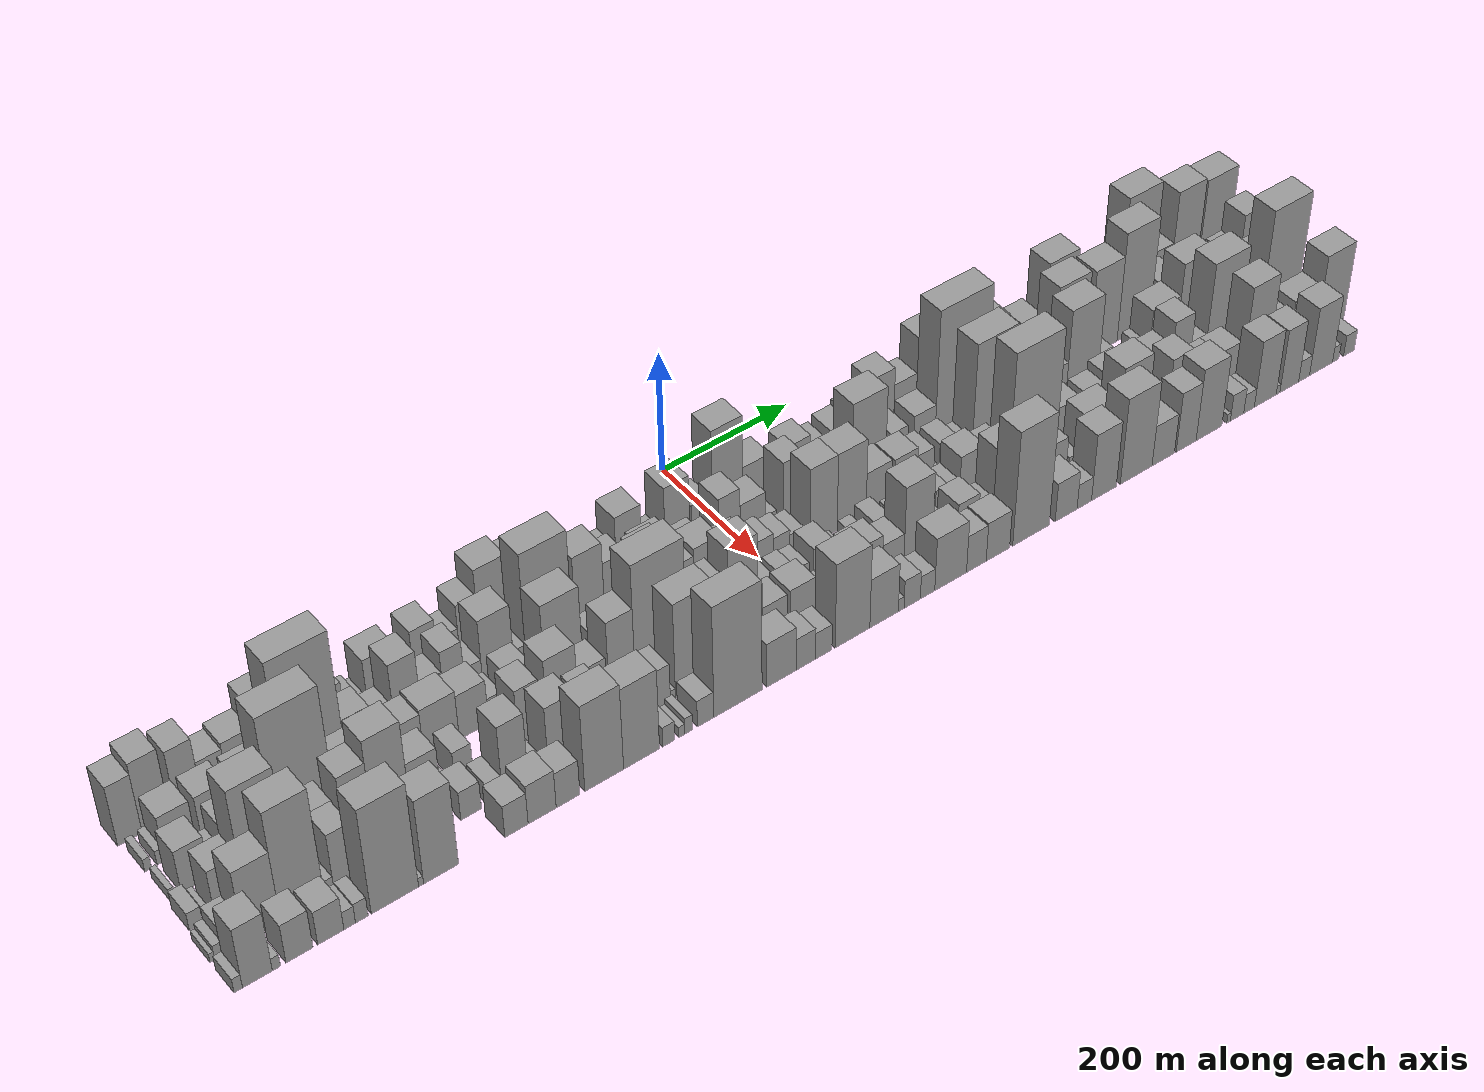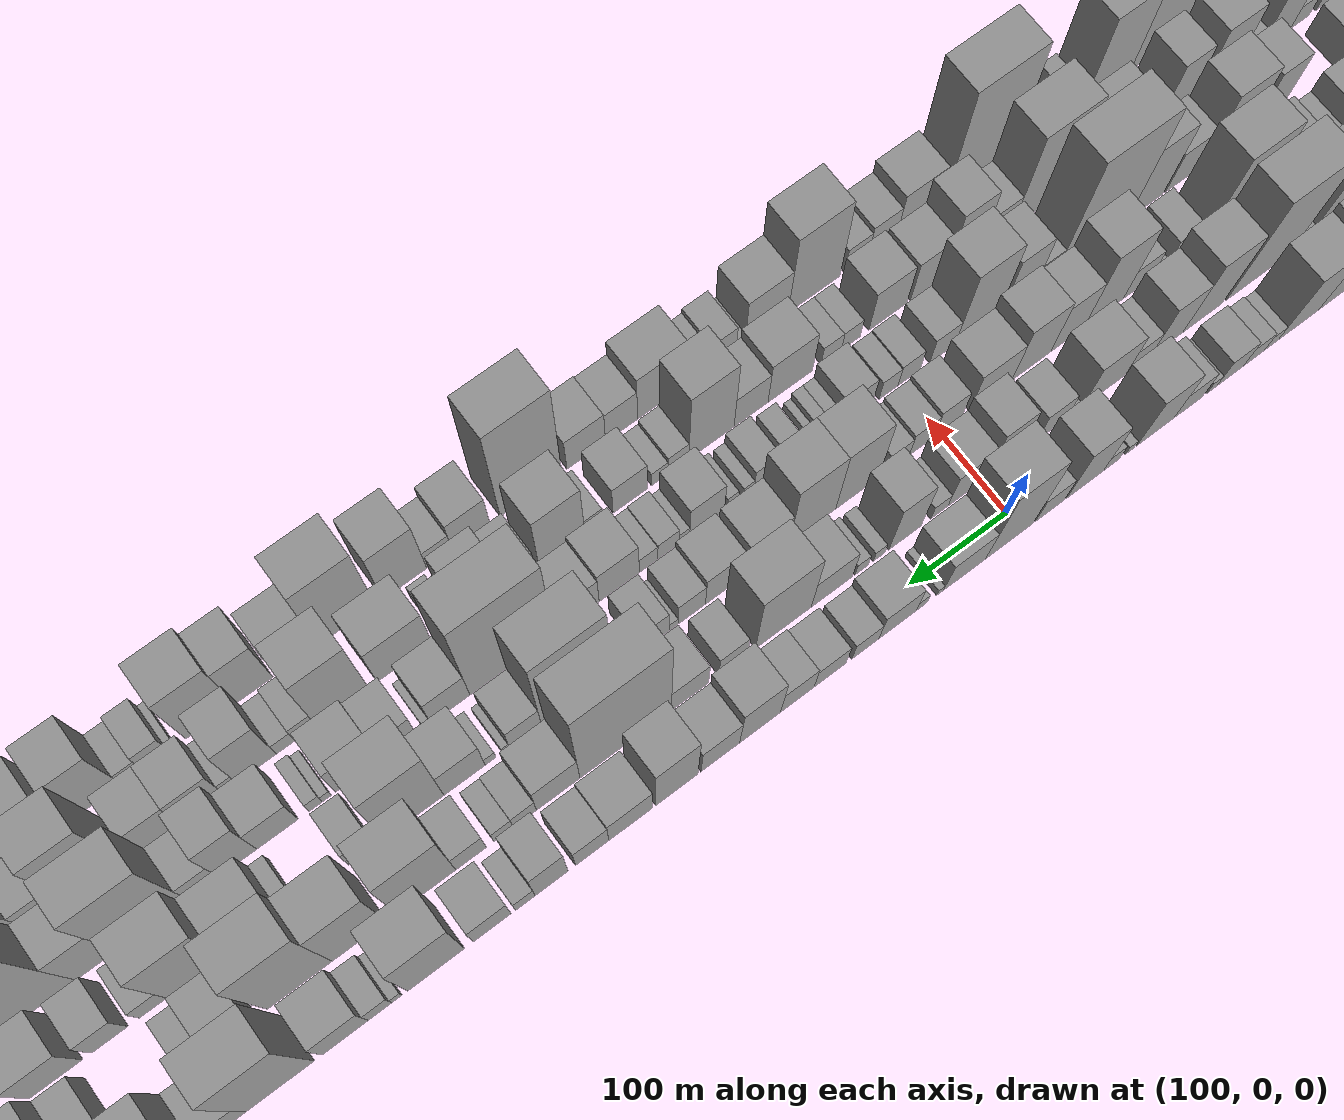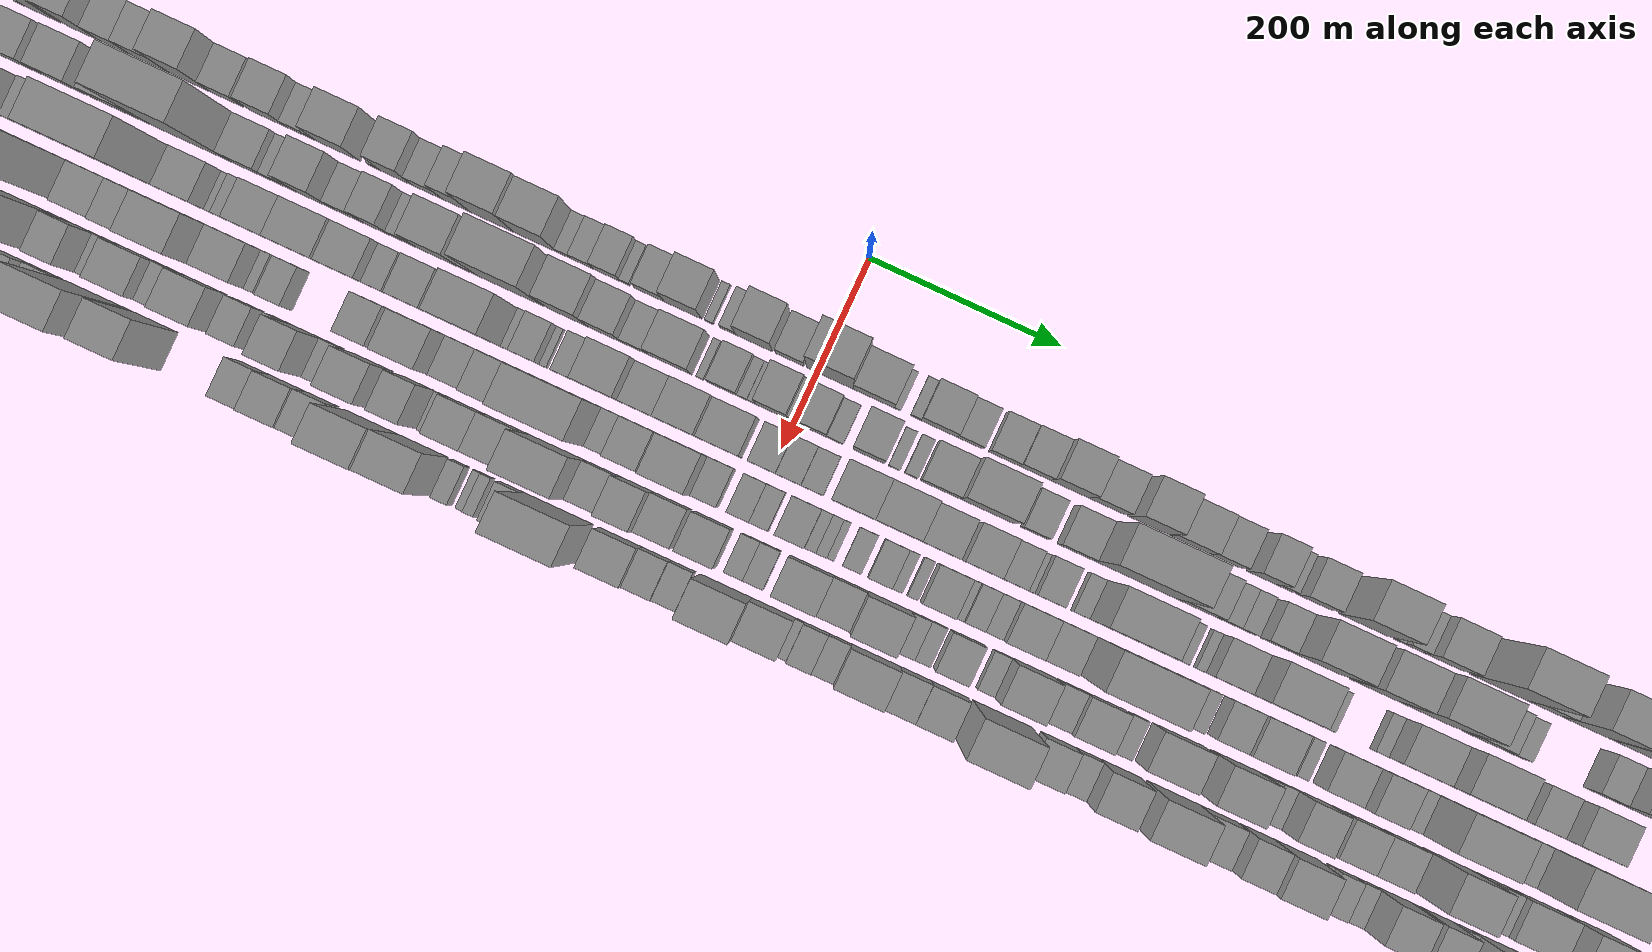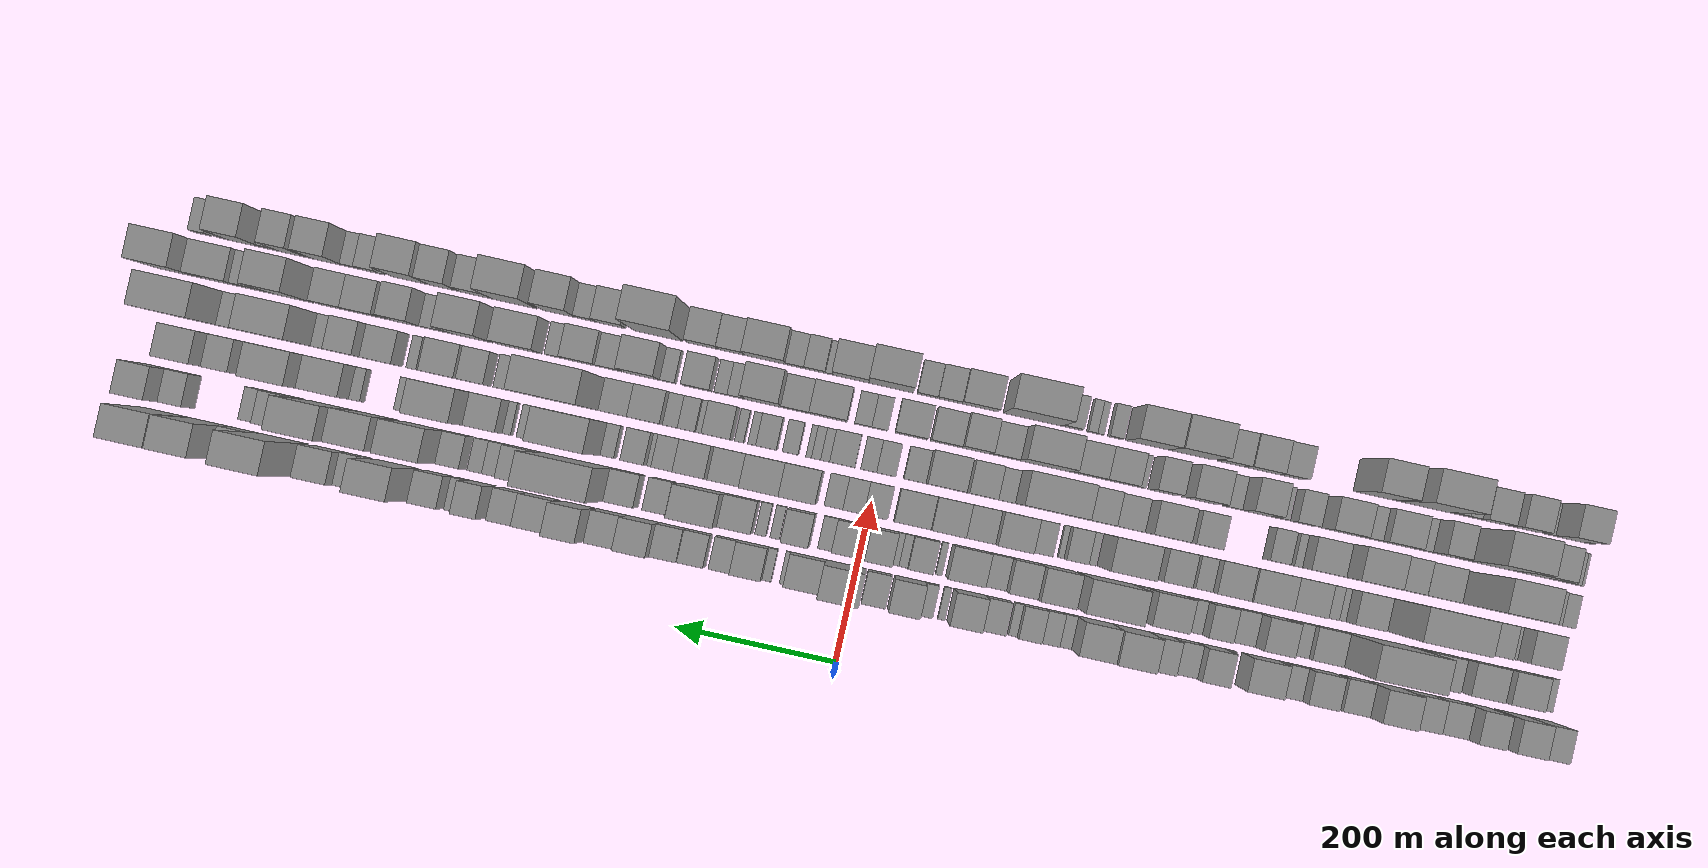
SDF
<sdf version="1.6">
 <world name="default">
  <scene>
   <sky><clouds><speed>12</speed></clouds></sky>
   <ambient>0.4 0.4 0.4 1</ambient>
   <background>0.7 0.7 0.7 1</background>
   <shadows>1</shadows>
  </scene>
  <gravity>0 0 -9.8066</gravity>
  <magnetic_field>6e-06 2.3e-05 -4.2e-05</magnetic_field>
  <physics default="0" name="default_physics" type="ode">
   <ode>
    <solver>
     <type>quick</type>
     <iters>10</iters>
     <sor>1.0</sor>
     <use_dynamic_moi_rescaling>0</use_dynamic_moi_rescaling>
    </solver>
    <constraints>
     <cfm>0</cfm>
     <erp>0.2</erp>
     <contact_max_correcting_vel>100</contact_max_correcting_vel>
     <contact_surface_layer>0.001</contact_surface_layer>
    </constraints>
   </ode>
   <max_step_size>0.004</max_step_size>
   <real_time_factor>1</real_time_factor>
   <real_time_update_rate>250</real_time_update_rate>
  </physics>
  <light name="sun" type="directional">
   <pose>0 0 10 0 0 0</pose>
   <diffuse>0.8 0.8 0.8 1</diffuse>
   <specular>0.2 0.2 0.2 1</specular>
   <attenuation>
    <range>1000</range>
    <constant>0.9</constant>
    <linear>0.01</linear>
    <quadratic>0.001</quadratic>
   </attenuation>
   <direction>-0.5 0.1 -0.9</direction>
  </light>
  <model name="building_1">
   <static>1</static>
   <pose>100.0000 -844.0381 0 0.000000 0.000000 0.000000</pose>
   <link name="link">
    <pose>0 0 51.00 0 0 0</pose>
    <collision name="collision"><geometry><box><size>40.0000 31.9238 102.0000</size></box></geometry></collision>
    <visual name="visual">
     <cast_shadows>0</cast_shadows>
     <geometry><box><size>40.0000 31.9238 102.0000</size></box></geometry>
     <material>
      <script>
       <uri>model://grey_wall/materials/scripts</uri>
       <uri>model://grey_wall/materials/textures</uri>
       <name>vrc/grey_wall</name>
      </script>
     </material>
    </visual>
   </link>
  </model>
  <model name="building_2">
   <static>1</static>
   <pose>100.0000 -809.5243 0 0.000000 0.000000 0.000000</pose>
   <link name="link">
    <pose>0 0 60.00 0 0 0</pose>
    <collision name="collision"><geometry><box><size>40.0000 37.1037 120.0000</size></box></geometry></collision>
    <visual name="visual">
     <cast_shadows>0</cast_shadows>
     <geometry><box><size>40.0000 37.1037 120.0000</size></box></geometry>
     <material>
      <script>
       <uri>model://grey_wall/materials/scripts</uri>
       <uri>model://grey_wall/materials/textures</uri>
       <name>vrc/grey_wall</name>
      </script>
     </material>
    </visual>
   </link>
  </model>
  <model name="building_3">
   <static>1</static>
   <pose>100.0000 -766.0664 0 0.000000 0.000000 0.000000</pose>
   <link name="link">
    <pose>0 0 54.00 0 0 0</pose>
    <collision name="collision"><geometry><box><size>40.0000 33.8120 108.0000</size></box></geometry></collision>
    <visual name="visual">
     <cast_shadows>0</cast_shadows>
     <geometry><box><size>40.0000 33.8120 108.0000</size></box></geometry>
     <material>
      <script>
       <uri>model://grey_wall/materials/scripts</uri>
       <uri>model://grey_wall/materials/textures</uri>
       <name>vrc/grey_wall</name>
      </script>
     </material>
    </visual>
   </link>
  </model>
  <model name="building_4">
   <static>1</static>
   <pose>100.0000 -732.0055 0 0.000000 0.000000 0.000000</pose>
   <link name="link">
    <pose>0 0 33.00 0 0 0</pose>
    <collision name="collision"><geometry><box><size>40.0000 34.3099 66.0000</size></box></geometry></collision>
    <visual name="visual">
     <cast_shadows>0</cast_shadows>
     <geometry><box><size>40.0000 34.3099 66.0000</size></box></geometry>
     <material>
      <script>
       <uri>model://grey_wall/materials/scripts</uri>
       <uri>model://grey_wall/materials/textures</uri>
       <name>vrc/grey_wall</name>
      </script>
     </material>
    </visual>
   </link>
  </model>
  <model name="building_5">
   <static>1</static>
   <pose>100.0000 -695.1913 0 0.000000 0.000000 0.000000</pose>
   <link name="link">
    <pose>0 0 37.50 0 0 0</pose>
    <collision name="collision"><geometry><box><size>40.0000 39.3186 75.0000</size></box></geometry></collision>
    <visual name="visual">
     <cast_shadows>0</cast_shadows>
     <geometry><box><size>40.0000 39.3186 75.0000</size></box></geometry>
     <material>
      <script>
       <uri>model://grey_wall/materials/scripts</uri>
       <uri>model://grey_wall/materials/textures</uri>
       <name>vrc/grey_wall</name>
      </script>
     </material>
    </visual>
   </link>
  </model>
  <model name="building_6">
   <static>1</static>
   <pose>100.0000 -653.9232 0 0.000000 0.000000 0.000000</pose>
   <link name="link">
    <pose>0 0 58.50 0 0 0</pose>
    <collision name="collision"><geometry><box><size>40.0000 43.2176 117.0000</size></box></geometry></collision>
    <visual name="visual">
     <cast_shadows>0</cast_shadows>
     <geometry><box><size>40.0000 43.2176 117.0000</size></box></geometry>
     <material>
      <script>
       <uri>model://grey_wall/materials/scripts</uri>
       <uri>model://grey_wall/materials/textures</uri>
       <name>vrc/grey_wall</name>
      </script>
     </material>
    </visual>
   </link>
  </model>
  <model name="building_7">
   <static>1</static>
   <pose>100.0000 -615.7278 0 0.000000 0.000000 0.000000</pose>
   <link name="link">
    <pose>0 0 28.50 0 0 0</pose>
    <collision name="collision"><geometry><box><size>40.0000 33.1732 57.0000</size></box></geometry></collision>
    <visual name="visual">
     <cast_shadows>0</cast_shadows>
     <geometry><box><size>40.0000 33.1732 57.0000</size></box></geometry>
     <material>
      <script>
       <uri>model://grey_wall/materials/scripts</uri>
       <uri>model://grey_wall/materials/textures</uri>
       <name>vrc/grey_wall</name>
      </script>
     </material>
    </visual>
   </link>
  </model>
  <model name="building_8">
   <static>1</static>
   <pose>100.0000 -573.2025 0 0.000000 0.000000 0.000000</pose>
   <link name="link">
    <pose>0 0 36.00 0 0 0</pose>
    <collision name="collision"><geometry><box><size>40.0000 37.8773 72.0000</size></box></geometry></collision>
    <visual name="visual">
     <cast_shadows>0</cast_shadows>
     <geometry><box><size>40.0000 37.8773 72.0000</size></box></geometry>
     <material>
      <script>
       <uri>model://grey_wall/materials/scripts</uri>
       <uri>model://grey_wall/materials/textures</uri>
       <name>vrc/grey_wall</name>
      </script>
     </material>
    </visual>
   </link>
  </model>
  <model name="building_9">
   <static>1</static>
   <pose>100.0000 -543.5128 0 0.000000 0.000000 0.000000</pose>
   <link name="link">
    <pose>0 0 18.00 0 0 0</pose>
    <collision name="collision"><geometry><box><size>40.0000 21.5021 36.0000</size></box></geometry></collision>
    <visual name="visual">
     <cast_shadows>0</cast_shadows>
     <geometry><box><size>40.0000 21.5021 36.0000</size></box></geometry>
     <material>
      <script>
       <uri>model://grey_wall/materials/scripts</uri>
       <uri>model://grey_wall/materials/textures</uri>
       <name>vrc/grey_wall</name>
      </script>
     </material>
    </visual>
   </link>
  </model>
  <model name="building_10">
   <static>1</static>
   <pose>100.0000 -527.5985 0 0.000000 0.000000 0.000000</pose>
   <link name="link">
    <pose>0 0 12.00 0 0 0</pose>
    <collision name="collision"><geometry><box><size>40.0000 10.3264 24.0000</size></box></geometry></collision>
    <visual name="visual">
     <cast_shadows>0</cast_shadows>
     <geometry><box><size>40.0000 10.3264 24.0000</size></box></geometry>
     <material>
      <script>
       <uri>model://grey_wall/materials/scripts</uri>
       <uri>model://grey_wall/materials/textures</uri>
       <name>vrc/grey_wall</name>
      </script>
     </material>
    </visual>
   </link>
  </model>
  <model name="building_11">
   <static>1</static>
   <pose>100.0000 -499.9717 0 0.000000 0.000000 0.000000</pose>
   <link name="link">
    <pose>0 0 43.50 0 0 0</pose>
    <collision name="collision"><geometry><box><size>40.0000 44.9273 87.0000</size></box></geometry></collision>
    <visual name="visual">
     <cast_shadows>0</cast_shadows>
     <geometry><box><size>40.0000 44.9273 87.0000</size></box></geometry>
     <material>
      <script>
       <uri>model://grey_wall/materials/scripts</uri>
       <uri>model://grey_wall/materials/textures</uri>
       <name>vrc/grey_wall</name>
      </script>
     </material>
    </visual>
   </link>
  </model>
  <model name="building_12">
   <static>1</static>
   <pose>100.0000 -462.0236 0 0.000000 0.000000 0.000000</pose>
   <link name="link">
    <pose>0 0 12.00 0 0 0</pose>
    <collision name="collision"><geometry><box><size>40.0000 10.9687 24.0000</size></box></geometry></collision>
    <visual name="visual">
     <cast_shadows>0</cast_shadows>
     <geometry><box><size>40.0000 10.9687 24.0000</size></box></geometry>
     <material>
      <script>
       <uri>model://grey_wall/materials/scripts</uri>
       <uri>model://grey_wall/materials/textures</uri>
       <name>vrc/grey_wall</name>
      </script>
     </material>
    </visual>
   </link>
  </model>
  <model name="building_13">
   <static>1</static>
   <pose>100.0000 -439.4131 0 0.000000 0.000000 0.000000</pose>
   <link name="link">
    <pose>0 0 46.50 0 0 0</pose>
    <collision name="collision"><geometry><box><size>40.0000 34.2523 93.0000</size></box></geometry></collision>
    <visual name="visual">
     <cast_shadows>0</cast_shadows>
     <geometry><box><size>40.0000 34.2523 93.0000</size></box></geometry>
     <material>
      <script>
       <uri>model://grey_wall/materials/scripts</uri>
       <uri>model://grey_wall/materials/textures</uri>
       <name>vrc/grey_wall</name>
      </script>
     </material>
    </visual>
   </link>
  </model>
  <model name="building_14">
   <static>1</static>
   <pose>100.0000 -406.8225 0 0.000000 0.000000 0.000000</pose>
   <link name="link">
    <pose>0 0 28.50 0 0 0</pose>
    <collision name="collision"><geometry><box><size>40.0000 30.9290 57.0000</size></box></geometry></collision>
    <visual name="visual">
     <cast_shadows>0</cast_shadows>
     <geometry><box><size>40.0000 30.9290 57.0000</size></box></geometry>
     <material>
      <script>
       <uri>model://grey_wall/materials/scripts</uri>
       <uri>model://grey_wall/materials/textures</uri>
       <name>vrc/grey_wall</name>
      </script>
     </material>
    </visual>
   </link>
  </model>
  <model name="building_15">
   <static>1</static>
   <pose>100.0000 -376.9256 0 0.000000 0.000000 0.000000</pose>
   <link name="link">
    <pose>0 0 48.00 0 0 0</pose>
    <collision name="collision"><geometry><box><size>40.0000 28.8647 96.0000</size></box></geometry></collision>
    <visual name="visual">
     <cast_shadows>0</cast_shadows>
     <geometry><box><size>40.0000 28.8647 96.0000</size></box></geometry>
     <material>
      <script>
       <uri>model://grey_wall/materials/scripts</uri>
       <uri>model://grey_wall/materials/textures</uri>
       <name>vrc/grey_wall</name>
      </script>
     </material>
    </visual>
   </link>
  </model>
  <model name="building_16">
   <static>1</static>
   <pose>100.0000 -339.4239 0 0.000000 0.000000 0.000000</pose>
   <link name="link">
    <pose>0 0 69.00 0 0 0</pose>
    <collision name="collision"><geometry><box><size>40.0000 46.1388 138.0000</size></box></geometry></collision>
    <visual name="visual">
     <cast_shadows>0</cast_shadows>
     <geometry><box><size>40.0000 46.1388 138.0000</size></box></geometry>
     <material>
      <script>
       <uri>model://grey_wall/materials/scripts</uri>
       <uri>model://grey_wall/materials/textures</uri>
       <name>vrc/grey_wall</name>
      </script>
     </material>
    </visual>
   </link>
  </model>
  <model name="building_17">
   <static>1</static>
   <pose>100.0000 -294.0704 0 0.000000 0.000000 0.000000</pose>
   <link name="link">
    <pose>0 0 61.50 0 0 0</pose>
    <collision name="collision"><geometry><box><size>40.0000 44.5682 123.0000</size></box></geometry></collision>
    <visual name="visual">
     <cast_shadows>0</cast_shadows>
     <geometry><box><size>40.0000 44.5682 123.0000</size></box></geometry>
     <material>
      <script>
       <uri>model://grey_wall/materials/scripts</uri>
       <uri>model://grey_wall/materials/textures</uri>
       <name>vrc/grey_wall</name>
      </script>
     </material>
    </visual>
   </link>
  </model>
  <model name="building_18">
   <static>1</static>
   <pose>100.0000 -264.2371 0 0.000000 0.000000 0.000000</pose>
   <link name="link">
    <pose>0 0 15.00 0 0 0</pose>
    <collision name="collision"><geometry><box><size>40.0000 15.0983 30.0000</size></box></geometry></collision>
    <visual name="visual">
     <cast_shadows>0</cast_shadows>
     <geometry><box><size>40.0000 15.0983 30.0000</size></box></geometry>
     <material>
      <script>
       <uri>model://grey_wall/materials/scripts</uri>
       <uri>model://grey_wall/materials/textures</uri>
       <name>vrc/grey_wall</name>
      </script>
     </material>
    </visual>
   </link>
  </model>
  <model name="building_19">
   <static>1</static>
   <pose>100.0000 -245.3737 0 0.000000 0.000000 0.000000</pose>
   <link name="link">
    <pose>0 0 19.50 0 0 0</pose>
    <collision name="collision"><geometry><box><size>40.0000 22.6286 39.0000</size></box></geometry></collision>
    <visual name="visual">
     <cast_shadows>0</cast_shadows>
     <geometry><box><size>40.0000 22.6286 39.0000</size></box></geometry>
     <material>
      <script>
       <uri>model://grey_wall/materials/scripts</uri>
       <uri>model://grey_wall/materials/textures</uri>
       <name>vrc/grey_wall</name>
      </script>
     </material>
    </visual>
   </link>
  </model>
  <model name="building_20">
   <static>1</static>
   <pose>100.0000 -219.8085 0 0.000000 0.000000 0.000000</pose>
   <link name="link">
    <pose>0 0 27.00 0 0 0</pose>
    <collision name="collision"><geometry><box><size>40.0000 28.5018 54.0000</size></box></geometry></collision>
    <visual name="visual">
     <cast_shadows>0</cast_shadows>
     <geometry><box><size>40.0000 28.5018 54.0000</size></box></geometry>
     <material>
      <script>
       <uri>model://grey_wall/materials/scripts</uri>
       <uri>model://grey_wall/materials/textures</uri>
       <name>vrc/grey_wall</name>
      </script>
     </material>
    </visual>
   </link>
  </model>
  <model name="building_21">
   <static>1</static>
   <pose>100.0000 -200.2709 0 0.000000 0.000000 0.000000</pose>
   <link name="link">
    <pose>0 0 12.00 0 0 0</pose>
    <collision name="collision"><geometry><box><size>40.0000 10.5735 24.0000</size></box></geometry></collision>
    <visual name="visual">
     <cast_shadows>0</cast_shadows>
     <geometry><box><size>40.0000 10.5735 24.0000</size></box></geometry>
     <material>
      <script>
       <uri>model://grey_wall/materials/scripts</uri>
       <uri>model://grey_wall/materials/textures</uri>
       <name>vrc/grey_wall</name>
      </script>
     </material>
    </visual>
   </link>
  </model>
  <model name="building_22">
   <static>1</static>
   <pose>100.0000 -174.5766 0 0.000000 0.000000 0.000000</pose>
   <link name="link">
    <pose>0 0 27.00 0 0 0</pose>
    <collision name="collision"><geometry><box><size>40.0000 30.8150 54.0000</size></box></geometry></collision>
    <visual name="visual">
     <cast_shadows>0</cast_shadows>
     <geometry><box><size>40.0000 30.8150 54.0000</size></box></geometry>
     <material>
      <script>
       <uri>model://grey_wall/materials/scripts</uri>
       <uri>model://grey_wall/materials/textures</uri>
       <name>vrc/grey_wall</name>
      </script>
     </material>
    </visual>
   </link>
  </model>
  <model name="building_23">
   <static>1</static>
   <pose>100.0000 -139.5896 0 0.000000 0.000000 0.000000</pose>
   <link name="link">
    <pose>0 0 51.00 0 0 0</pose>
    <collision name="collision"><geometry><box><size>40.0000 39.1590 102.0000</size></box></geometry></collision>
    <visual name="visual">
     <cast_shadows>0</cast_shadows>
     <geometry><box><size>40.0000 39.1590 102.0000</size></box></geometry>
     <material>
      <script>
       <uri>model://grey_wall/materials/scripts</uri>
       <uri>model://grey_wall/materials/textures</uri>
       <name>vrc/grey_wall</name>
      </script>
     </material>
    </visual>
   </link>
  </model>
  <model name="building_24">
   <static>1</static>
   <pose>100.0000 -112.6292 0 0.000000 0.000000 0.000000</pose>
   <link name="link">
    <pose>0 0 9.00 0 0 0</pose>
    <collision name="collision"><geometry><box><size>40.0000 8.7618 18.0000</size></box></geometry></collision>
    <visual name="visual">
     <cast_shadows>0</cast_shadows>
     <geometry><box><size>40.0000 8.7618 18.0000</size></box></geometry>
     <material>
      <script>
       <uri>model://grey_wall/materials/scripts</uri>
       <uri>model://grey_wall/materials/textures</uri>
       <name>vrc/grey_wall</name>
      </script>
     </material>
    </visual>
   </link>
  </model>
  <model name="building_25">
   <static>1</static>
   <pose>100.0000 -92.9114 0 0.000000 0.000000 0.000000</pose>
   <link name="link">
    <pose>0 0 16.50 0 0 0</pose>
    <collision name="collision"><geometry><box><size>40.0000 16.6737 33.0000</size></box></geometry></collision>
    <visual name="visual">
     <cast_shadows>0</cast_shadows>
     <geometry><box><size>40.0000 16.6737 33.0000</size></box></geometry>
     <material>
      <script>
       <uri>model://grey_wall/materials/scripts</uri>
       <uri>model://grey_wall/materials/textures</uri>
       <name>vrc/grey_wall</name>
      </script>
     </material>
    </visual>
   </link>
  </model>
  <model name="building_26">
   <static>1</static>
   <pose>100.0000 -65.4804 0 0.000000 0.000000 0.000000</pose>
   <link name="link">
    <pose>0 0 54.00 0 0 0</pose>
    <collision name="collision"><geometry><box><size>40.0000 38.1882 108.0000</size></box></geometry></collision>
    <visual name="visual">
     <cast_shadows>0</cast_shadows>
     <geometry><box><size>40.0000 38.1882 108.0000</size></box></geometry>
     <material>
      <script>
       <uri>model://grey_wall/materials/scripts</uri>
       <uri>model://grey_wall/materials/textures</uri>
       <name>vrc/grey_wall</name>
      </script>
     </material>
    </visual>
   </link>
  </model>
  <model name="building_27">
   <static>1</static>
   <pose>100.0000 -28.5838 0 0.000000 0.000000 0.000000</pose>
   <link name="link">
    <pose>0 0 27.00 0 0 0</pose>
    <collision name="collision"><geometry><box><size>40.0000 29.6051 54.0000</size></box></geometry></collision>
    <visual name="visual">
     <cast_shadows>0</cast_shadows>
     <geometry><box><size>40.0000 29.6051 54.0000</size></box></geometry>
     <material>
      <script>
       <uri>model://grey_wall/materials/scripts</uri>
       <uri>model://grey_wall/materials/textures</uri>
       <name>vrc/grey_wall</name>
      </script>
     </material>
    </visual>
   </link>
  </model>
  <model name="building_28">
   <static>1</static>
   <pose>100.0000 13.5725 0 0.000000 0.000000 0.000000</pose>
   <link name="link">
    <pose>0 0 81.00 0 0 0</pose>
    <collision name="collision"><geometry><box><size>40.0000 48.7074 162.0000</size></box></geometry></collision>
    <visual name="visual">
     <cast_shadows>0</cast_shadows>
     <geometry><box><size>40.0000 48.7074 162.0000</size></box></geometry>
     <material>
      <script>
       <uri>model://grey_wall/materials/scripts</uri>
       <uri>model://grey_wall/materials/textures</uri>
       <name>vrc/grey_wall</name>
      </script>
     </material>
    </visual>
   </link>
  </model>
  <model name="building_29">
   <static>1</static>
   <pose>100.0000 59.4433 0 0.000000 0.000000 0.000000</pose>
   <link name="link">
    <pose>0 0 36.00 0 0 0</pose>
    <collision name="collision"><geometry><box><size>40.0000 43.0343 72.0000</size></box></geometry></collision>
    <visual name="visual">
     <cast_shadows>0</cast_shadows>
     <geometry><box><size>40.0000 43.0343 72.0000</size></box></geometry>
     <material>
      <script>
       <uri>model://grey_wall/materials/scripts</uri>
       <uri>model://grey_wall/materials/textures</uri>
       <name>vrc/grey_wall</name>
      </script>
     </material>
    </visual>
   </link>
  </model>
  <model name="building_30">
   <static>1</static>
   <pose>100.0000 84.2464 0 0.000000 0.000000 0.000000</pose>
   <link name="link">
    <pose>0 0 7.50 0 0 0</pose>
    <collision name="collision"><geometry><box><size>40.0000 6.5718 15.0000</size></box></geometry></collision>
    <visual name="visual">
     <cast_shadows>0</cast_shadows>
     <geometry><box><size>40.0000 6.5718 15.0000</size></box></geometry>
     <material>
      <script>
       <uri>model://grey_wall/materials/scripts</uri>
       <uri>model://grey_wall/materials/textures</uri>
       <name>vrc/grey_wall</name>
      </script>
     </material>
    </visual>
   </link>
  </model>
  <model name="building_31">
   <static>1</static>
   <pose>100.0000 103.0803 0 0.000000 0.000000 0.000000</pose>
   <link name="link">
    <pose>0 0 12.00 0 0 0</pose>
    <collision name="collision"><geometry><box><size>40.0000 11.0961 24.0000</size></box></geometry></collision>
    <visual name="visual">
     <cast_shadows>0</cast_shadows>
     <geometry><box><size>40.0000 11.0961 24.0000</size></box></geometry>
     <material>
      <script>
       <uri>model://grey_wall/materials/scripts</uri>
       <uri>model://grey_wall/materials/textures</uri>
       <name>vrc/grey_wall</name>
      </script>
     </material>
    </visual>
   </link>
  </model>
  <model name="building_32">
   <static>1</static>
   <pose>100.0000 127.5367 0 0.000000 0.000000 0.000000</pose>
   <link name="link">
    <pose>0 0 33.00 0 0 0</pose>
    <collision name="collision"><geometry><box><size>40.0000 37.8167 66.0000</size></box></geometry></collision>
    <visual name="visual">
     <cast_shadows>0</cast_shadows>
     <geometry><box><size>40.0000 37.8167 66.0000</size></box></geometry>
     <material>
      <script>
       <uri>model://grey_wall/materials/scripts</uri>
       <uri>model://grey_wall/materials/textures</uri>
       <name>vrc/grey_wall</name>
      </script>
     </material>
    </visual>
   </link>
  </model>
  <model name="building_33">
   <static>1</static>
   <pose>100.0000 159.8095 0 0.000000 0.000000 0.000000</pose>
   <link name="link">
    <pose>0 0 22.50 0 0 0</pose>
    <collision name="collision"><geometry><box><size>40.0000 26.7289 45.0000</size></box></geometry></collision>
    <visual name="visual">
     <cast_shadows>0</cast_shadows>
     <geometry><box><size>40.0000 26.7289 45.0000</size></box></geometry>
     <material>
      <script>
       <uri>model://grey_wall/materials/scripts</uri>
       <uri>model://grey_wall/materials/textures</uri>
       <name>vrc/grey_wall</name>
      </script>
     </material>
    </visual>
   </link>
  </model>
  <model name="building_34">
   <static>1</static>
   <pose>100.0000 195.0250 0 0.000000 0.000000 0.000000</pose>
   <link name="link">
    <pose>0 0 27.00 0 0 0</pose>
    <collision name="collision"><geometry><box><size>40.0000 31.7022 54.0000</size></box></geometry></collision>
    <visual name="visual">
     <cast_shadows>0</cast_shadows>
     <geometry><box><size>40.0000 31.7022 54.0000</size></box></geometry>
     <material>
      <script>
       <uri>model://grey_wall/materials/scripts</uri>
       <uri>model://grey_wall/materials/textures</uri>
       <name>vrc/grey_wall</name>
      </script>
     </material>
    </visual>
   </link>
  </model>
  <model name="building_35">
   <static>1</static>
   <pose>100.0000 227.4179 0 0.000000 0.000000 0.000000</pose>
   <link name="link">
    <pose>0 0 31.50 0 0 0</pose>
    <collision name="collision"><geometry><box><size>40.0000 33.0837 63.0000</size></box></geometry></collision>
    <visual name="visual">
     <cast_shadows>0</cast_shadows>
     <geometry><box><size>40.0000 33.0837 63.0000</size></box></geometry>
     <material>
      <script>
       <uri>model://grey_wall/materials/scripts</uri>
       <uri>model://grey_wall/materials/textures</uri>
       <name>vrc/grey_wall</name>
      </script>
     </material>
    </visual>
   </link>
  </model>
  <model name="building_36">
   <static>1</static>
   <pose>100.0000 263.9914 0 0.000000 0.000000 0.000000</pose>
   <link name="link">
    <pose>0 0 52.50 0 0 0</pose>
    <collision name="collision"><geometry><box><size>40.0000 40.0632 105.0000</size></box></geometry></collision>
    <visual name="visual">
     <cast_shadows>0</cast_shadows>
     <geometry><box><size>40.0000 40.0632 105.0000</size></box></geometry>
     <material>
      <script>
       <uri>model://grey_wall/materials/scripts</uri>
       <uri>model://grey_wall/materials/textures</uri>
       <name>vrc/grey_wall</name>
      </script>
     </material>
    </visual>
   </link>
  </model>
  <model name="building_37">
   <static>1</static>
   <pose>100.0000 302.7851 0 0.000000 0.000000 0.000000</pose>
   <link name="link">
    <pose>0 0 37.50 0 0 0</pose>
    <collision name="collision"><geometry><box><size>40.0000 37.5243 75.0000</size></box></geometry></collision>
    <visual name="visual">
     <cast_shadows>0</cast_shadows>
     <geometry><box><size>40.0000 37.5243 75.0000</size></box></geometry>
     <material>
      <script>
       <uri>model://grey_wall/materials/scripts</uri>
       <uri>model://grey_wall/materials/textures</uri>
       <name>vrc/grey_wall</name>
      </script>
     </material>
    </visual>
   </link>
  </model>
  <model name="building_38">
   <static>1</static>
   <pose>100.0000 344.7998 0 0.000000 0.000000 0.000000</pose>
   <link name="link">
    <pose>0 0 66.00 0 0 0</pose>
    <collision name="collision"><geometry><box><size>40.0000 40.5052 132.0000</size></box></geometry></collision>
    <visual name="visual">
     <cast_shadows>0</cast_shadows>
     <geometry><box><size>40.0000 40.5052 132.0000</size></box></geometry>
     <material>
      <script>
       <uri>model://grey_wall/materials/scripts</uri>
       <uri>model://grey_wall/materials/textures</uri>
       <name>vrc/grey_wall</name>
      </script>
     </material>
    </visual>
   </link>
  </model>
  <model name="building_39">
   <static>1</static>
   <pose>100.0000 388.9732 0 0.000000 0.000000 0.000000</pose>
   <link name="link">
    <pose>0 0 36.00 0 0 0</pose>
    <collision name="collision"><geometry><box><size>40.0000 41.8415 72.0000</size></box></geometry></collision>
    <visual name="visual">
     <cast_shadows>0</cast_shadows>
     <geometry><box><size>40.0000 41.8415 72.0000</size></box></geometry>
     <material>
      <script>
       <uri>model://grey_wall/materials/scripts</uri>
       <uri>model://grey_wall/materials/textures</uri>
       <name>vrc/grey_wall</name>
      </script>
     </material>
    </visual>
   </link>
  </model>
  <model name="building_40">
   <static>1</static>
   <pose>100.0000 425.6944 0 0.000000 0.000000 0.000000</pose>
   <link name="link">
    <pose>0 0 31.50 0 0 0</pose>
    <collision name="collision"><geometry><box><size>40.0000 31.6009 63.0000</size></box></geometry></collision>
    <visual name="visual">
     <cast_shadows>0</cast_shadows>
     <geometry><box><size>40.0000 31.6009 63.0000</size></box></geometry>
     <material>
      <script>
       <uri>model://grey_wall/materials/scripts</uri>
       <uri>model://grey_wall/materials/textures</uri>
       <name>vrc/grey_wall</name>
      </script>
     </material>
    </visual>
   </link>
  </model>
  <model name="building_41">
   <static>1</static>
   <pose>100.0000 463.9715 0 0.000000 0.000000 0.000000</pose>
   <link name="link">
    <pose>0 0 46.50 0 0 0</pose>
    <collision name="collision"><geometry><box><size>40.0000 30.9533 93.0000</size></box></geometry></collision>
    <visual name="visual">
     <cast_shadows>0</cast_shadows>
     <geometry><box><size>40.0000 30.9533 93.0000</size></box></geometry>
     <material>
      <script>
       <uri>model://grey_wall/materials/scripts</uri>
       <uri>model://grey_wall/materials/textures</uri>
       <name>vrc/grey_wall</name>
      </script>
     </material>
    </visual>
   </link>
  </model>
  <model name="building_42">
   <static>1</static>
   <pose>100.0000 488.6046 0 0.000000 0.000000 0.000000</pose>
   <link name="link">
    <pose>0 0 18.00 0 0 0</pose>
    <collision name="collision"><geometry><box><size>40.0000 18.3129 36.0000</size></box></geometry></collision>
    <visual name="visual">
     <cast_shadows>0</cast_shadows>
     <geometry><box><size>40.0000 18.3129 36.0000</size></box></geometry>
     <material>
      <script>
       <uri>model://grey_wall/materials/scripts</uri>
       <uri>model://grey_wall/materials/textures</uri>
       <name>vrc/grey_wall</name>
      </script>
     </material>
    </visual>
   </link>
  </model>
  <model name="building_43">
   <static>1</static>
   <pose>100.0000 519.3951 0 0.000000 0.000000 0.000000</pose>
   <link name="link">
    <pose>0 0 31.50 0 0 0</pose>
    <collision name="collision"><geometry><box><size>40.0000 35.2682 63.0000</size></box></geometry></collision>
    <visual name="visual">
     <cast_shadows>0</cast_shadows>
     <geometry><box><size>40.0000 35.2682 63.0000</size></box></geometry>
     <material>
      <script>
       <uri>model://grey_wall/materials/scripts</uri>
       <uri>model://grey_wall/materials/textures</uri>
       <name>vrc/grey_wall</name>
      </script>
     </material>
    </visual>
   </link>
  </model>
  <model name="building_44">
   <static>1</static>
   <pose>100.0000 571.2320 0 0.000000 0.000000 0.000000</pose>
   <link name="link">
    <pose>0 0 72.00 0 0 0</pose>
    <collision name="collision"><geometry><box><size>40.0000 52.4056 144.0000</size></box></geometry></collision>
    <visual name="visual">
     <cast_shadows>0</cast_shadows>
     <geometry><box><size>40.0000 52.4056 144.0000</size></box></geometry>
     <material>
      <script>
       <uri>model://grey_wall/materials/scripts</uri>
       <uri>model://grey_wall/materials/textures</uri>
       <name>vrc/grey_wall</name>
      </script>
     </material>
    </visual>
   </link>
  </model>
  <model name="building_45">
   <static>1</static>
   <pose>100.0000 607.0281 0 0.000000 0.000000 0.000000</pose>
   <link name="link">
    <pose>0 0 10.50 0 0 0</pose>
    <collision name="collision"><geometry><box><size>40.0000 9.1866 21.0000</size></box></geometry></collision>
    <visual name="visual">
     <cast_shadows>0</cast_shadows>
     <geometry><box><size>40.0000 9.1866 21.0000</size></box></geometry>
     <material>
      <script>
       <uri>model://grey_wall/materials/scripts</uri>
       <uri>model://grey_wall/materials/textures</uri>
       <name>vrc/grey_wall</name>
      </script>
     </material>
    </visual>
   </link>
  </model>
  <model name="building_46">
   <static>1</static>
   <pose>100.0000 622.2681 0 0.000000 0.000000 0.000000</pose>
   <link name="link">
    <pose>0 0 21.00 0 0 0</pose>
    <collision name="collision"><geometry><box><size>40.0000 21.2934 42.0000</size></box></geometry></collision>
    <visual name="visual">
     <cast_shadows>0</cast_shadows>
     <geometry><box><size>40.0000 21.2934 42.0000</size></box></geometry>
     <material>
      <script>
       <uri>model://grey_wall/materials/scripts</uri>
       <uri>model://grey_wall/materials/textures</uri>
       <name>vrc/grey_wall</name>
      </script>
     </material>
    </visual>
   </link>
  </model>
  <model name="building_47">
   <static>1</static>
   <pose>100.0000 653.8330 0 0.000000 0.000000 0.000000</pose>
   <link name="link">
    <pose>0 0 37.50 0 0 0</pose>
    <collision name="collision"><geometry><box><size>40.0000 41.8363 75.0000</size></box></geometry></collision>
    <visual name="visual">
     <cast_shadows>0</cast_shadows>
     <geometry><box><size>40.0000 41.8363 75.0000</size></box></geometry>
     <material>
      <script>
       <uri>model://grey_wall/materials/scripts</uri>
       <uri>model://grey_wall/materials/textures</uri>
       <name>vrc/grey_wall</name>
      </script>
     </material>
    </visual>
   </link>
  </model>
  <model name="building_48">
   <static>1</static>
   <pose>100.0000 711.7514 0 0.000000 0.000000 0.000000</pose>
   <link name="link">
    <pose>0 0 93.00 0 0 0</pose>
    <collision name="collision"><geometry><box><size>40.0000 60.0006 186.0000</size></box></geometry></collision>
    <visual name="visual">
     <cast_shadows>0</cast_shadows>
     <geometry><box><size>40.0000 60.0006 186.0000</size></box></geometry>
     <material>
      <script>
       <uri>model://grey_wall/materials/scripts</uri>
       <uri>model://grey_wall/materials/textures</uri>
       <name>vrc/grey_wall</name>
      </script>
     </material>
    </visual>
   </link>
  </model>
  <model name="building_49">
   <static>1</static>
   <pose>100.0000 758.8927 0 0.000000 0.000000 0.000000</pose>
   <link name="link">
    <pose>0 0 31.50 0 0 0</pose>
    <collision name="collision"><geometry><box><size>40.0000 34.2820 63.0000</size></box></geometry></collision>
    <visual name="visual">
     <cast_shadows>0</cast_shadows>
     <geometry><box><size>40.0000 34.2820 63.0000</size></box></geometry>
     <material>
      <script>
       <uri>model://grey_wall/materials/scripts</uri>
       <uri>model://grey_wall/materials/textures</uri>
       <name>vrc/grey_wall</name>
      </script>
     </material>
    </visual>
   </link>
  </model>
  <model name="building_50">
   <static>1</static>
   <pose>100.0000 801.2108 0 0.000000 0.000000 0.000000</pose>
   <link name="link">
    <pose>0 0 75.00 0 0 0</pose>
    <collision name="collision"><geometry><box><size>40.0000 50.3542 150.0000</size></box></geometry></collision>
    <visual name="visual">
     <cast_shadows>0</cast_shadows>
     <geometry><box><size>40.0000 50.3542 150.0000</size></box></geometry>
     <material>
      <script>
       <uri>model://grey_wall/materials/scripts</uri>
       <uri>model://grey_wall/materials/textures</uri>
       <name>vrc/grey_wall</name>
      </script>
     </material>
    </visual>
   </link>
  </model>
  <model name="building_51">
   <static>1</static>
   <pose>100.0000 857.8404 0 0.000000 0.000000 0.000000</pose>
   <link name="link">
    <pose>0 0 72.00 0 0 0</pose>
    <collision name="collision"><geometry><box><size>40.0000 56.9049 144.0000</size></box></geometry></collision>
    <visual name="visual">
     <cast_shadows>0</cast_shadows>
     <geometry><box><size>40.0000 56.9049 144.0000</size></box></geometry>
     <material>
      <script>
       <uri>model://grey_wall/materials/scripts</uri>
       <uri>model://grey_wall/materials/textures</uri>
       <name>vrc/grey_wall</name>
      </script>
     </material>
    </visual>
   </link>
  </model>
  <model name="building_52">
   <static>1</static>
   <pose>152.0000 -849.5073 0 0.000000 0.000000 0.000000</pose>
   <link name="link">
    <pose>0 0 10.50 0 0 0</pose>
    <collision name="collision"><geometry><box><size>40.0000 8.9854 21.0000</size></box></geometry></collision>
    <visual name="visual">
     <cast_shadows>0</cast_shadows>
     <geometry><box><size>40.0000 8.9854 21.0000</size></box></geometry>
     <material>
      <script>
       <uri>model://grey_wall/materials/scripts</uri>
       <uri>model://grey_wall/materials/textures</uri>
       <name>vrc/grey_wall</name>
      </script>
     </material>
    </visual>
   </link>
  </model>
  <model name="building_53">
   <static>1</static>
   <pose>152.0000 -833.0063 0 0.000000 0.000000 0.000000</pose>
   <link name="link">
    <pose>0 0 12.00 0 0 0</pose>
    <collision name="collision"><geometry><box><size>40.0000 10.0165 24.0000</size></box></geometry></collision>
    <visual name="visual">
     <cast_shadows>0</cast_shadows>
     <geometry><box><size>40.0000 10.0165 24.0000</size></box></geometry>
     <material>
      <script>
       <uri>model://grey_wall/materials/scripts</uri>
       <uri>model://grey_wall/materials/textures</uri>
       <name>vrc/grey_wall</name>
      </script>
     </material>
    </visual>
   </link>
  </model>
  <model name="building_54">
   <static>1</static>
   <pose>152.0000 -807.3436 0 0.000000 0.000000 0.000000</pose>
   <link name="link">
    <pose>0 0 37.50 0 0 0</pose>
    <collision name="collision"><geometry><box><size>40.0000 41.3090 75.0000</size></box></geometry></collision>
    <visual name="visual">
     <cast_shadows>0</cast_shadows>
     <geometry><box><size>40.0000 41.3090 75.0000</size></box></geometry>
     <material>
      <script>
       <uri>model://grey_wall/materials/scripts</uri>
       <uri>model://grey_wall/materials/textures</uri>
       <name>vrc/grey_wall</name>
      </script>
     </material>
    </visual>
   </link>
  </model>
  <model name="building_55">
   <static>1</static>
   <pose>152.0000 -758.8439 0 0.000000 0.000000 0.000000</pose>
   <link name="link">
    <pose>0 0 37.50 0 0 0</pose>
    <collision name="collision"><geometry><box><size>40.0000 41.6903 75.0000</size></box></geometry></collision>
    <visual name="visual">
     <cast_shadows>0</cast_shadows>
     <geometry><box><size>40.0000 41.6903 75.0000</size></box></geometry>
     <material>
      <script>
       <uri>model://grey_wall/materials/scripts</uri>
       <uri>model://grey_wall/materials/textures</uri>
       <name>vrc/grey_wall</name>
      </script>
     </material>
    </visual>
   </link>
  </model>
  <model name="building_56">
   <static>1</static>
   <pose>152.0000 -729.8422 0 0.000000 0.000000 0.000000</pose>
   <link name="link">
    <pose>0 0 7.50 0 0 0</pose>
    <collision name="collision"><geometry><box><size>40.0000 6.3131 15.0000</size></box></geometry></collision>
    <visual name="visual">
     <cast_shadows>0</cast_shadows>
     <geometry><box><size>40.0000 6.3131 15.0000</size></box></geometry>
     <material>
      <script>
       <uri>model://grey_wall/materials/scripts</uri>
       <uri>model://grey_wall/materials/textures</uri>
       <name>vrc/grey_wall</name>
      </script>
     </material>
    </visual>
   </link>
  </model>
  <model name="building_57">
   <static>1</static>
   <pose>152.0000 -705.1297 0 0.000000 0.000000 0.000000</pose>
   <link name="link">
    <pose>0 0 36.00 0 0 0</pose>
    <collision name="collision"><geometry><box><size>40.0000 43.1120 72.0000</size></box></geometry></collision>
    <visual name="visual">
     <cast_shadows>0</cast_shadows>
     <geometry><box><size>40.0000 43.1120 72.0000</size></box></geometry>
     <material>
      <script>
       <uri>model://grey_wall/materials/scripts</uri>
       <uri>model://grey_wall/materials/textures</uri>
       <name>vrc/grey_wall</name>
      </script>
     </material>
    </visual>
   </link>
  </model>
  <model name="building_58">
   <static>1</static>
   <pose>152.0000 -678.5776 0 0.000000 0.000000 0.000000</pose>
   <link name="link">
    <pose>0 0 10.50 0 0 0</pose>
    <collision name="collision"><geometry><box><size>40.0000 9.9922 21.0000</size></box></geometry></collision>
    <visual name="visual">
     <cast_shadows>0</cast_shadows>
     <geometry><box><size>40.0000 9.9922 21.0000</size></box></geometry>
     <material>
      <script>
       <uri>model://grey_wall/materials/scripts</uri>
       <uri>model://grey_wall/materials/textures</uri>
       <name>vrc/grey_wall</name>
      </script>
     </material>
    </visual>
   </link>
  </model>
  <model name="building_59">
   <static>1</static>
   <pose>152.0000 -627.0534 0 0.000000 0.000000 0.000000</pose>
   <link name="link">
    <pose>0 0 112.50 0 0 0</pose>
    <collision name="collision"><geometry><box><size>40.0000 83.0562 225.0000</size></box></geometry></collision>
    <visual name="visual">
     <cast_shadows>0</cast_shadows>
     <geometry><box><size>40.0000 83.0562 225.0000</size></box></geometry>
     <material>
      <script>
       <uri>model://grey_wall/materials/scripts</uri>
       <uri>model://grey_wall/materials/textures</uri>
       <name>vrc/grey_wall</name>
      </script>
     </material>
    </visual>
   </link>
  </model>
  <model name="building_60">
   <static>1</static>
   <pose>152.0000 -566.4229 0 0.000000 0.000000 0.000000</pose>
   <link name="link">
    <pose>0 0 36.00 0 0 0</pose>
    <collision name="collision"><geometry><box><size>40.0000 38.2049 72.0000</size></box></geometry></collision>
    <visual name="visual">
     <cast_shadows>0</cast_shadows>
     <geometry><box><size>40.0000 38.2049 72.0000</size></box></geometry>
     <material>
      <script>
       <uri>model://grey_wall/materials/scripts</uri>
       <uri>model://grey_wall/materials/textures</uri>
       <name>vrc/grey_wall</name>
      </script>
     </material>
    </visual>
   </link>
  </model>
  <model name="building_61">
   <static>1</static>
   <pose>152.0000 -532.1803 0 0.000000 0.000000 0.000000</pose>
   <link name="link">
    <pose>0 0 25.50 0 0 0</pose>
    <collision name="collision"><geometry><box><size>40.0000 30.2803 51.0000</size></box></geometry></collision>
    <visual name="visual">
     <cast_shadows>0</cast_shadows>
     <geometry><box><size>40.0000 30.2803 51.0000</size></box></geometry>
     <material>
      <script>
       <uri>model://grey_wall/materials/scripts</uri>
       <uri>model://grey_wall/materials/textures</uri>
       <name>vrc/grey_wall</name>
      </script>
     </material>
    </visual>
   </link>
  </model>
  <model name="building_62">
   <static>1</static>
   <pose>152.0000 -498.4488 0 0.000000 0.000000 0.000000</pose>
   <link name="link">
    <pose>0 0 60.00 0 0 0</pose>
    <collision name="collision"><geometry><box><size>40.0000 37.1826 120.0000</size></box></geometry></collision>
    <visual name="visual">
     <cast_shadows>0</cast_shadows>
     <geometry><box><size>40.0000 37.1826 120.0000</size></box></geometry>
     <material>
      <script>
       <uri>model://grey_wall/materials/scripts</uri>
       <uri>model://grey_wall/materials/textures</uri>
       <name>vrc/grey_wall</name>
      </script>
     </material>
    </visual>
   </link>
  </model>
  <model name="building_63">
   <static>1</static>
   <pose>152.0000 -463.9242 0 0.000000 0.000000 0.000000</pose>
   <link name="link">
    <pose>0 0 31.50 0 0 0</pose>
    <collision name="collision"><geometry><box><size>40.0000 31.8665 63.0000</size></box></geometry></collision>
    <visual name="visual">
     <cast_shadows>0</cast_shadows>
     <geometry><box><size>40.0000 31.8665 63.0000</size></box></geometry>
     <material>
      <script>
       <uri>model://grey_wall/materials/scripts</uri>
       <uri>model://grey_wall/materials/textures</uri>
       <name>vrc/grey_wall</name>
      </script>
     </material>
    </visual>
   </link>
  </model>
  <model name="building_64">
   <static>1</static>
   <pose>152.0000 -432.9958 0 0.000000 0.000000 0.000000</pose>
   <link name="link">
    <pose>0 0 48.00 0 0 0</pose>
    <collision name="collision"><geometry><box><size>40.0000 29.9902 96.0000</size></box></geometry></collision>
    <visual name="visual">
     <cast_shadows>0</cast_shadows>
     <geometry><box><size>40.0000 29.9902 96.0000</size></box></geometry>
     <material>
      <script>
       <uri>model://grey_wall/materials/scripts</uri>
       <uri>model://grey_wall/materials/textures</uri>
       <name>vrc/grey_wall</name>
      </script>
     </material>
    </visual>
   </link>
  </model>
  <model name="building_65">
   <static>1</static>
   <pose>152.0000 -405.6965 0 0.000000 0.000000 0.000000</pose>
   <link name="link">
    <pose>0 0 24.00 0 0 0</pose>
    <collision name="collision"><geometry><box><size>40.0000 24.6084 48.0000</size></box></geometry></collision>
    <visual name="visual">
     <cast_shadows>0</cast_shadows>
     <geometry><box><size>40.0000 24.6084 48.0000</size></box></geometry>
     <material>
      <script>
       <uri>model://grey_wall/materials/scripts</uri>
       <uri>model://grey_wall/materials/textures</uri>
       <name>vrc/grey_wall</name>
      </script>
     </material>
    </visual>
   </link>
  </model>
  <model name="building_66">
   <static>1</static>
   <pose>152.0000 -370.7849 0 0.000000 0.000000 0.000000</pose>
   <link name="link">
    <pose>0 0 57.00 0 0 0</pose>
    <collision name="collision"><geometry><box><size>40.0000 45.2149 114.0000</size></box></geometry></collision>
    <visual name="visual">
     <cast_shadows>0</cast_shadows>
     <geometry><box><size>40.0000 45.2149 114.0000</size></box></geometry>
     <material>
      <script>
       <uri>model://grey_wall/materials/scripts</uri>
       <uri>model://grey_wall/materials/textures</uri>
       <name>vrc/grey_wall</name>
      </script>
     </material>
    </visual>
   </link>
  </model>
  <model name="building_67">
   <static>1</static>
   <pose>152.0000 -339.0721 0 0.000000 0.000000 0.000000</pose>
   <link name="link">
    <pose>0 0 16.50 0 0 0</pose>
    <collision name="collision"><geometry><box><size>40.0000 18.2106 33.0000</size></box></geometry></collision>
    <visual name="visual">
     <cast_shadows>0</cast_shadows>
     <geometry><box><size>40.0000 18.2106 33.0000</size></box></geometry>
     <material>
      <script>
       <uri>model://grey_wall/materials/scripts</uri>
       <uri>model://grey_wall/materials/textures</uri>
       <name>vrc/grey_wall</name>
      </script>
     </material>
    </visual>
   </link>
  </model>
  <model name="building_68">
   <static>1</static>
   <pose>152.0000 -295.9075 0 0.000000 0.000000 0.000000</pose>
   <link name="link">
    <pose>0 0 93.00 0 0 0</pose>
    <collision name="collision"><geometry><box><size>40.0000 68.1185 186.0000</size></box></geometry></collision>
    <visual name="visual">
     <cast_shadows>0</cast_shadows>
     <geometry><box><size>40.0000 68.1185 186.0000</size></box></geometry>
     <material>
      <script>
       <uri>model://grey_wall/materials/scripts</uri>
       <uri>model://grey_wall/materials/textures</uri>
       <name>vrc/grey_wall</name>
      </script>
     </material>
    </visual>
   </link>
  </model>
  <model name="building_69">
   <static>1</static>
   <pose>152.0000 -235.4173 0 0.000000 0.000000 0.000000</pose>
   <link name="link">
    <pose>0 0 67.50 0 0 0</pose>
    <collision name="collision"><geometry><box><size>40.0000 42.8620 135.0000</size></box></geometry></collision>
    <visual name="visual">
     <cast_shadows>0</cast_shadows>
     <geometry><box><size>40.0000 42.8620 135.0000</size></box></geometry>
     <material>
      <script>
       <uri>model://grey_wall/materials/scripts</uri>
       <uri>model://grey_wall/materials/textures</uri>
       <name>vrc/grey_wall</name>
      </script>
     </material>
    </visual>
   </link>
  </model>
  <model name="building_70">
   <static>1</static>
   <pose>152.0000 -196.4775 0 0.000000 0.000000 0.000000</pose>
   <link name="link">
    <pose>0 0 49.50 0 0 0</pose>
    <collision name="collision"><geometry><box><size>40.0000 35.0175 99.0000</size></box></geometry></collision>
    <visual name="visual">
     <cast_shadows>0</cast_shadows>
     <geometry><box><size>40.0000 35.0175 99.0000</size></box></geometry>
     <material>
      <script>
       <uri>model://grey_wall/materials/scripts</uri>
       <uri>model://grey_wall/materials/textures</uri>
       <name>vrc/grey_wall</name>
      </script>
     </material>
    </visual>
   </link>
  </model>
  <model name="building_71">
   <static>1</static>
   <pose>152.0000 -165.6254 0 0.000000 0.000000 0.000000</pose>
   <link name="link">
    <pose>0 0 25.50 0 0 0</pose>
    <collision name="collision"><geometry><box><size>40.0000 26.6867 51.0000</size></box></geometry></collision>
    <visual name="visual">
     <cast_shadows>0</cast_shadows>
     <geometry><box><size>40.0000 26.6867 51.0000</size></box></geometry>
     <material>
      <script>
       <uri>model://grey_wall/materials/scripts</uri>
       <uri>model://grey_wall/materials/textures</uri>
       <name>vrc/grey_wall</name>
      </script>
     </material>
    </visual>
   </link>
  </model>
  <model name="building_72">
   <static>1</static>
   <pose>152.0000 -129.5219 0 0.000000 0.000000 0.000000</pose>
   <link name="link">
    <pose>0 0 42.00 0 0 0</pose>
    <collision name="collision"><geometry><box><size>40.0000 45.5203 84.0000</size></box></geometry></collision>
    <visual name="visual">
     <cast_shadows>0</cast_shadows>
     <geometry><box><size>40.0000 45.5203 84.0000</size></box></geometry>
     <material>
      <script>
       <uri>model://grey_wall/materials/scripts</uri>
       <uri>model://grey_wall/materials/textures</uri>
       <name>vrc/grey_wall</name>
      </script>
     </material>
    </visual>
   </link>
  </model>
  <model name="building_73">
   <static>1</static>
   <pose>152.0000 -97.8684 0 0.000000 0.000000 0.000000</pose>
   <link name="link">
    <pose>0 0 9.00 0 0 0</pose>
    <collision name="collision"><geometry><box><size>40.0000 7.7866 18.0000</size></box></geometry></collision>
    <visual name="visual">
     <cast_shadows>0</cast_shadows>
     <geometry><box><size>40.0000 7.7866 18.0000</size></box></geometry>
     <material>
      <script>
       <uri>model://grey_wall/materials/scripts</uri>
       <uri>model://grey_wall/materials/textures</uri>
       <name>vrc/grey_wall</name>
      </script>
     </material>
    </visual>
   </link>
  </model>
  <model name="building_74">
   <static>1</static>
   <pose>152.0000 -74.6402 0 0.000000 0.000000 0.000000</pose>
   <link name="link">
    <pose>0 0 27.00 0 0 0</pose>
    <collision name="collision"><geometry><box><size>40.0000 30.6700 54.0000</size></box></geometry></collision>
    <visual name="visual">
     <cast_shadows>0</cast_shadows>
     <geometry><box><size>40.0000 30.6700 54.0000</size></box></geometry>
     <material>
      <script>
       <uri>model://grey_wall/materials/scripts</uri>
       <uri>model://grey_wall/materials/textures</uri>
       <name>vrc/grey_wall</name>
      </script>
     </material>
    </visual>
   </link>
  </model>
  <model name="building_75">
   <static>1</static>
   <pose>152.0000 -53.9144 0 0.000000 0.000000 0.000000</pose>
   <link name="link">
    <pose>0 0 12.00 0 0 0</pose>
    <collision name="collision"><geometry><box><size>40.0000 10.7817 24.0000</size></box></geometry></collision>
    <visual name="visual">
     <cast_shadows>0</cast_shadows>
     <geometry><box><size>40.0000 10.7817 24.0000</size></box></geometry>
     <material>
      <script>
       <uri>model://grey_wall/materials/scripts</uri>
       <uri>model://grey_wall/materials/textures</uri>
       <name>vrc/grey_wall</name>
      </script>
     </material>
    </visual>
   </link>
  </model>
  <model name="building_76">
   <static>1</static>
   <pose>152.0000 -44.0466 0 0.000000 0.000000 0.000000</pose>
   <link name="link">
    <pose>0 0 10.50 0 0 0</pose>
    <collision name="collision"><geometry><box><size>40.0000 8.9538 21.0000</size></box></geometry></collision>
    <visual name="visual">
     <cast_shadows>0</cast_shadows>
     <geometry><box><size>40.0000 8.9538 21.0000</size></box></geometry>
     <material>
      <script>
       <uri>model://grey_wall/materials/scripts</uri>
       <uri>model://grey_wall/materials/textures</uri>
       <name>vrc/grey_wall</name>
      </script>
     </material>
    </visual>
   </link>
  </model>
  <model name="building_77">
   <static>1</static>
   <pose>152.0000 -22.8673 0 0.000000 0.000000 0.000000</pose>
   <link name="link">
    <pose>0 0 51.00 0 0 0</pose>
    <collision name="collision"><geometry><box><size>40.0000 33.4049 102.0000</size></box></geometry></collision>
    <visual name="visual">
     <cast_shadows>0</cast_shadows>
     <geometry><box><size>40.0000 33.4049 102.0000</size></box></geometry>
     <material>
      <script>
       <uri>model://grey_wall/materials/scripts</uri>
       <uri>model://grey_wall/materials/textures</uri>
       <name>vrc/grey_wall</name>
      </script>
     </material>
    </visual>
   </link>
  </model>
  <model name="building_78">
   <static>1</static>
   <pose>152.0000 13.9654 0 0.000000 0.000000 0.000000</pose>
   <link name="link">
    <pose>0 0 36.00 0 0 0</pose>
    <collision name="collision"><geometry><box><size>40.0000 40.2604 72.0000</size></box></geometry></collision>
    <visual name="visual">
     <cast_shadows>0</cast_shadows>
     <geometry><box><size>40.0000 40.2604 72.0000</size></box></geometry>
     <material>
      <script>
       <uri>model://grey_wall/materials/scripts</uri>
       <uri>model://grey_wall/materials/textures</uri>
       <name>vrc/grey_wall</name>
      </script>
     </material>
    </visual>
   </link>
  </model>
  <model name="building_79">
   <static>1</static>
   <pose>152.0000 42.8440 0 0.000000 0.000000 0.000000</pose>
   <link name="link">
    <pose>0 0 15.00 0 0 0</pose>
    <collision name="collision"><geometry><box><size>40.0000 17.4968 30.0000</size></box></geometry></collision>
    <visual name="visual">
     <cast_shadows>0</cast_shadows>
     <geometry><box><size>40.0000 17.4968 30.0000</size></box></geometry>
     <material>
      <script>
       <uri>model://grey_wall/materials/scripts</uri>
       <uri>model://grey_wall/materials/textures</uri>
       <name>vrc/grey_wall</name>
      </script>
     </material>
    </visual>
   </link>
  </model>
  <model name="building_80">
   <static>1</static>
   <pose>152.0000 78.0755 0 0.000000 0.000000 0.000000</pose>
   <link name="link">
    <pose>0 0 52.50 0 0 0</pose>
    <collision name="collision"><geometry><box><size>40.0000 32.9662 105.0000</size></box></geometry></collision>
    <visual name="visual">
     <cast_shadows>0</cast_shadows>
     <geometry><box><size>40.0000 32.9662 105.0000</size></box></geometry>
     <material>
      <script>
       <uri>model://grey_wall/materials/scripts</uri>
       <uri>model://grey_wall/materials/textures</uri>
       <name>vrc/grey_wall</name>
      </script>
     </material>
    </visual>
   </link>
  </model>
  <model name="building_81">
   <static>1</static>
   <pose>152.0000 104.4418 0 0.000000 0.000000 0.000000</pose>
   <link name="link">
    <pose>0 0 12.00 0 0 0</pose>
    <collision name="collision"><geometry><box><size>40.0000 11.7664 24.0000</size></box></geometry></collision>
    <visual name="visual">
     <cast_shadows>0</cast_shadows>
     <geometry><box><size>40.0000 11.7664 24.0000</size></box></geometry>
     <material>
      <script>
       <uri>model://grey_wall/materials/scripts</uri>
       <uri>model://grey_wall/materials/textures</uri>
       <name>vrc/grey_wall</name>
      </script>
     </material>
    </visual>
   </link>
  </model>
  <model name="building_82">
   <static>1</static>
   <pose>152.0000 122.0508 0 0.000000 0.000000 0.000000</pose>
   <link name="link">
    <pose>0 0 13.50 0 0 0</pose>
    <collision name="collision"><geometry><box><size>40.0000 13.4516 27.0000</size></box></geometry></collision>
    <visual name="visual">
     <cast_shadows>0</cast_shadows>
     <geometry><box><size>40.0000 13.4516 27.0000</size></box></geometry>
     <material>
      <script>
       <uri>model://grey_wall/materials/scripts</uri>
       <uri>model://grey_wall/materials/textures</uri>
       <name>vrc/grey_wall</name>
      </script>
     </material>
    </visual>
   </link>
  </model>
  <model name="building_83">
   <static>1</static>
   <pose>152.0000 152.3259 0 0.000000 0.000000 0.000000</pose>
   <link name="link">
    <pose>0 0 34.50 0 0 0</pose>
    <collision name="collision"><geometry><box><size>40.0000 41.0985 69.0000</size></box></geometry></collision>
    <visual name="visual">
     <cast_shadows>0</cast_shadows>
     <geometry><box><size>40.0000 41.0985 69.0000</size></box></geometry>
     <material>
      <script>
       <uri>model://grey_wall/materials/scripts</uri>
       <uri>model://grey_wall/materials/textures</uri>
       <name>vrc/grey_wall</name>
      </script>
     </material>
    </visual>
   </link>
  </model>
  <model name="building_84">
   <static>1</static>
   <pose>152.0000 200.6738 0 0.000000 0.000000 0.000000</pose>
   <link name="link">
    <pose>0 0 70.50 0 0 0</pose>
    <collision name="collision"><geometry><box><size>40.0000 55.5974 141.0000</size></box></geometry></collision>
    <visual name="visual">
     <cast_shadows>0</cast_shadows>
     <geometry><box><size>40.0000 55.5974 141.0000</size></box></geometry>
     <material>
      <script>
       <uri>model://grey_wall/materials/scripts</uri>
       <uri>model://grey_wall/materials/textures</uri>
       <name>vrc/grey_wall</name>
      </script>
     </material>
    </visual>
   </link>
  </model>
  <model name="building_85">
   <static>1</static>
   <pose>152.0000 250.6123 0 0.000000 0.000000 0.000000</pose>
   <link name="link">
    <pose>0 0 27.00 0 0 0</pose>
    <collision name="collision"><geometry><box><size>40.0000 28.2796 54.0000</size></box></geometry></collision>
    <visual name="visual">
     <cast_shadows>0</cast_shadows>
     <geometry><box><size>40.0000 28.2796 54.0000</size></box></geometry>
     <material>
      <script>
       <uri>model://grey_wall/materials/scripts</uri>
       <uri>model://grey_wall/materials/textures</uri>
       <name>vrc/grey_wall</name>
      </script>
     </material>
    </visual>
   </link>
  </model>
  <model name="building_86">
   <static>1</static>
   <pose>152.0000 292.9332 0 0.000000 0.000000 0.000000</pose>
   <link name="link">
    <pose>0 0 31.50 0 0 0</pose>
    <collision name="collision"><geometry><box><size>40.0000 36.3621 63.0000</size></box></geometry></collision>
    <visual name="visual">
     <cast_shadows>0</cast_shadows>
     <geometry><box><size>40.0000 36.3621 63.0000</size></box></geometry>
     <material>
      <script>
       <uri>model://grey_wall/materials/scripts</uri>
       <uri>model://grey_wall/materials/textures</uri>
       <name>vrc/grey_wall</name>
      </script>
     </material>
    </visual>
   </link>
  </model>
  <model name="building_87">
   <static>1</static>
   <pose>152.0000 355.1175 0 0.000000 0.000000 0.000000</pose>
   <link name="link">
    <pose>0 0 111.00 0 0 0</pose>
    <collision name="collision"><geometry><box><size>40.0000 88.0067 222.0000</size></box></geometry></collision>
    <visual name="visual">
     <cast_shadows>0</cast_shadows>
     <geometry><box><size>40.0000 88.0067 222.0000</size></box></geometry>
     <material>
      <script>
       <uri>model://grey_wall/materials/scripts</uri>
       <uri>model://grey_wall/materials/textures</uri>
       <name>vrc/grey_wall</name>
      </script>
     </material>
    </visual>
   </link>
  </model>
  <model name="building_88">
   <static>1</static>
   <pose>152.0000 419.7935 0 0.000000 0.000000 0.000000</pose>
   <link name="link">
    <pose>0 0 37.50 0 0 0</pose>
    <collision name="collision"><geometry><box><size>40.0000 41.3453 75.0000</size></box></geometry></collision>
    <visual name="visual">
     <cast_shadows>0</cast_shadows>
     <geometry><box><size>40.0000 41.3453 75.0000</size></box></geometry>
     <material>
      <script>
       <uri>model://grey_wall/materials/scripts</uri>
       <uri>model://grey_wall/materials/textures</uri>
       <name>vrc/grey_wall</name>
      </script>
     </material>
    </visual>
   </link>
  </model>
  <model name="building_89">
   <static>1</static>
   <pose>152.0000 451.4452 0 0.000000 0.000000 0.000000</pose>
   <link name="link">
    <pose>0 0 19.50 0 0 0</pose>
    <collision name="collision"><geometry><box><size>40.0000 21.9581 39.0000</size></box></geometry></collision>
    <visual name="visual">
     <cast_shadows>0</cast_shadows>
     <geometry><box><size>40.0000 21.9581 39.0000</size></box></geometry>
     <material>
      <script>
       <uri>model://grey_wall/materials/scripts</uri>
       <uri>model://grey_wall/materials/textures</uri>
       <name>vrc/grey_wall</name>
      </script>
     </material>
    </visual>
   </link>
  </model>
  <model name="building_90">
   <static>1</static>
   <pose>152.0000 471.5481 0 0.000000 0.000000 0.000000</pose>
   <link name="link">
    <pose>0 0 18.00 0 0 0</pose>
    <collision name="collision"><geometry><box><size>40.0000 18.2478 36.0000</size></box></geometry></collision>
    <visual name="visual">
     <cast_shadows>0</cast_shadows>
     <geometry><box><size>40.0000 18.2478 36.0000</size></box></geometry>
     <material>
      <script>
       <uri>model://grey_wall/materials/scripts</uri>
       <uri>model://grey_wall/materials/textures</uri>
       <name>vrc/grey_wall</name>
      </script>
     </material>
    </visual>
   </link>
  </model>
  <model name="building_91">
   <static>1</static>
   <pose>152.0000 501.9968 0 0.000000 0.000000 0.000000</pose>
   <link name="link">
    <pose>0 0 27.00 0 0 0</pose>
    <collision name="collision"><geometry><box><size>40.0000 28.6496 54.0000</size></box></geometry></collision>
    <visual name="visual">
     <cast_shadows>0</cast_shadows>
     <geometry><box><size>40.0000 28.6496 54.0000</size></box></geometry>
     <material>
      <script>
       <uri>model://grey_wall/materials/scripts</uri>
       <uri>model://grey_wall/materials/textures</uri>
       <name>vrc/grey_wall</name>
      </script>
     </material>
    </visual>
   </link>
  </model>
  <model name="building_92">
   <static>1</static>
   <pose>152.0000 543.7386 0 0.000000 0.000000 0.000000</pose>
   <link name="link">
    <pose>0 0 76.50 0 0 0</pose>
    <collision name="collision"><geometry><box><size>40.0000 54.8338 153.0000</size></box></geometry></collision>
    <visual name="visual">
     <cast_shadows>0</cast_shadows>
     <geometry><box><size>40.0000 54.8338 153.0000</size></box></geometry>
     <material>
      <script>
       <uri>model://grey_wall/materials/scripts</uri>
       <uri>model://grey_wall/materials/textures</uri>
       <name>vrc/grey_wall</name>
      </script>
     </material>
    </visual>
   </link>
  </model>
  <model name="building_93">
   <static>1</static>
   <pose>152.0000 605.1376 0 0.000000 0.000000 0.000000</pose>
   <link name="link">
    <pose>0 0 73.50 0 0 0</pose>
    <collision name="collision"><geometry><box><size>40.0000 49.9643 147.0000</size></box></geometry></collision>
    <visual name="visual">
     <cast_shadows>0</cast_shadows>
     <geometry><box><size>40.0000 49.9643 147.0000</size></box></geometry>
     <material>
      <script>
       <uri>model://grey_wall/materials/scripts</uri>
       <uri>model://grey_wall/materials/textures</uri>
       <name>vrc/grey_wall</name>
      </script>
     </material>
    </visual>
   </link>
  </model>
  <model name="building_94">
   <static>1</static>
   <pose>152.0000 659.5156 0 0.000000 0.000000 0.000000</pose>
   <link name="link">
    <pose>0 0 93.00 0 0 0</pose>
    <collision name="collision"><geometry><box><size>40.0000 58.7918 186.0000</size></box></geometry></collision>
    <visual name="visual">
     <cast_shadows>0</cast_shadows>
     <geometry><box><size>40.0000 58.7918 186.0000</size></box></geometry>
     <material>
      <script>
       <uri>model://grey_wall/materials/scripts</uri>
       <uri>model://grey_wall/materials/textures</uri>
       <name>vrc/grey_wall</name>
      </script>
     </material>
    </visual>
   </link>
  </model>
  <model name="building_95">
   <static>1</static>
   <pose>152.0000 716.8400 0 0.000000 0.000000 0.000000</pose>
   <link name="link">
    <pose>0 0 34.50 0 0 0</pose>
    <collision name="collision"><geometry><box><size>40.0000 37.8569 69.0000</size></box></geometry></collision>
    <visual name="visual">
     <cast_shadows>0</cast_shadows>
     <geometry><box><size>40.0000 37.8569 69.0000</size></box></geometry>
     <material>
      <script>
       <uri>model://grey_wall/materials/scripts</uri>
       <uri>model://grey_wall/materials/textures</uri>
       <name>vrc/grey_wall</name>
      </script>
     </material>
    </visual>
   </link>
  </model>
  <model name="building_96">
   <static>1</static>
   <pose>152.0000 751.1101 0 0.000000 0.000000 0.000000</pose>
   <link name="link">
    <pose>0 0 18.00 0 0 0</pose>
    <collision name="collision"><geometry><box><size>40.0000 20.6834 36.0000</size></box></geometry></collision>
    <visual name="visual">
     <cast_shadows>0</cast_shadows>
     <geometry><box><size>40.0000 20.6834 36.0000</size></box></geometry>
     <material>
      <script>
       <uri>model://grey_wall/materials/scripts</uri>
       <uri>model://grey_wall/materials/textures</uri>
       <name>vrc/grey_wall</name>
      </script>
     </material>
    </visual>
   </link>
  </model>
  <model name="building_97">
   <static>1</static>
   <pose>152.0000 839.6045 0 0.000000 0.000000 0.000000</pose>
   <link name="link">
    <pose>0 0 27.00 0 0 0</pose>
    <collision name="collision"><geometry><box><size>40.0000 28.7684 54.0000</size></box></geometry></collision>
    <visual name="visual">
     <cast_shadows>0</cast_shadows>
     <geometry><box><size>40.0000 28.7684 54.0000</size></box></geometry>
     <material>
      <script>
       <uri>model://grey_wall/materials/scripts</uri>
       <uri>model://grey_wall/materials/textures</uri>
       <name>vrc/grey_wall</name>
      </script>
     </material>
    </visual>
   </link>
  </model>
  <model name="building_98">
   <static>1</static>
   <pose>152.0000 873.5390 0 0.000000 0.000000 0.000000</pose>
   <link name="link">
    <pose>0 0 52.50 0 0 0</pose>
    <collision name="collision"><geometry><box><size>40.0000 39.1006 105.0000</size></box></geometry></collision>
    <visual name="visual">
     <cast_shadows>0</cast_shadows>
     <geometry><box><size>40.0000 39.1006 105.0000</size></box></geometry>
     <material>
      <script>
       <uri>model://grey_wall/materials/scripts</uri>
       <uri>model://grey_wall/materials/textures</uri>
       <name>vrc/grey_wall</name>
      </script>
     </material>
    </visual>
   </link>
  </model>
  <model name="building_99">
   <static>1</static>
   <pose>204.0000 -848.2488 0 0.000000 0.000000 0.000000</pose>
   <link name="link">
    <pose>0 0 9.00 0 0 0</pose>
    <collision name="collision"><geometry><box><size>40.0000 7.5025 18.0000</size></box></geometry></collision>
    <visual name="visual">
     <cast_shadows>0</cast_shadows>
     <geometry><box><size>40.0000 7.5025 18.0000</size></box></geometry>
     <material>
      <script>
       <uri>model://grey_wall/materials/scripts</uri>
       <uri>model://grey_wall/materials/textures</uri>
       <name>vrc/grey_wall</name>
      </script>
     </material>
    </visual>
   </link>
  </model>
  <model name="building_100">
   <static>1</static>
   <pose>204.0000 -817.7862 0 0.000000 0.000000 0.000000</pose>
   <link name="link">
    <pose>0 0 36.00 0 0 0</pose>
    <collision name="collision"><geometry><box><size>40.0000 37.4227 72.0000</size></box></geometry></collision>
    <visual name="visual">
     <cast_shadows>0</cast_shadows>
     <geometry><box><size>40.0000 37.4227 72.0000</size></box></geometry>
     <material>
      <script>
       <uri>model://grey_wall/materials/scripts</uri>
       <uri>model://grey_wall/materials/textures</uri>
       <name>vrc/grey_wall</name>
      </script>
     </material>
    </visual>
   </link>
  </model>
  <model name="building_101">
   <static>1</static>
   <pose>204.0000 -786.5341 0 0.000000 0.000000 0.000000</pose>
   <link name="link">
    <pose>0 0 16.50 0 0 0</pose>
    <collision name="collision"><geometry><box><size>40.0000 17.0814 33.0000</size></box></geometry></collision>
    <visual name="visual">
     <cast_shadows>0</cast_shadows>
     <geometry><box><size>40.0000 17.0814 33.0000</size></box></geometry>
     <material>
      <script>
       <uri>model://grey_wall/materials/scripts</uri>
       <uri>model://grey_wall/materials/textures</uri>
       <name>vrc/grey_wall</name>
      </script>
     </material>
    </visual>
   </link>
  </model>
  <model name="building_102">
   <static>1</static>
   <pose>204.0000 -759.0897 0 0.000000 0.000000 0.000000</pose>
   <link name="link">
    <pose>0 0 37.50 0 0 0</pose>
    <collision name="collision"><geometry><box><size>40.0000 37.8073 75.0000</size></box></geometry></collision>
    <visual name="visual">
     <cast_shadows>0</cast_shadows>
     <geometry><box><size>40.0000 37.8073 75.0000</size></box></geometry>
     <material>
      <script>
       <uri>model://grey_wall/materials/scripts</uri>
       <uri>model://grey_wall/materials/textures</uri>
       <name>vrc/grey_wall</name>
      </script>
     </material>
    </visual>
   </link>
  </model>
  <model name="building_103">
   <static>1</static>
   <pose>204.0000 -726.8098 0 0.000000 0.000000 0.000000</pose>
   <link name="link">
    <pose>0 0 25.50 0 0 0</pose>
    <collision name="collision"><geometry><box><size>40.0000 26.7525 51.0000</size></box></geometry></collision>
    <visual name="visual">
     <cast_shadows>0</cast_shadows>
     <geometry><box><size>40.0000 26.7525 51.0000</size></box></geometry>
     <material>
      <script>
       <uri>model://grey_wall/materials/scripts</uri>
       <uri>model://grey_wall/materials/textures</uri>
       <name>vrc/grey_wall</name>
      </script>
     </material>
    </visual>
   </link>
  </model>
  <model name="building_104">
   <static>1</static>
   <pose>204.0000 -672.8564 0 0.000000 0.000000 0.000000</pose>
   <link name="link">
    <pose>0 0 105.00 0 0 0</pose>
    <collision name="collision"><geometry><box><size>40.0000 81.1543 210.0000</size></box></geometry></collision>
    <visual name="visual">
     <cast_shadows>0</cast_shadows>
     <geometry><box><size>40.0000 81.1543 210.0000</size></box></geometry>
     <material>
      <script>
       <uri>model://grey_wall/materials/scripts</uri>
       <uri>model://grey_wall/materials/textures</uri>
       <name>vrc/grey_wall</name>
      </script>
     </material>
    </visual>
   </link>
  </model>
  <model name="building_105">
   <static>1</static>
   <pose>204.0000 -606.0119 0 0.000000 0.000000 0.000000</pose>
   <link name="link">
    <pose>0 0 37.50 0 0 0</pose>
    <collision name="collision"><geometry><box><size>40.0000 38.5346 75.0000</size></box></geometry></collision>
    <visual name="visual">
     <cast_shadows>0</cast_shadows>
     <geometry><box><size>40.0000 38.5346 75.0000</size></box></geometry>
     <material>
      <script>
       <uri>model://grey_wall/materials/scripts</uri>
       <uri>model://grey_wall/materials/textures</uri>
       <name>vrc/grey_wall</name>
      </script>
     </material>
    </visual>
   </link>
  </model>
  <model name="building_106">
   <static>1</static>
   <pose>204.0000 -580.7842 0 0.000000 0.000000 0.000000</pose>
   <link name="link">
    <pose>0 0 12.00 0 0 0</pose>
    <collision name="collision"><geometry><box><size>40.0000 11.9209 24.0000</size></box></geometry></collision>
    <visual name="visual">
     <cast_shadows>0</cast_shadows>
     <geometry><box><size>40.0000 11.9209 24.0000</size></box></geometry>
     <material>
      <script>
       <uri>model://grey_wall/materials/scripts</uri>
       <uri>model://grey_wall/materials/textures</uri>
       <name>vrc/grey_wall</name>
      </script>
     </material>
    </visual>
   </link>
  </model>
  <model name="building_107">
   <static>1</static>
   <pose>204.0000 -564.2844 0 0.000000 0.000000 0.000000</pose>
   <link name="link">
    <pose>0 0 21.00 0 0 0</pose>
    <collision name="collision"><geometry><box><size>40.0000 21.0786 42.0000</size></box></geometry></collision>
    <visual name="visual">
     <cast_shadows>0</cast_shadows>
     <geometry><box><size>40.0000 21.0786 42.0000</size></box></geometry>
     <material>
      <script>
       <uri>model://grey_wall/materials/scripts</uri>
       <uri>model://grey_wall/materials/textures</uri>
       <name>vrc/grey_wall</name>
      </script>
     </material>
    </visual>
   </link>
  </model>
  <model name="building_108">
   <static>1</static>
   <pose>204.0000 -532.5019 0 0.000000 0.000000 0.000000</pose>
   <link name="link">
    <pose>0 0 39.00 0 0 0</pose>
    <collision name="collision"><geometry><box><size>40.0000 42.4865 78.0000</size></box></geometry></collision>
    <visual name="visual">
     <cast_shadows>0</cast_shadows>
     <geometry><box><size>40.0000 42.4865 78.0000</size></box></geometry>
     <material>
      <script>
       <uri>model://grey_wall/materials/scripts</uri>
       <uri>model://grey_wall/materials/textures</uri>
       <name>vrc/grey_wall</name>
      </script>
     </material>
    </visual>
   </link>
  </model>
  <model name="building_109">
   <static>1</static>
   <pose>204.0000 -486.6025 0 0.000000 0.000000 0.000000</pose>
   <link name="link">
    <pose>0 0 42.00 0 0 0</pose>
    <collision name="collision"><geometry><box><size>40.0000 49.3121 84.0000</size></box></geometry></collision>
    <visual name="visual">
     <cast_shadows>0</cast_shadows>
     <geometry><box><size>40.0000 49.3121 84.0000</size></box></geometry>
     <material>
      <script>
       <uri>model://grey_wall/materials/scripts</uri>
       <uri>model://grey_wall/materials/textures</uri>
       <name>vrc/grey_wall</name>
      </script>
     </material>
    </visual>
   </link>
  </model>
  <model name="building_110">
   <static>1</static>
   <pose>204.0000 -441.1313 0 0.000000 0.000000 0.000000</pose>
   <link name="link">
    <pose>0 0 37.50 0 0 0</pose>
    <collision name="collision"><geometry><box><size>40.0000 41.6303 75.0000</size></box></geometry></collision>
    <visual name="visual">
     <cast_shadows>0</cast_shadows>
     <geometry><box><size>40.0000 41.6303 75.0000</size></box></geometry>
     <material>
      <script>
       <uri>model://grey_wall/materials/scripts</uri>
       <uri>model://grey_wall/materials/textures</uri>
       <name>vrc/grey_wall</name>
      </script>
     </material>
    </visual>
   </link>
  </model>
  <model name="building_111">
   <static>1</static>
   <pose>204.0000 -409.7591 0 0.000000 0.000000 0.000000</pose>
   <link name="link">
    <pose>0 0 21.00 0 0 0</pose>
    <collision name="collision"><geometry><box><size>40.0000 21.1142 42.0000</size></box></geometry></collision>
    <visual name="visual">
     <cast_shadows>0</cast_shadows>
     <geometry><box><size>40.0000 21.1142 42.0000</size></box></geometry>
     <material>
      <script>
       <uri>model://grey_wall/materials/scripts</uri>
       <uri>model://grey_wall/materials/textures</uri>
       <name>vrc/grey_wall</name>
      </script>
     </material>
    </visual>
   </link>
  </model>
  <model name="building_112">
   <static>1</static>
   <pose>204.0000 -374.4851 0 0.000000 0.000000 0.000000</pose>
   <link name="link">
    <pose>0 0 33.00 0 0 0</pose>
    <collision name="collision"><geometry><box><size>40.0000 35.4338 66.0000</size></box></geometry></collision>
    <visual name="visual">
     <cast_shadows>0</cast_shadows>
     <geometry><box><size>40.0000 35.4338 66.0000</size></box></geometry>
     <material>
      <script>
       <uri>model://grey_wall/materials/scripts</uri>
       <uri>model://grey_wall/materials/textures</uri>
       <name>vrc/grey_wall</name>
      </script>
     </material>
    </visual>
   </link>
  </model>
  <model name="building_113">
   <static>1</static>
   <pose>204.0000 -345.9222 0 0.000000 0.000000 0.000000</pose>
   <link name="link">
    <pose>0 0 15.00 0 0 0</pose>
    <collision name="collision"><geometry><box><size>40.0000 15.6921 30.0000</size></box></geometry></collision>
    <visual name="visual">
     <cast_shadows>0</cast_shadows>
     <geometry><box><size>40.0000 15.6921 30.0000</size></box></geometry>
     <material>
      <script>
       <uri>model://grey_wall/materials/scripts</uri>
       <uri>model://grey_wall/materials/textures</uri>
       <name>vrc/grey_wall</name>
      </script>
     </material>
    </visual>
   </link>
  </model>
  <model name="building_114">
   <static>1</static>
   <pose>204.0000 -310.6812 0 0.000000 0.000000 0.000000</pose>
   <link name="link">
    <pose>0 0 73.50 0 0 0</pose>
    <collision name="collision"><geometry><box><size>40.0000 54.7898 147.0000</size></box></geometry></collision>
    <visual name="visual">
     <cast_shadows>0</cast_shadows>
     <geometry><box><size>40.0000 54.7898 147.0000</size></box></geometry>
     <material>
      <script>
       <uri>model://grey_wall/materials/scripts</uri>
       <uri>model://grey_wall/materials/textures</uri>
       <name>vrc/grey_wall</name>
      </script>
     </material>
    </visual>
   </link>
  </model>
  <model name="building_115">
   <static>1</static>
   <pose>204.0000 -273.6183 0 0.000000 0.000000 0.000000</pose>
   <link name="link">
    <pose>0 0 13.50 0 0 0</pose>
    <collision name="collision"><geometry><box><size>40.0000 11.3360 27.0000</size></box></geometry></collision>
    <visual name="visual">
     <cast_shadows>0</cast_shadows>
     <geometry><box><size>40.0000 11.3360 27.0000</size></box></geometry>
     <material>
      <script>
       <uri>model://grey_wall/materials/scripts</uri>
       <uri>model://grey_wall/materials/textures</uri>
       <name>vrc/grey_wall</name>
      </script>
     </material>
    </visual>
   </link>
  </model>
  <model name="building_116">
   <static>1</static>
   <pose>204.0000 -254.4349 0 0.000000 0.000000 0.000000</pose>
   <link name="link">
    <pose>0 0 25.50 0 0 0</pose>
    <collision name="collision"><geometry><box><size>40.0000 27.0309 51.0000</size></box></geometry></collision>
    <visual name="visual">
     <cast_shadows>0</cast_shadows>
     <geometry><box><size>40.0000 27.0309 51.0000</size></box></geometry>
     <material>
      <script>
       <uri>model://grey_wall/materials/scripts</uri>
       <uri>model://grey_wall/materials/textures</uri>
       <name>vrc/grey_wall</name>
      </script>
     </material>
    </visual>
   </link>
  </model>
  <model name="building_117">
   <static>1</static>
   <pose>204.0000 -237.3028 0 0.000000 0.000000 0.000000</pose>
   <link name="link">
    <pose>0 0 7.50 0 0 0</pose>
    <collision name="collision"><geometry><box><size>40.0000 7.2334 15.0000</size></box></geometry></collision>
    <visual name="visual">
     <cast_shadows>0</cast_shadows>
     <geometry><box><size>40.0000 7.2334 15.0000</size></box></geometry>
     <material>
      <script>
       <uri>model://grey_wall/materials/scripts</uri>
       <uri>model://grey_wall/materials/textures</uri>
       <name>vrc/grey_wall</name>
      </script>
     </material>
    </visual>
   </link>
  </model>
  <model name="building_118">
   <static>1</static>
   <pose>204.0000 -208.9064 0 0.000000 0.000000 0.000000</pose>
   <link name="link">
    <pose>0 0 28.50 0 0 0</pose>
    <collision name="collision"><geometry><box><size>40.0000 29.5593 57.0000</size></box></geometry></collision>
    <visual name="visual">
     <cast_shadows>0</cast_shadows>
     <geometry><box><size>40.0000 29.5593 57.0000</size></box></geometry>
     <material>
      <script>
       <uri>model://grey_wall/materials/scripts</uri>
       <uri>model://grey_wall/materials/textures</uri>
       <name>vrc/grey_wall</name>
      </script>
     </material>
    </visual>
   </link>
  </model>
  <model name="building_119">
   <static>1</static>
   <pose>204.0000 -172.9033 0 0.000000 0.000000 0.000000</pose>
   <link name="link">
    <pose>0 0 70.50 0 0 0</pose>
    <collision name="collision"><geometry><box><size>40.0000 42.4470 141.0000</size></box></geometry></collision>
    <visual name="visual">
     <cast_shadows>0</cast_shadows>
     <geometry><box><size>40.0000 42.4470 141.0000</size></box></geometry>
     <material>
      <script>
       <uri>model://grey_wall/materials/scripts</uri>
       <uri>model://grey_wall/materials/textures</uri>
       <name>vrc/grey_wall</name>
      </script>
     </material>
    </visual>
   </link>
  </model>
  <model name="building_120">
   <static>1</static>
   <pose>204.0000 -133.9504 0 0.000000 0.000000 0.000000</pose>
   <link name="link">
    <pose>0 0 46.50 0 0 0</pose>
    <collision name="collision"><geometry><box><size>40.0000 35.4588 93.0000</size></box></geometry></collision>
    <visual name="visual">
     <cast_shadows>0</cast_shadows>
     <geometry><box><size>40.0000 35.4588 93.0000</size></box></geometry>
     <material>
      <script>
       <uri>model://grey_wall/materials/scripts</uri>
       <uri>model://grey_wall/materials/textures</uri>
       <name>vrc/grey_wall</name>
      </script>
     </material>
    </visual>
   </link>
  </model>
  <model name="building_121">
   <static>1</static>
   <pose>204.0000 -95.6189 0 0.000000 0.000000 0.000000</pose>
   <link name="link">
    <pose>0 0 52.50 0 0 0</pose>
    <collision name="collision"><geometry><box><size>40.0000 41.2040 105.0000</size></box></geometry></collision>
    <visual name="visual">
     <cast_shadows>0</cast_shadows>
     <geometry><box><size>40.0000 41.2040 105.0000</size></box></geometry>
     <material>
      <script>
       <uri>model://grey_wall/materials/scripts</uri>
       <uri>model://grey_wall/materials/textures</uri>
       <name>vrc/grey_wall</name>
      </script>
     </material>
    </visual>
   </link>
  </model>
  <model name="building_122">
   <static>1</static>
   <pose>204.0000 -52.8631 0 0.000000 0.000000 0.000000</pose>
   <link name="link">
    <pose>0 0 39.00 0 0 0</pose>
    <collision name="collision"><geometry><box><size>40.0000 44.3077 78.0000</size></box></geometry></collision>
    <visual name="visual">
     <cast_shadows>0</cast_shadows>
     <geometry><box><size>40.0000 44.3077 78.0000</size></box></geometry>
     <material>
      <script>
       <uri>model://grey_wall/materials/scripts</uri>
       <uri>model://grey_wall/materials/textures</uri>
       <name>vrc/grey_wall</name>
      </script>
     </material>
    </visual>
   </link>
  </model>
  <model name="building_123">
   <static>1</static>
   <pose>204.0000 -8.3394 0 0.000000 0.000000 0.000000</pose>
   <link name="link">
    <pose>0 0 28.50 0 0 0</pose>
    <collision name="collision"><geometry><box><size>40.0000 28.7396 57.0000</size></box></geometry></collision>
    <visual name="visual">
     <cast_shadows>0</cast_shadows>
     <geometry><box><size>40.0000 28.7396 57.0000</size></box></geometry>
     <material>
      <script>
       <uri>model://grey_wall/materials/scripts</uri>
       <uri>model://grey_wall/materials/textures</uri>
       <name>vrc/grey_wall</name>
      </script>
     </material>
    </visual>
   </link>
  </model>
  <model name="building_124">
   <static>1</static>
   <pose>204.0000 18.9760 0 0.000000 0.000000 0.000000</pose>
   <link name="link">
    <pose>0 0 24.00 0 0 0</pose>
    <collision name="collision"><geometry><box><size>40.0000 25.8912 48.0000</size></box></geometry></collision>
    <visual name="visual">
     <cast_shadows>0</cast_shadows>
     <geometry><box><size>40.0000 25.8912 48.0000</size></box></geometry>
     <material>
      <script>
       <uri>model://grey_wall/materials/scripts</uri>
       <uri>model://grey_wall/materials/textures</uri>
       <name>vrc/grey_wall</name>
      </script>
     </material>
    </visual>
   </link>
  </model>
  <model name="building_125">
   <static>1</static>
   <pose>204.0000 43.3802 0 0.000000 0.000000 0.000000</pose>
   <link name="link">
    <pose>0 0 19.50 0 0 0</pose>
    <collision name="collision"><geometry><box><size>40.0000 22.9172 39.0000</size></box></geometry></collision>
    <visual name="visual">
     <cast_shadows>0</cast_shadows>
     <geometry><box><size>40.0000 22.9172 39.0000</size></box></geometry>
     <material>
      <script>
       <uri>model://grey_wall/materials/scripts</uri>
       <uri>model://grey_wall/materials/textures</uri>
       <name>vrc/grey_wall</name>
      </script>
     </material>
    </visual>
   </link>
  </model>
  <model name="building_126">
   <static>1</static>
   <pose>204.0000 85.6093 0 0.000000 0.000000 0.000000</pose>
   <link name="link">
    <pose>0 0 66.00 0 0 0</pose>
    <collision name="collision"><geometry><box><size>40.0000 43.5411 132.0000</size></box></geometry></collision>
    <visual name="visual">
     <cast_shadows>0</cast_shadows>
     <geometry><box><size>40.0000 43.5411 132.0000</size></box></geometry>
     <material>
      <script>
       <uri>model://grey_wall/materials/scripts</uri>
       <uri>model://grey_wall/materials/textures</uri>
       <name>vrc/grey_wall</name>
      </script>
     </material>
    </visual>
   </link>
  </model>
  <model name="building_127">
   <static>1</static>
   <pose>204.0000 130.7917 0 0.000000 0.000000 0.000000</pose>
   <link name="link">
    <pose>0 0 66.00 0 0 0</pose>
    <collision name="collision"><geometry><box><size>40.0000 46.8236 132.0000</size></box></geometry></collision>
    <visual name="visual">
     <cast_shadows>0</cast_shadows>
     <geometry><box><size>40.0000 46.8236 132.0000</size></box></geometry>
     <material>
      <script>
       <uri>model://grey_wall/materials/scripts</uri>
       <uri>model://grey_wall/materials/textures</uri>
       <name>vrc/grey_wall</name>
      </script>
     </material>
    </visual>
   </link>
  </model>
  <model name="building_128">
   <static>1</static>
   <pose>204.0000 174.9381 0 0.000000 0.000000 0.000000</pose>
   <link name="link">
    <pose>0 0 36.00 0 0 0</pose>
    <collision name="collision"><geometry><box><size>40.0000 41.4693 72.0000</size></box></geometry></collision>
    <visual name="visual">
     <cast_shadows>0</cast_shadows>
     <geometry><box><size>40.0000 41.4693 72.0000</size></box></geometry>
     <material>
      <script>
       <uri>model://grey_wall/materials/scripts</uri>
       <uri>model://grey_wall/materials/textures</uri>
       <name>vrc/grey_wall</name>
      </script>
     </material>
    </visual>
   </link>
  </model>
  <model name="building_129">
   <static>1</static>
   <pose>204.0000 218.9624 0 0.000000 0.000000 0.000000</pose>
   <link name="link">
    <pose>0 0 34.50 0 0 0</pose>
    <collision name="collision"><geometry><box><size>40.0000 38.5792 69.0000</size></box></geometry></collision>
    <visual name="visual">
     <cast_shadows>0</cast_shadows>
     <geometry><box><size>40.0000 38.5792 69.0000</size></box></geometry>
     <material>
      <script>
       <uri>model://grey_wall/materials/scripts</uri>
       <uri>model://grey_wall/materials/textures</uri>
       <name>vrc/grey_wall</name>
      </script>
     </material>
    </visual>
   </link>
  </model>
  <model name="building_130">
   <static>1</static>
   <pose>204.0000 251.7730 0 0.000000 0.000000 0.000000</pose>
   <link name="link">
    <pose>0 0 27.00 0 0 0</pose>
    <collision name="collision"><geometry><box><size>40.0000 27.0419 54.0000</size></box></geometry></collision>
    <visual name="visual">
     <cast_shadows>0</cast_shadows>
     <geometry><box><size>40.0000 27.0419 54.0000</size></box></geometry>
     <material>
      <script>
       <uri>model://grey_wall/materials/scripts</uri>
       <uri>model://grey_wall/materials/textures</uri>
       <name>vrc/grey_wall</name>
      </script>
     </material>
    </visual>
   </link>
  </model>
  <model name="building_131">
   <static>1</static>
   <pose>204.0000 269.7347 0 0.000000 0.000000 0.000000</pose>
   <link name="link">
    <pose>0 0 9.00 0 0 0</pose>
    <collision name="collision"><geometry><box><size>40.0000 8.8816 18.0000</size></box></geometry></collision>
    <visual name="visual">
     <cast_shadows>0</cast_shadows>
     <geometry><box><size>40.0000 8.8816 18.0000</size></box></geometry>
     <material>
      <script>
       <uri>model://grey_wall/materials/scripts</uri>
       <uri>model://grey_wall/materials/textures</uri>
       <name>vrc/grey_wall</name>
      </script>
     </material>
    </visual>
   </link>
  </model>
  <model name="building_132">
   <static>1</static>
   <pose>204.0000 288.6306 0 0.000000 0.000000 0.000000</pose>
   <link name="link">
    <pose>0 0 27.00 0 0 0</pose>
    <collision name="collision"><geometry><box><size>40.0000 28.9103 54.0000</size></box></geometry></collision>
    <visual name="visual">
     <cast_shadows>0</cast_shadows>
     <geometry><box><size>40.0000 28.9103 54.0000</size></box></geometry>
     <material>
      <script>
       <uri>model://grey_wall/materials/scripts</uri>
       <uri>model://grey_wall/materials/textures</uri>
       <name>vrc/grey_wall</name>
      </script>
     </material>
    </visual>
   </link>
  </model>
  <model name="building_133">
   <static>1</static>
   <pose>204.0000 321.4136 0 0.000000 0.000000 0.000000</pose>
   <link name="link">
    <pose>0 0 16.50 0 0 0</pose>
    <collision name="collision"><geometry><box><size>40.0000 16.6556 33.0000</size></box></geometry></collision>
    <visual name="visual">
     <cast_shadows>0</cast_shadows>
     <geometry><box><size>40.0000 16.6556 33.0000</size></box></geometry>
     <material>
      <script>
       <uri>model://grey_wall/materials/scripts</uri>
       <uri>model://grey_wall/materials/textures</uri>
       <name>vrc/grey_wall</name>
      </script>
     </material>
    </visual>
   </link>
  </model>
  <model name="building_134">
   <static>1</static>
   <pose>204.0000 363.9510 0 0.000000 0.000000 0.000000</pose>
   <link name="link">
    <pose>0 0 96.00 0 0 0</pose>
    <collision name="collision"><geometry><box><size>40.0000 68.4193 192.0000</size></box></geometry></collision>
    <visual name="visual">
     <cast_shadows>0</cast_shadows>
     <geometry><box><size>40.0000 68.4193 192.0000</size></box></geometry>
     <material>
      <script>
       <uri>model://grey_wall/materials/scripts</uri>
       <uri>model://grey_wall/materials/textures</uri>
       <name>vrc/grey_wall</name>
      </script>
     </material>
    </visual>
   </link>
  </model>
  <model name="building_135">
   <static>1</static>
   <pose>204.0000 413.5578 0 0.000000 0.000000 0.000000</pose>
   <link name="link">
    <pose>0 0 27.00 0 0 0</pose>
    <collision name="collision"><geometry><box><size>40.0000 30.7943 54.0000</size></box></geometry></collision>
    <visual name="visual">
     <cast_shadows>0</cast_shadows>
     <geometry><box><size>40.0000 30.7943 54.0000</size></box></geometry>
     <material>
      <script>
       <uri>model://grey_wall/materials/scripts</uri>
       <uri>model://grey_wall/materials/textures</uri>
       <name>vrc/grey_wall</name>
      </script>
     </material>
    </visual>
   </link>
  </model>
  <model name="building_136">
   <static>1</static>
   <pose>204.0000 432.2280 0 0.000000 0.000000 0.000000</pose>
   <link name="link">
    <pose>0 0 7.50 0 0 0</pose>
    <collision name="collision"><geometry><box><size>40.0000 6.5461 15.0000</size></box></geometry></collision>
    <visual name="visual">
     <cast_shadows>0</cast_shadows>
     <geometry><box><size>40.0000 6.5461 15.0000</size></box></geometry>
     <material>
      <script>
       <uri>model://grey_wall/materials/scripts</uri>
       <uri>model://grey_wall/materials/textures</uri>
       <name>vrc/grey_wall</name>
      </script>
     </material>
    </visual>
   </link>
  </model>
  <model name="building_137">
   <static>1</static>
   <pose>204.0000 446.5692 0 0.000000 0.000000 0.000000</pose>
   <link name="link">
    <pose>0 0 10.50 0 0 0</pose>
    <collision name="collision"><geometry><box><size>40.0000 10.1363 21.0000</size></box></geometry></collision>
    <visual name="visual">
     <cast_shadows>0</cast_shadows>
     <geometry><box><size>40.0000 10.1363 21.0000</size></box></geometry>
     <material>
      <script>
       <uri>model://grey_wall/materials/scripts</uri>
       <uri>model://grey_wall/materials/textures</uri>
       <name>vrc/grey_wall</name>
      </script>
     </material>
    </visual>
   </link>
  </model>
  <model name="building_138">
   <static>1</static>
   <pose>204.0000 471.1603 0 0.000000 0.000000 0.000000</pose>
   <link name="link">
    <pose>0 0 37.50 0 0 0</pose>
    <collision name="collision"><geometry><box><size>40.0000 39.0460 75.0000</size></box></geometry></collision>
    <visual name="visual">
     <cast_shadows>0</cast_shadows>
     <geometry><box><size>40.0000 39.0460 75.0000</size></box></geometry>
     <material>
      <script>
       <uri>model://grey_wall/materials/scripts</uri>
       <uri>model://grey_wall/materials/textures</uri>
       <name>vrc/grey_wall</name>
      </script>
     </material>
    </visual>
   </link>
  </model>
  <model name="building_139">
   <static>1</static>
   <pose>204.0000 518.7400 0 0.000000 0.000000 0.000000</pose>
   <link name="link">
    <pose>0 0 81.00 0 0 0</pose>
    <collision name="collision"><geometry><box><size>40.0000 56.1135 162.0000</size></box></geometry></collision>
    <visual name="visual">
     <cast_shadows>0</cast_shadows>
     <geometry><box><size>40.0000 56.1135 162.0000</size></box></geometry>
     <material>
      <script>
       <uri>model://grey_wall/materials/scripts</uri>
       <uri>model://grey_wall/materials/textures</uri>
       <name>vrc/grey_wall</name>
      </script>
     </material>
    </visual>
   </link>
  </model>
  <model name="building_140">
   <static>1</static>
   <pose>204.0000 566.6855 0 0.000000 0.000000 0.000000</pose>
   <link name="link">
    <pose>0 0 24.00 0 0 0</pose>
    <collision name="collision"><geometry><box><size>40.0000 25.7774 48.0000</size></box></geometry></collision>
    <visual name="visual">
     <cast_shadows>0</cast_shadows>
     <geometry><box><size>40.0000 25.7774 48.0000</size></box></geometry>
     <material>
      <script>
       <uri>model://grey_wall/materials/scripts</uri>
       <uri>model://grey_wall/materials/textures</uri>
       <name>vrc/grey_wall</name>
      </script>
     </material>
    </visual>
   </link>
  </model>
  <model name="building_141">
   <static>1</static>
   <pose>204.0000 632.7377 0 0.000000 0.000000 0.000000</pose>
   <link name="link">
    <pose>0 0 13.50 0 0 0</pose>
    <collision name="collision"><geometry><box><size>40.0000 13.4424 27.0000</size></box></geometry></collision>
    <visual name="visual">
     <cast_shadows>0</cast_shadows>
     <geometry><box><size>40.0000 13.4424 27.0000</size></box></geometry>
     <material>
      <script>
       <uri>model://grey_wall/materials/scripts</uri>
       <uri>model://grey_wall/materials/textures</uri>
       <name>vrc/grey_wall</name>
      </script>
     </material>
    </visual>
   </link>
  </model>
  <model name="building_142">
   <static>1</static>
   <pose>204.0000 664.4616 0 0.000000 0.000000 0.000000</pose>
   <link name="link">
    <pose>0 0 42.00 0 0 0</pose>
    <collision name="collision"><geometry><box><size>40.0000 50.0055 84.0000</size></box></geometry></collision>
    <visual name="visual">
     <cast_shadows>0</cast_shadows>
     <geometry><box><size>40.0000 50.0055 84.0000</size></box></geometry>
     <material>
      <script>
       <uri>model://grey_wall/materials/scripts</uri>
       <uri>model://grey_wall/materials/textures</uri>
       <name>vrc/grey_wall</name>
      </script>
     </material>
    </visual>
   </link>
  </model>
  <model name="building_143">
   <static>1</static>
   <pose>204.0000 717.0106 0 0.000000 0.000000 0.000000</pose>
   <link name="link">
    <pose>0 0 69.00 0 0 0</pose>
    <collision name="collision"><geometry><box><size>40.0000 55.0925 138.0000</size></box></geometry></collision>
    <visual name="visual">
     <cast_shadows>0</cast_shadows>
     <geometry><box><size>40.0000 55.0925 138.0000</size></box></geometry>
     <material>
      <script>
       <uri>model://grey_wall/materials/scripts</uri>
       <uri>model://grey_wall/materials/textures</uri>
       <name>vrc/grey_wall</name>
      </script>
     </material>
    </visual>
   </link>
  </model>
  <model name="building_144">
   <static>1</static>
   <pose>204.0000 756.8129 0 0.000000 0.000000 0.000000</pose>
   <link name="link">
    <pose>0 0 21.00 0 0 0</pose>
    <collision name="collision"><geometry><box><size>40.0000 24.5121 42.0000</size></box></geometry></collision>
    <visual name="visual">
     <cast_shadows>0</cast_shadows>
     <geometry><box><size>40.0000 24.5121 42.0000</size></box></geometry>
     <material>
      <script>
       <uri>model://grey_wall/materials/scripts</uri>
       <uri>model://grey_wall/materials/textures</uri>
       <name>vrc/grey_wall</name>
      </script>
     </material>
    </visual>
   </link>
  </model>
  <model name="building_145">
   <static>1</static>
   <pose>204.0000 795.1197 0 0.000000 0.000000 0.000000</pose>
   <link name="link">
    <pose>0 0 30.00 0 0 0</pose>
    <collision name="collision"><geometry><box><size>40.0000 32.1015 60.0000</size></box></geometry></collision>
    <visual name="visual">
     <cast_shadows>0</cast_shadows>
     <geometry><box><size>40.0000 32.1015 60.0000</size></box></geometry>
     <material>
      <script>
       <uri>model://grey_wall/materials/scripts</uri>
       <uri>model://grey_wall/materials/textures</uri>
       <name>vrc/grey_wall</name>
      </script>
     </material>
    </visual>
   </link>
  </model>
  <model name="building_146">
   <static>1</static>
   <pose>204.0000 842.2960 0 0.000000 0.000000 0.000000</pose>
   <link name="link">
    <pose>0 0 40.50 0 0 0</pose>
    <collision name="collision"><geometry><box><size>40.0000 46.2511 81.0000</size></box></geometry></collision>
    <visual name="visual">
     <cast_shadows>0</cast_shadows>
     <geometry><box><size>40.0000 46.2511 81.0000</size></box></geometry>
     <material>
      <script>
       <uri>model://grey_wall/materials/scripts</uri>
       <uri>model://grey_wall/materials/textures</uri>
       <name>vrc/grey_wall</name>
      </script>
     </material>
    </visual>
   </link>
  </model>
  <model name="building_147">
   <static>1</static>
   <pose>256.0000 -847.3087 0 0.000000 0.000000 0.000000</pose>
   <link name="link">
    <pose>0 0 15.00 0 0 0</pose>
    <collision name="collision"><geometry><box><size>40.0000 17.3825 30.0000</size></box></geometry></collision>
    <visual name="visual">
     <cast_shadows>0</cast_shadows>
     <geometry><box><size>40.0000 17.3825 30.0000</size></box></geometry>
     <material>
      <script>
       <uri>model://grey_wall/materials/scripts</uri>
       <uri>model://grey_wall/materials/textures</uri>
       <name>vrc/grey_wall</name>
      </script>
     </material>
    </visual>
   </link>
  </model>
  <model name="building_148">
   <static>1</static>
   <pose>256.0000 -830.9645 0 0.000000 0.000000 0.000000</pose>
   <link name="link">
    <pose>0 0 9.00 0 0 0</pose>
    <collision name="collision"><geometry><box><size>40.0000 7.3059 18.0000</size></box></geometry></collision>
    <visual name="visual">
     <cast_shadows>0</cast_shadows>
     <geometry><box><size>40.0000 7.3059 18.0000</size></box></geometry>
     <material>
      <script>
       <uri>model://grey_wall/materials/scripts</uri>
       <uri>model://grey_wall/materials/textures</uri>
       <name>vrc/grey_wall</name>
      </script>
     </material>
    </visual>
   </link>
  </model>
  <model name="building_149">
   <static>1</static>
   <pose>256.0000 -803.4341 0 0.000000 0.000000 0.000000</pose>
   <link name="link">
    <pose>0 0 39.00 0 0 0</pose>
    <collision name="collision"><geometry><box><size>40.0000 39.7551 78.0000</size></box></geometry></collision>
    <visual name="visual">
     <cast_shadows>0</cast_shadows>
     <geometry><box><size>40.0000 39.7551 78.0000</size></box></geometry>
     <material>
      <script>
       <uri>model://grey_wall/materials/scripts</uri>
       <uri>model://grey_wall/materials/textures</uri>
       <name>vrc/grey_wall</name>
      </script>
     </material>
    </visual>
   </link>
  </model>
  <model name="building_150">
   <static>1</static>
   <pose>256.0000 -754.1750 0 0.000000 0.000000 0.000000</pose>
   <link name="link">
    <pose>0 0 93.00 0 0 0</pose>
    <collision name="collision"><geometry><box><size>40.0000 58.7630 186.0000</size></box></geometry></collision>
    <visual name="visual">
     <cast_shadows>0</cast_shadows>
     <geometry><box><size>40.0000 58.7630 186.0000</size></box></geometry>
     <material>
      <script>
       <uri>model://grey_wall/materials/scripts</uri>
       <uri>model://grey_wall/materials/textures</uri>
       <name>vrc/grey_wall</name>
      </script>
     </material>
    </visual>
   </link>
  </model>
  <model name="building_151">
   <static>1</static>
   <pose>256.0000 -708.6237 0 0.000000 0.000000 0.000000</pose>
   <link name="link">
    <pose>0 0 13.50 0 0 0</pose>
    <collision name="collision"><geometry><box><size>40.0000 12.3395 27.0000</size></box></geometry></collision>
    <visual name="visual">
     <cast_shadows>0</cast_shadows>
     <geometry><box><size>40.0000 12.3395 27.0000</size></box></geometry>
     <material>
      <script>
       <uri>model://grey_wall/materials/scripts</uri>
       <uri>model://grey_wall/materials/textures</uri>
       <name>vrc/grey_wall</name>
      </script>
     </material>
    </visual>
   </link>
  </model>
  <model name="building_152">
   <static>1</static>
   <pose>256.0000 -681.6784 0 0.000000 0.000000 0.000000</pose>
   <link name="link">
    <pose>0 0 40.50 0 0 0</pose>
    <collision name="collision"><geometry><box><size>40.0000 41.5511 81.0000</size></box></geometry></collision>
    <visual name="visual">
     <cast_shadows>0</cast_shadows>
     <geometry><box><size>40.0000 41.5511 81.0000</size></box></geometry>
     <material>
      <script>
       <uri>model://grey_wall/materials/scripts</uri>
       <uri>model://grey_wall/materials/textures</uri>
       <name>vrc/grey_wall</name>
      </script>
     </material>
    </visual>
   </link>
  </model>
  <model name="building_153">
   <static>1</static>
   <pose>256.0000 -633.2873 0 0.000000 0.000000 0.000000</pose>
   <link name="link">
    <pose>0 0 57.00 0 0 0</pose>
    <collision name="collision"><geometry><box><size>40.0000 37.2311 114.0000</size></box></geometry></collision>
    <visual name="visual">
     <cast_shadows>0</cast_shadows>
     <geometry><box><size>40.0000 37.2311 114.0000</size></box></geometry>
     <material>
      <script>
       <uri>model://grey_wall/materials/scripts</uri>
       <uri>model://grey_wall/materials/textures</uri>
       <name>vrc/grey_wall</name>
      </script>
     </material>
    </visual>
   </link>
  </model>
  <model name="building_154">
   <static>1</static>
   <pose>256.0000 -589.5667 0 0.000000 0.000000 0.000000</pose>
   <link name="link">
    <pose>0 0 75.00 0 0 0</pose>
    <collision name="collision"><geometry><box><size>40.0000 50.2100 150.0000</size></box></geometry></collision>
    <visual name="visual">
     <cast_shadows>0</cast_shadows>
     <geometry><box><size>40.0000 50.2100 150.0000</size></box></geometry>
     <material>
      <script>
       <uri>model://grey_wall/materials/scripts</uri>
       <uri>model://grey_wall/materials/textures</uri>
       <name>vrc/grey_wall</name>
      </script>
     </material>
    </visual>
   </link>
  </model>
  <model name="building_155">
   <static>1</static>
   <pose>256.0000 -543.4824 0 0.000000 0.000000 0.000000</pose>
   <link name="link">
    <pose>0 0 37.50 0 0 0</pose>
    <collision name="collision"><geometry><box><size>40.0000 41.9586 75.0000</size></box></geometry></collision>
    <visual name="visual">
     <cast_shadows>0</cast_shadows>
     <geometry><box><size>40.0000 41.9586 75.0000</size></box></geometry>
     <material>
      <script>
       <uri>model://grey_wall/materials/scripts</uri>
       <uri>model://grey_wall/materials/textures</uri>
       <name>vrc/grey_wall</name>
      </script>
     </material>
    </visual>
   </link>
  </model>
  <model name="building_156">
   <static>1</static>
   <pose>256.0000 -517.6097 0 0.000000 0.000000 0.000000</pose>
   <link name="link">
    <pose>0 0 10.50 0 0 0</pose>
    <collision name="collision"><geometry><box><size>40.0000 9.7870 21.0000</size></box></geometry></collision>
    <visual name="visual">
     <cast_shadows>0</cast_shadows>
     <geometry><box><size>40.0000 9.7870 21.0000</size></box></geometry>
     <material>
      <script>
       <uri>model://grey_wall/materials/scripts</uri>
       <uri>model://grey_wall/materials/textures</uri>
       <name>vrc/grey_wall</name>
      </script>
     </material>
    </visual>
   </link>
  </model>
  <model name="building_157">
   <static>1</static>
   <pose>256.0000 -489.8665 0 0.000000 0.000000 0.000000</pose>
   <link name="link">
    <pose>0 0 25.50 0 0 0</pose>
    <collision name="collision"><geometry><box><size>40.0000 25.6993 51.0000</size></box></geometry></collision>
    <visual name="visual">
     <cast_shadows>0</cast_shadows>
     <geometry><box><size>40.0000 25.6993 51.0000</size></box></geometry>
     <material>
      <script>
       <uri>model://grey_wall/materials/scripts</uri>
       <uri>model://grey_wall/materials/textures</uri>
       <name>vrc/grey_wall</name>
      </script>
     </material>
    </visual>
   </link>
  </model>
  <model name="building_158">
   <static>1</static>
   <pose>256.0000 -396.6729 0 0.000000 0.000000 0.000000</pose>
   <link name="link">
    <pose>0 0 48.00 0 0 0</pose>
    <collision name="collision"><geometry><box><size>40.0000 32.8960 96.0000</size></box></geometry></collision>
    <visual name="visual">
     <cast_shadows>0</cast_shadows>
     <geometry><box><size>40.0000 32.8960 96.0000</size></box></geometry>
     <material>
      <script>
       <uri>model://grey_wall/materials/scripts</uri>
       <uri>model://grey_wall/materials/textures</uri>
       <name>vrc/grey_wall</name>
      </script>
     </material>
    </visual>
   </link>
  </model>
  <model name="building_159">
   <static>1</static>
   <pose>256.0000 -348.8127 0 0.000000 0.000000 0.000000</pose>
   <link name="link">
    <pose>0 0 60.00 0 0 0</pose>
    <collision name="collision"><geometry><box><size>40.0000 44.8244 120.0000</size></box></geometry></collision>
    <visual name="visual">
     <cast_shadows>0</cast_shadows>
     <geometry><box><size>40.0000 44.8244 120.0000</size></box></geometry>
     <material>
      <script>
       <uri>model://grey_wall/materials/scripts</uri>
       <uri>model://grey_wall/materials/textures</uri>
       <name>vrc/grey_wall</name>
      </script>
     </material>
    </visual>
   </link>
  </model>
  <model name="building_160">
   <static>1</static>
   <pose>256.0000 -303.7201 0 0.000000 0.000000 0.000000</pose>
   <link name="link">
    <pose>0 0 34.50 0 0 0</pose>
    <collision name="collision"><geometry><box><size>40.0000 37.3608 69.0000</size></box></geometry></collision>
    <visual name="visual">
     <cast_shadows>0</cast_shadows>
     <geometry><box><size>40.0000 37.3608 69.0000</size></box></geometry>
     <material>
      <script>
       <uri>model://grey_wall/materials/scripts</uri>
       <uri>model://grey_wall/materials/textures</uri>
       <name>vrc/grey_wall</name>
      </script>
     </material>
    </visual>
   </link>
  </model>
  <model name="building_161">
   <static>1</static>
   <pose>256.0000 -262.8356 0 0.000000 0.000000 0.000000</pose>
   <link name="link">
    <pose>0 0 63.00 0 0 0</pose>
    <collision name="collision"><geometry><box><size>40.0000 38.4083 126.0000</size></box></geometry></collision>
    <visual name="visual">
     <cast_shadows>0</cast_shadows>
     <geometry><box><size>40.0000 38.4083 126.0000</size></box></geometry>
     <material>
      <script>
       <uri>model://grey_wall/materials/scripts</uri>
       <uri>model://grey_wall/materials/textures</uri>
       <name>vrc/grey_wall</name>
      </script>
     </material>
    </visual>
   </link>
  </model>
  <model name="building_162">
   <static>1</static>
   <pose>256.0000 -205.4552 0 0.000000 0.000000 0.000000</pose>
   <link name="link">
    <pose>0 0 99.00 0 0 0</pose>
    <collision name="collision"><geometry><box><size>40.0000 76.3524 198.0000</size></box></geometry></collision>
    <visual name="visual">
     <cast_shadows>0</cast_shadows>
     <geometry><box><size>40.0000 76.3524 198.0000</size></box></geometry>
     <material>
      <script>
       <uri>model://grey_wall/materials/scripts</uri>
       <uri>model://grey_wall/materials/textures</uri>
       <name>vrc/grey_wall</name>
      </script>
     </material>
    </visual>
   </link>
  </model>
  <model name="building_163">
   <static>1</static>
   <pose>256.0000 -155.4344 0 0.000000 0.000000 0.000000</pose>
   <link name="link">
    <pose>0 0 21.00 0 0 0</pose>
    <collision name="collision"><geometry><box><size>40.0000 23.6893 42.0000</size></box></geometry></collision>
    <visual name="visual">
     <cast_shadows>0</cast_shadows>
     <geometry><box><size>40.0000 23.6893 42.0000</size></box></geometry>
     <material>
      <script>
       <uri>model://grey_wall/materials/scripts</uri>
       <uri>model://grey_wall/materials/textures</uri>
       <name>vrc/grey_wall</name>
      </script>
     </material>
    </visual>
   </link>
  </model>
  <model name="building_164">
   <static>1</static>
   <pose>256.0000 -126.2305 0 0.000000 0.000000 0.000000</pose>
   <link name="link">
    <pose>0 0 48.00 0 0 0</pose>
    <collision name="collision"><geometry><box><size>40.0000 34.7185 96.0000</size></box></geometry></collision>
    <visual name="visual">
     <cast_shadows>0</cast_shadows>
     <geometry><box><size>40.0000 34.7185 96.0000</size></box></geometry>
     <material>
      <script>
       <uri>model://grey_wall/materials/scripts</uri>
       <uri>model://grey_wall/materials/textures</uri>
       <name>vrc/grey_wall</name>
      </script>
     </material>
    </visual>
   </link>
  </model>
  <model name="building_165">
   <static>1</static>
   <pose>256.0000 -80.9385 0 0.000000 0.000000 0.000000</pose>
   <link name="link">
    <pose>0 0 69.00 0 0 0</pose>
    <collision name="collision"><geometry><box><size>40.0000 45.8655 138.0000</size></box></geometry></collision>
    <visual name="visual">
     <cast_shadows>0</cast_shadows>
     <geometry><box><size>40.0000 45.8655 138.0000</size></box></geometry>
     <material>
      <script>
       <uri>model://grey_wall/materials/scripts</uri>
       <uri>model://grey_wall/materials/textures</uri>
       <name>vrc/grey_wall</name>
      </script>
     </material>
    </visual>
   </link>
  </model>
  <model name="building_166">
   <static>1</static>
   <pose>256.0000 -44.5863 0 0.000000 0.000000 0.000000</pose>
   <link name="link">
    <pose>0 0 24.00 0 0 0</pose>
    <collision name="collision"><geometry><box><size>40.0000 26.8390 48.0000</size></box></geometry></collision>
    <visual name="visual">
     <cast_shadows>0</cast_shadows>
     <geometry><box><size>40.0000 26.8390 48.0000</size></box></geometry>
     <material>
      <script>
       <uri>model://grey_wall/materials/scripts</uri>
       <uri>model://grey_wall/materials/textures</uri>
       <name>vrc/grey_wall</name>
      </script>
     </material>
    </visual>
   </link>
  </model>
  <model name="building_167">
   <static>1</static>
   <pose>256.0000 -9.5084 0 0.000000 0.000000 0.000000</pose>
   <link name="link">
    <pose>0 0 21.00 0 0 0</pose>
    <collision name="collision"><geometry><box><size>40.0000 23.3167 42.0000</size></box></geometry></collision>
    <visual name="visual">
     <cast_shadows>0</cast_shadows>
     <geometry><box><size>40.0000 23.3167 42.0000</size></box></geometry>
     <material>
      <script>
       <uri>model://grey_wall/materials/scripts</uri>
       <uri>model://grey_wall/materials/textures</uri>
       <name>vrc/grey_wall</name>
      </script>
     </material>
    </visual>
   </link>
  </model>
  <model name="building_168">
   <static>1</static>
   <pose>256.0000 11.9326 0 0.000000 0.000000 0.000000</pose>
   <link name="link">
    <pose>0 0 19.50 0 0 0</pose>
    <collision name="collision"><geometry><box><size>40.0000 19.5654 39.0000</size></box></geometry></collision>
    <visual name="visual">
     <cast_shadows>0</cast_shadows>
     <geometry><box><size>40.0000 19.5654 39.0000</size></box></geometry>
     <material>
      <script>
       <uri>model://grey_wall/materials/scripts</uri>
       <uri>model://grey_wall/materials/textures</uri>
       <name>vrc/grey_wall</name>
      </script>
     </material>
    </visual>
   </link>
  </model>
  <model name="building_169">
   <static>1</static>
   <pose>256.0000 44.1017 0 0.000000 0.000000 0.000000</pose>
   <link name="link">
    <pose>0 0 28.50 0 0 0</pose>
    <collision name="collision"><geometry><box><size>40.0000 30.7726 57.0000</size></box></geometry></collision>
    <visual name="visual">
     <cast_shadows>0</cast_shadows>
     <geometry><box><size>40.0000 30.7726 57.0000</size></box></geometry>
     <material>
      <script>
       <uri>model://grey_wall/materials/scripts</uri>
       <uri>model://grey_wall/materials/textures</uri>
       <name>vrc/grey_wall</name>
      </script>
     </material>
    </visual>
   </link>
  </model>
  <model name="building_170">
   <static>1</static>
   <pose>256.0000 65.2914 0 0.000000 0.000000 0.000000</pose>
   <link name="link">
    <pose>0 0 13.50 0 0 0</pose>
    <collision name="collision"><geometry><box><size>40.0000 11.6067 27.0000</size></box></geometry></collision>
    <visual name="visual">
     <cast_shadows>0</cast_shadows>
     <geometry><box><size>40.0000 11.6067 27.0000</size></box></geometry>
     <material>
      <script>
       <uri>model://grey_wall/materials/scripts</uri>
       <uri>model://grey_wall/materials/textures</uri>
       <name>vrc/grey_wall</name>
      </script>
     </material>
    </visual>
   </link>
  </model>
  <model name="building_171">
   <static>1</static>
   <pose>256.0000 76.7334 0 0.000000 0.000000 0.000000</pose>
   <link name="link">
    <pose>0 0 13.50 0 0 0</pose>
    <collision name="collision"><geometry><box><size>40.0000 11.2773 27.0000</size></box></geometry></collision>
    <visual name="visual">
     <cast_shadows>0</cast_shadows>
     <geometry><box><size>40.0000 11.2773 27.0000</size></box></geometry>
     <material>
      <script>
       <uri>model://grey_wall/materials/scripts</uri>
       <uri>model://grey_wall/materials/textures</uri>
       <name>vrc/grey_wall</name>
      </script>
     </material>
    </visual>
   </link>
  </model>
  <model name="building_172">
   <static>1</static>
   <pose>256.0000 86.0258 0 0.000000 0.000000 0.000000</pose>
   <link name="link">
    <pose>0 0 7.50 0 0 0</pose>
    <collision name="collision"><geometry><box><size>40.0000 7.3075 15.0000</size></box></geometry></collision>
    <visual name="visual">
     <cast_shadows>0</cast_shadows>
     <geometry><box><size>40.0000 7.3075 15.0000</size></box></geometry>
     <material>
      <script>
       <uri>model://grey_wall/materials/scripts</uri>
       <uri>model://grey_wall/materials/textures</uri>
       <name>vrc/grey_wall</name>
      </script>
     </material>
    </visual>
   </link>
  </model>
  <model name="building_173">
   <static>1</static>
   <pose>256.0000 108.2921 0 0.000000 0.000000 0.000000</pose>
   <link name="link">
    <pose>0 0 16.50 0 0 0</pose>
    <collision name="collision"><geometry><box><size>40.0000 19.2252 33.0000</size></box></geometry></collision>
    <visual name="visual">
     <cast_shadows>0</cast_shadows>
     <geometry><box><size>40.0000 19.2252 33.0000</size></box></geometry>
     <material>
      <script>
       <uri>model://grey_wall/materials/scripts</uri>
       <uri>model://grey_wall/materials/textures</uri>
       <name>vrc/grey_wall</name>
      </script>
     </material>
    </visual>
   </link>
  </model>
  <model name="building_174">
   <static>1</static>
   <pose>256.0000 137.4193 0 0.000000 0.000000 0.000000</pose>
   <link name="link">
    <pose>0 0 22.50 0 0 0</pose>
    <collision name="collision"><geometry><box><size>40.0000 25.0292 45.0000</size></box></geometry></collision>
    <visual name="visual">
     <cast_shadows>0</cast_shadows>
     <geometry><box><size>40.0000 25.0292 45.0000</size></box></geometry>
     <material>
      <script>
       <uri>model://grey_wall/materials/scripts</uri>
       <uri>model://grey_wall/materials/textures</uri>
       <name>vrc/grey_wall</name>
      </script>
     </material>
    </visual>
   </link>
  </model>
  <model name="building_175">
   <static>1</static>
   <pose>256.0000 155.3795 0 0.000000 0.000000 0.000000</pose>
   <link name="link">
    <pose>0 0 12.00 0 0 0</pose>
    <collision name="collision"><geometry><box><size>40.0000 10.8911 24.0000</size></box></geometry></collision>
    <visual name="visual">
     <cast_shadows>0</cast_shadows>
     <geometry><box><size>40.0000 10.8911 24.0000</size></box></geometry>
     <material>
      <script>
       <uri>model://grey_wall/materials/scripts</uri>
       <uri>model://grey_wall/materials/textures</uri>
       <name>vrc/grey_wall</name>
      </script>
     </material>
    </visual>
   </link>
  </model>
  <model name="building_176">
   <static>1</static>
   <pose>256.0000 171.3740 0 0.000000 0.000000 0.000000</pose>
   <link name="link">
    <pose>0 0 13.50 0 0 0</pose>
    <collision name="collision"><geometry><box><size>40.0000 11.0980 27.0000</size></box></geometry></collision>
    <visual name="visual">
     <cast_shadows>0</cast_shadows>
     <geometry><box><size>40.0000 11.0980 27.0000</size></box></geometry>
     <material>
      <script>
       <uri>model://grey_wall/materials/scripts</uri>
       <uri>model://grey_wall/materials/textures</uri>
       <name>vrc/grey_wall</name>
      </script>
     </material>
    </visual>
   </link>
  </model>
  <model name="building_177">
   <static>1</static>
   <pose>256.0000 197.2609 0 0.000000 0.000000 0.000000</pose>
   <link name="link">
    <pose>0 0 34.50 0 0 0</pose>
    <collision name="collision"><geometry><box><size>40.0000 34.6759 69.0000</size></box></geometry></collision>
    <visual name="visual">
     <cast_shadows>0</cast_shadows>
     <geometry><box><size>40.0000 34.6759 69.0000</size></box></geometry>
     <material>
      <script>
       <uri>model://grey_wall/materials/scripts</uri>
       <uri>model://grey_wall/materials/textures</uri>
       <name>vrc/grey_wall</name>
      </script>
     </material>
    </visual>
   </link>
  </model>
  <model name="building_178">
   <static>1</static>
   <pose>256.0000 219.7130 0 0.000000 0.000000 0.000000</pose>
   <link name="link">
    <pose>0 0 12.00 0 0 0</pose>
    <collision name="collision"><geometry><box><size>40.0000 10.2283 24.0000</size></box></geometry></collision>
    <visual name="visual">
     <cast_shadows>0</cast_shadows>
     <geometry><box><size>40.0000 10.2283 24.0000</size></box></geometry>
     <material>
      <script>
       <uri>model://grey_wall/materials/scripts</uri>
       <uri>model://grey_wall/materials/textures</uri>
       <name>vrc/grey_wall</name>
      </script>
     </material>
    </visual>
   </link>
  </model>
  <model name="building_179">
   <static>1</static>
   <pose>256.0000 235.4978 0 0.000000 0.000000 0.000000</pose>
   <link name="link">
    <pose>0 0 19.50 0 0 0</pose>
    <collision name="collision"><geometry><box><size>40.0000 21.3411 39.0000</size></box></geometry></collision>
    <visual name="visual">
     <cast_shadows>0</cast_shadows>
     <geometry><box><size>40.0000 21.3411 39.0000</size></box></geometry>
     <material>
      <script>
       <uri>model://grey_wall/materials/scripts</uri>
       <uri>model://grey_wall/materials/textures</uri>
       <name>vrc/grey_wall</name>
      </script>
     </material>
    </visual>
   </link>
  </model>
  <model name="building_180">
   <static>1</static>
   <pose>256.0000 255.3983 0 0.000000 0.000000 0.000000</pose>
   <link name="link">
    <pose>0 0 18.00 0 0 0</pose>
    <collision name="collision"><geometry><box><size>40.0000 18.4599 36.0000</size></box></geometry></collision>
    <visual name="visual">
     <cast_shadows>0</cast_shadows>
     <geometry><box><size>40.0000 18.4599 36.0000</size></box></geometry>
     <material>
      <script>
       <uri>model://grey_wall/materials/scripts</uri>
       <uri>model://grey_wall/materials/textures</uri>
       <name>vrc/grey_wall</name>
      </script>
     </material>
    </visual>
   </link>
  </model>
  <model name="building_181">
   <static>1</static>
   <pose>256.0000 284.3922 0 0.000000 0.000000 0.000000</pose>
   <link name="link">
    <pose>0 0 37.50 0 0 0</pose>
    <collision name="collision"><geometry><box><size>40.0000 39.5279 75.0000</size></box></geometry></collision>
    <visual name="visual">
     <cast_shadows>0</cast_shadows>
     <geometry><box><size>40.0000 39.5279 75.0000</size></box></geometry>
     <material>
      <script>
       <uri>model://grey_wall/materials/scripts</uri>
       <uri>model://grey_wall/materials/textures</uri>
       <name>vrc/grey_wall</name>
      </script>
     </material>
    </visual>
   </link>
  </model>
  <model name="building_182">
   <static>1</static>
   <pose>256.0000 322.0938 0 0.000000 0.000000 0.000000</pose>
   <link name="link">
    <pose>0 0 31.50 0 0 0</pose>
    <collision name="collision"><geometry><box><size>40.0000 35.8755 63.0000</size></box></geometry></collision>
    <visual name="visual">
     <cast_shadows>0</cast_shadows>
     <geometry><box><size>40.0000 35.8755 63.0000</size></box></geometry>
     <material>
      <script>
       <uri>model://grey_wall/materials/scripts</uri>
       <uri>model://grey_wall/materials/textures</uri>
       <name>vrc/grey_wall</name>
      </script>
     </material>
    </visual>
   </link>
  </model>
  <model name="building_183">
   <static>1</static>
   <pose>256.0000 388.6539 0 0.000000 0.000000 0.000000</pose>
   <link name="link">
    <pose>0 0 102.00 0 0 0</pose>
    <collision name="collision"><geometry><box><size>40.0000 81.2446 204.0000</size></box></geometry></collision>
    <visual name="visual">
     <cast_shadows>0</cast_shadows>
     <geometry><box><size>40.0000 81.2446 204.0000</size></box></geometry>
     <material>
      <script>
       <uri>model://grey_wall/materials/scripts</uri>
       <uri>model://grey_wall/materials/textures</uri>
       <name>vrc/grey_wall</name>
      </script>
     </material>
    </visual>
   </link>
  </model>
  <model name="building_184">
   <static>1</static>
   <pose>256.0000 447.9922 0 0.000000 0.000000 0.000000</pose>
   <link name="link">
    <pose>0 0 33.00 0 0 0</pose>
    <collision name="collision"><geometry><box><size>40.0000 37.4320 66.0000</size></box></geometry></collision>
    <visual name="visual">
     <cast_shadows>0</cast_shadows>
     <geometry><box><size>40.0000 37.4320 66.0000</size></box></geometry>
     <material>
      <script>
       <uri>model://grey_wall/materials/scripts</uri>
       <uri>model://grey_wall/materials/textures</uri>
       <name>vrc/grey_wall</name>
      </script>
     </material>
    </visual>
   </link>
  </model>
  <model name="building_185">
   <static>1</static>
   <pose>256.0000 469.9682 0 0.000000 0.000000 0.000000</pose>
   <link name="link">
    <pose>0 0 7.50 0 0 0</pose>
    <collision name="collision"><geometry><box><size>40.0000 6.5200 15.0000</size></box></geometry></collision>
    <visual name="visual">
     <cast_shadows>0</cast_shadows>
     <geometry><box><size>40.0000 6.5200 15.0000</size></box></geometry>
     <material>
      <script>
       <uri>model://grey_wall/materials/scripts</uri>
       <uri>model://grey_wall/materials/textures</uri>
       <name>vrc/grey_wall</name>
      </script>
     </material>
    </visual>
   </link>
  </model>
  <model name="building_186">
   <static>1</static>
   <pose>256.0000 496.8310 0 0.000000 0.000000 0.000000</pose>
   <link name="link">
    <pose>0 0 30.00 0 0 0</pose>
    <collision name="collision"><geometry><box><size>40.0000 33.2057 60.0000</size></box></geometry></collision>
    <visual name="visual">
     <cast_shadows>0</cast_shadows>
     <geometry><box><size>40.0000 33.2057 60.0000</size></box></geometry>
     <material>
      <script>
       <uri>model://grey_wall/materials/scripts</uri>
       <uri>model://grey_wall/materials/textures</uri>
       <name>vrc/grey_wall</name>
      </script>
     </material>
    </visual>
   </link>
  </model>
  <model name="building_187">
   <static>1</static>
   <pose>256.0000 534.7373 0 0.000000 0.000000 0.000000</pose>
   <link name="link">
    <pose>0 0 37.50 0 0 0</pose>
    <collision name="collision"><geometry><box><size>40.0000 42.6069 75.0000</size></box></geometry></collision>
    <visual name="visual">
     <cast_shadows>0</cast_shadows>
     <geometry><box><size>40.0000 42.6069 75.0000</size></box></geometry>
     <material>
      <script>
       <uri>model://grey_wall/materials/scripts</uri>
       <uri>model://grey_wall/materials/textures</uri>
       <name>vrc/grey_wall</name>
      </script>
     </material>
    </visual>
   </link>
  </model>
  <model name="building_188">
   <static>1</static>
   <pose>256.0000 564.2483 0 0.000000 0.000000 0.000000</pose>
   <link name="link">
    <pose>0 0 9.00 0 0 0</pose>
    <collision name="collision"><geometry><box><size>40.0000 8.4150 18.0000</size></box></geometry></collision>
    <visual name="visual">
     <cast_shadows>0</cast_shadows>
     <geometry><box><size>40.0000 8.4150 18.0000</size></box></geometry>
     <material>
      <script>
       <uri>model://grey_wall/materials/scripts</uri>
       <uri>model://grey_wall/materials/textures</uri>
       <name>vrc/grey_wall</name>
      </script>
     </material>
    </visual>
   </link>
  </model>
  <model name="building_189">
   <static>1</static>
   <pose>256.0000 574.5244 0 0.000000 0.000000 0.000000</pose>
   <link name="link">
    <pose>0 0 13.50 0 0 0</pose>
    <collision name="collision"><geometry><box><size>40.0000 12.1372 27.0000</size></box></geometry></collision>
    <visual name="visual">
     <cast_shadows>0</cast_shadows>
     <geometry><box><size>40.0000 12.1372 27.0000</size></box></geometry>
     <material>
      <script>
       <uri>model://grey_wall/materials/scripts</uri>
       <uri>model://grey_wall/materials/textures</uri>
       <name>vrc/grey_wall</name>
      </script>
     </material>
    </visual>
   </link>
  </model>
  <model name="building_190">
   <static>1</static>
   <pose>256.0000 609.6912 0 0.000000 0.000000 0.000000</pose>
   <link name="link">
    <pose>0 0 33.00 0 0 0</pose>
    <collision name="collision"><geometry><box><size>40.0000 38.1964 66.0000</size></box></geometry></collision>
    <visual name="visual">
     <cast_shadows>0</cast_shadows>
     <geometry><box><size>40.0000 38.1964 66.0000</size></box></geometry>
     <material>
      <script>
       <uri>model://grey_wall/materials/scripts</uri>
       <uri>model://grey_wall/materials/textures</uri>
       <name>vrc/grey_wall</name>
      </script>
     </material>
    </visual>
   </link>
  </model>
  <model name="building_191">
   <static>1</static>
   <pose>256.0000 646.2163 0 0.000000 0.000000 0.000000</pose>
   <link name="link">
    <pose>0 0 52.50 0 0 0</pose>
    <collision name="collision"><geometry><box><size>40.0000 34.8539 105.0000</size></box></geometry></collision>
    <visual name="visual">
     <cast_shadows>0</cast_shadows>
     <geometry><box><size>40.0000 34.8539 105.0000</size></box></geometry>
     <material>
      <script>
       <uri>model://grey_wall/materials/scripts</uri>
       <uri>model://grey_wall/materials/textures</uri>
       <name>vrc/grey_wall</name>
      </script>
     </material>
    </visual>
   </link>
  </model>
  <model name="building_192">
   <static>1</static>
   <pose>256.0000 677.6875 0 0.000000 0.000000 0.000000</pose>
   <link name="link">
    <pose>0 0 25.50 0 0 0</pose>
    <collision name="collision"><geometry><box><size>40.0000 28.0885 51.0000</size></box></geometry></collision>
    <visual name="visual">
     <cast_shadows>0</cast_shadows>
     <geometry><box><size>40.0000 28.0885 51.0000</size></box></geometry>
     <material>
      <script>
       <uri>model://grey_wall/materials/scripts</uri>
       <uri>model://grey_wall/materials/textures</uri>
       <name>vrc/grey_wall</name>
      </script>
     </material>
    </visual>
   </link>
  </model>
  <model name="building_193">
   <static>1</static>
   <pose>256.0000 723.0903 0 0.000000 0.000000 0.000000</pose>
   <link name="link">
    <pose>0 0 85.50 0 0 0</pose>
    <collision name="collision"><geometry><box><size>40.0000 62.7170 171.0000</size></box></geometry></collision>
    <visual name="visual">
     <cast_shadows>0</cast_shadows>
     <geometry><box><size>40.0000 62.7170 171.0000</size></box></geometry>
     <material>
      <script>
       <uri>model://grey_wall/materials/scripts</uri>
       <uri>model://grey_wall/materials/textures</uri>
       <name>vrc/grey_wall</name>
      </script>
     </material>
    </visual>
   </link>
  </model>
  <model name="building_194">
   <static>1</static>
   <pose>256.0000 773.2423 0 0.000000 0.000000 0.000000</pose>
   <link name="link">
    <pose>0 0 49.50 0 0 0</pose>
    <collision name="collision"><geometry><box><size>40.0000 37.5870 99.0000</size></box></geometry></collision>
    <visual name="visual">
     <cast_shadows>0</cast_shadows>
     <geometry><box><size>40.0000 37.5870 99.0000</size></box></geometry>
     <material>
      <script>
       <uri>model://grey_wall/materials/scripts</uri>
       <uri>model://grey_wall/materials/textures</uri>
       <name>vrc/grey_wall</name>
      </script>
     </material>
    </visual>
   </link>
  </model>
  <model name="building_195">
   <static>1</static>
   <pose>256.0000 826.6643 0 0.000000 0.000000 0.000000</pose>
   <link name="link">
    <pose>0 0 105.00 0 0 0</pose>
    <collision name="collision"><geometry><box><size>40.0000 69.2569 210.0000</size></box></geometry></collision>
    <visual name="visual">
     <cast_shadows>0</cast_shadows>
     <geometry><box><size>40.0000 69.2569 210.0000</size></box></geometry>
     <material>
      <script>
       <uri>model://grey_wall/materials/scripts</uri>
       <uri>model://grey_wall/materials/textures</uri>
       <name>vrc/grey_wall</name>
      </script>
     </material>
    </visual>
   </link>
  </model>
  <model name="building_196">
   <static>1</static>
   <pose>308.0000 -856.9905 0 0.000000 0.000000 0.000000</pose>
   <link name="link">
    <pose>0 0 7.50 0 0 0</pose>
    <collision name="collision"><geometry><box><size>40.0000 6.0190 15.0000</size></box></geometry></collision>
    <visual name="visual">
     <cast_shadows>0</cast_shadows>
     <geometry><box><size>40.0000 6.0190 15.0000</size></box></geometry>
     <material>
      <script>
       <uri>model://grey_wall/materials/scripts</uri>
       <uri>model://grey_wall/materials/textures</uri>
       <name>vrc/grey_wall</name>
      </script>
     </material>
    </visual>
   </link>
  </model>
  <model name="building_197">
   <static>1</static>
   <pose>308.0000 -848.3331 0 0.000000 0.000000 0.000000</pose>
   <link name="link">
    <pose>0 0 12.00 0 0 0</pose>
    <collision name="collision"><geometry><box><size>40.0000 11.2957 24.0000</size></box></geometry></collision>
    <visual name="visual">
     <cast_shadows>0</cast_shadows>
     <geometry><box><size>40.0000 11.2957 24.0000</size></box></geometry>
     <material>
      <script>
       <uri>model://grey_wall/materials/scripts</uri>
       <uri>model://grey_wall/materials/textures</uri>
       <name>vrc/grey_wall</name>
      </script>
     </material>
    </visual>
   </link>
  </model>
  <model name="building_198">
   <static>1</static>
   <pose>308.0000 -829.5693 0 0.000000 0.000000 0.000000</pose>
   <link name="link">
    <pose>0 0 22.50 0 0 0</pose>
    <collision name="collision"><geometry><box><size>40.0000 26.2318 45.0000</size></box></geometry></collision>
    <visual name="visual">
     <cast_shadows>0</cast_shadows>
     <geometry><box><size>40.0000 26.2318 45.0000</size></box></geometry>
     <material>
      <script>
       <uri>model://grey_wall/materials/scripts</uri>
       <uri>model://grey_wall/materials/textures</uri>
       <name>vrc/grey_wall</name>
      </script>
     </material>
    </visual>
   </link>
  </model>
  <model name="building_199">
   <static>1</static>
   <pose>308.0000 -792.8160 0 0.000000 0.000000 0.000000</pose>
   <link name="link">
    <pose>0 0 61.50 0 0 0</pose>
    <collision name="collision"><geometry><box><size>40.0000 47.2749 123.0000</size></box></geometry></collision>
    <visual name="visual">
     <cast_shadows>0</cast_shadows>
     <geometry><box><size>40.0000 47.2749 123.0000</size></box></geometry>
     <material>
      <script>
       <uri>model://grey_wall/materials/scripts</uri>
       <uri>model://grey_wall/materials/textures</uri>
       <name>vrc/grey_wall</name>
      </script>
     </material>
    </visual>
   </link>
  </model>
  <model name="building_200">
   <static>1</static>
   <pose>308.0000 -740.6495 0 0.000000 0.000000 0.000000</pose>
   <link name="link">
    <pose>0 0 94.50 0 0 0</pose>
    <collision name="collision"><geometry><box><size>40.0000 57.0581 189.0000</size></box></geometry></collision>
    <visual name="visual">
     <cast_shadows>0</cast_shadows>
     <geometry><box><size>40.0000 57.0581 189.0000</size></box></geometry>
     <material>
      <script>
       <uri>model://grey_wall/materials/scripts</uri>
       <uri>model://grey_wall/materials/textures</uri>
       <name>vrc/grey_wall</name>
      </script>
     </material>
    </visual>
   </link>
  </model>
  <model name="building_201">
   <static>1</static>
   <pose>308.0000 -705.6132 0 0.000000 0.000000 0.000000</pose>
   <link name="link">
    <pose>0 0 13.50 0 0 0</pose>
    <collision name="collision"><geometry><box><size>40.0000 13.0146 27.0000</size></box></geometry></collision>
    <visual name="visual">
     <cast_shadows>0</cast_shadows>
     <geometry><box><size>40.0000 13.0146 27.0000</size></box></geometry>
     <material>
      <script>
       <uri>model://grey_wall/materials/scripts</uri>
       <uri>model://grey_wall/materials/textures</uri>
       <name>vrc/grey_wall</name>
      </script>
     </material>
    </visual>
   </link>
  </model>
  <model name="building_202">
   <static>1</static>
   <pose>308.0000 -683.5495 0 0.000000 0.000000 0.000000</pose>
   <link name="link">
    <pose>0 0 49.50 0 0 0</pose>
    <collision name="collision"><geometry><box><size>40.0000 31.1127 99.0000</size></box></geometry></collision>
    <visual name="visual">
     <cast_shadows>0</cast_shadows>
     <geometry><box><size>40.0000 31.1127 99.0000</size></box></geometry>
     <material>
      <script>
       <uri>model://grey_wall/materials/scripts</uri>
       <uri>model://grey_wall/materials/textures</uri>
       <name>vrc/grey_wall</name>
      </script>
     </material>
    </visual>
   </link>
  </model>
  <model name="building_203">
   <static>1</static>
   <pose>308.0000 -658.3597 0 0.000000 0.000000 0.000000</pose>
   <link name="link">
    <pose>0 0 18.00 0 0 0</pose>
    <collision name="collision"><geometry><box><size>40.0000 19.2668 36.0000</size></box></geometry></collision>
    <visual name="visual">
     <cast_shadows>0</cast_shadows>
     <geometry><box><size>40.0000 19.2668 36.0000</size></box></geometry>
     <material>
      <script>
       <uri>model://grey_wall/materials/scripts</uri>
       <uri>model://grey_wall/materials/textures</uri>
       <name>vrc/grey_wall</name>
      </script>
     </material>
    </visual>
   </link>
  </model>
  <model name="building_204">
   <static>1</static>
   <pose>308.0000 -627.1568 0 0.000000 0.000000 0.000000</pose>
   <link name="link">
    <pose>0 0 36.00 0 0 0</pose>
    <collision name="collision"><geometry><box><size>40.0000 43.1391 72.0000</size></box></geometry></collision>
    <visual name="visual">
     <cast_shadows>0</cast_shadows>
     <geometry><box><size>40.0000 43.1391 72.0000</size></box></geometry>
     <material>
      <script>
       <uri>model://grey_wall/materials/scripts</uri>
       <uri>model://grey_wall/materials/textures</uri>
       <name>vrc/grey_wall</name>
      </script>
     </material>
    </visual>
   </link>
  </model>
  <model name="building_205">
   <static>1</static>
   <pose>308.0000 -593.8520 0 0.000000 0.000000 0.000000</pose>
   <link name="link">
    <pose>0 0 21.00 0 0 0</pose>
    <collision name="collision"><geometry><box><size>40.0000 23.4705 42.0000</size></box></geometry></collision>
    <visual name="visual">
     <cast_shadows>0</cast_shadows>
     <geometry><box><size>40.0000 23.4705 42.0000</size></box></geometry>
     <material>
      <script>
       <uri>model://grey_wall/materials/scripts</uri>
       <uri>model://grey_wall/materials/textures</uri>
       <name>vrc/grey_wall</name>
      </script>
     </material>
    </visual>
   </link>
  </model>
  <model name="building_206">
   <static>1</static>
   <pose>308.0000 -560.5148 0 0.000000 0.000000 0.000000</pose>
   <link name="link">
    <pose>0 0 37.50 0 0 0</pose>
    <collision name="collision"><geometry><box><size>40.0000 43.2040 75.0000</size></box></geometry></collision>
    <visual name="visual">
     <cast_shadows>0</cast_shadows>
     <geometry><box><size>40.0000 43.2040 75.0000</size></box></geometry>
     <material>
      <script>
       <uri>model://grey_wall/materials/scripts</uri>
       <uri>model://grey_wall/materials/textures</uri>
       <name>vrc/grey_wall</name>
      </script>
     </material>
    </visual>
   </link>
  </model>
  <model name="building_207">
   <static>1</static>
   <pose>308.0000 -514.6005 0 0.000000 0.000000 0.000000</pose>
   <link name="link">
    <pose>0 0 24.00 0 0 0</pose>
    <collision name="collision"><geometry><box><size>40.0000 28.6246 48.0000</size></box></geometry></collision>
    <visual name="visual">
     <cast_shadows>0</cast_shadows>
     <geometry><box><size>40.0000 28.6246 48.0000</size></box></geometry>
     <material>
      <script>
       <uri>model://grey_wall/materials/scripts</uri>
       <uri>model://grey_wall/materials/textures</uri>
       <name>vrc/grey_wall</name>
      </script>
     </material>
    </visual>
   </link>
  </model>
  <model name="building_208">
   <static>1</static>
   <pose>308.0000 -481.5680 0 0.000000 0.000000 0.000000</pose>
   <link name="link">
    <pose>0 0 18.00 0 0 0</pose>
    <collision name="collision"><geometry><box><size>40.0000 21.4404 36.0000</size></box></geometry></collision>
    <visual name="visual">
     <cast_shadows>0</cast_shadows>
     <geometry><box><size>40.0000 21.4404 36.0000</size></box></geometry>
     <material>
      <script>
       <uri>model://grey_wall/materials/scripts</uri>
       <uri>model://grey_wall/materials/textures</uri>
       <name>vrc/grey_wall</name>
      </script>
     </material>
    </visual>
   </link>
  </model>
  <model name="building_209">
   <static>1</static>
   <pose>308.0000 -452.7056 0 0.000000 0.000000 0.000000</pose>
   <link name="link">
    <pose>0 0 60.00 0 0 0</pose>
    <collision name="collision"><geometry><box><size>40.0000 36.2843 120.0000</size></box></geometry></collision>
    <visual name="visual">
     <cast_shadows>0</cast_shadows>
     <geometry><box><size>40.0000 36.2843 120.0000</size></box></geometry>
     <material>
      <script>
       <uri>model://grey_wall/materials/scripts</uri>
       <uri>model://grey_wall/materials/textures</uri>
       <name>vrc/grey_wall</name>
      </script>
     </material>
    </visual>
   </link>
  </model>
  <model name="building_210">
   <static>1</static>
   <pose>308.0000 -425.3955 0 0.000000 0.000000 0.000000</pose>
   <link name="link">
    <pose>0 0 18.00 0 0 0</pose>
    <collision name="collision"><geometry><box><size>40.0000 18.3359 36.0000</size></box></geometry></collision>
    <visual name="visual">
     <cast_shadows>0</cast_shadows>
     <geometry><box><size>40.0000 18.3359 36.0000</size></box></geometry>
     <material>
      <script>
       <uri>model://grey_wall/materials/scripts</uri>
       <uri>model://grey_wall/materials/textures</uri>
       <name>vrc/grey_wall</name>
      </script>
     </material>
    </visual>
   </link>
  </model>
  <model name="building_211">
   <static>1</static>
   <pose>308.0000 -385.7775 0 0.000000 0.000000 0.000000</pose>
   <link name="link">
    <pose>0 0 54.00 0 0 0</pose>
    <collision name="collision"><geometry><box><size>40.0000 40.8999 108.0000</size></box></geometry></collision>
    <visual name="visual">
     <cast_shadows>0</cast_shadows>
     <geometry><box><size>40.0000 40.8999 108.0000</size></box></geometry>
     <material>
      <script>
       <uri>model://grey_wall/materials/scripts</uri>
       <uri>model://grey_wall/materials/textures</uri>
       <name>vrc/grey_wall</name>
      </script>
     </material>
    </visual>
   </link>
  </model>
  <model name="building_212">
   <static>1</static>
   <pose>308.0000 -339.1281 0 0.000000 0.000000 0.000000</pose>
   <link name="link">
    <pose>0 0 48.00 0 0 0</pose>
    <collision name="collision"><geometry><box><size>40.0000 32.3989 96.0000</size></box></geometry></collision>
    <visual name="visual">
     <cast_shadows>0</cast_shadows>
     <geometry><box><size>40.0000 32.3989 96.0000</size></box></geometry>
     <material>
      <script>
       <uri>model://grey_wall/materials/scripts</uri>
       <uri>model://grey_wall/materials/textures</uri>
       <name>vrc/grey_wall</name>
      </script>
     </material>
    </visual>
   </link>
  </model>
  <model name="building_213">
   <static>1</static>
   <pose>308.0000 -312.3981 0 0.000000 0.000000 0.000000</pose>
   <link name="link">
    <pose>0 0 13.50 0 0 0</pose>
    <collision name="collision"><geometry><box><size>40.0000 11.0612 27.0000</size></box></geometry></collision>
    <visual name="visual">
     <cast_shadows>0</cast_shadows>
     <geometry><box><size>40.0000 11.0612 27.0000</size></box></geometry>
     <material>
      <script>
       <uri>model://grey_wall/materials/scripts</uri>
       <uri>model://grey_wall/materials/textures</uri>
       <name>vrc/grey_wall</name>
      </script>
     </material>
    </visual>
   </link>
  </model>
  <model name="building_214">
   <static>1</static>
   <pose>308.0000 -287.2141 0 0.000000 0.000000 0.000000</pose>
   <link name="link">
    <pose>0 0 33.00 0 0 0</pose>
    <collision name="collision"><geometry><box><size>40.0000 39.3068 66.0000</size></box></geometry></collision>
    <visual name="visual">
     <cast_shadows>0</cast_shadows>
     <geometry><box><size>40.0000 39.3068 66.0000</size></box></geometry>
     <material>
      <script>
       <uri>model://grey_wall/materials/scripts</uri>
       <uri>model://grey_wall/materials/textures</uri>
       <name>vrc/grey_wall</name>
      </script>
     </material>
    </visual>
   </link>
  </model>
  <model name="building_215">
   <static>1</static>
   <pose>308.0000 -248.6320 0 0.000000 0.000000 0.000000</pose>
   <link name="link">
    <pose>0 0 33.00 0 0 0</pose>
    <collision name="collision"><geometry><box><size>40.0000 37.8575 66.0000</size></box></geometry></collision>
    <visual name="visual">
     <cast_shadows>0</cast_shadows>
     <geometry><box><size>40.0000 37.8575 66.0000</size></box></geometry>
     <material>
      <script>
       <uri>model://grey_wall/materials/scripts</uri>
       <uri>model://grey_wall/materials/textures</uri>
       <name>vrc/grey_wall</name>
      </script>
     </material>
    </visual>
   </link>
  </model>
  <model name="building_216">
   <static>1</static>
   <pose>308.0000 -225.9107 0 0.000000 0.000000 0.000000</pose>
   <link name="link">
    <pose>0 0 9.00 0 0 0</pose>
    <collision name="collision"><geometry><box><size>40.0000 7.5851 18.0000</size></box></geometry></collision>
    <visual name="visual">
     <cast_shadows>0</cast_shadows>
     <geometry><box><size>40.0000 7.5851 18.0000</size></box></geometry>
     <material>
      <script>
       <uri>model://grey_wall/materials/scripts</uri>
       <uri>model://grey_wall/materials/textures</uri>
       <name>vrc/grey_wall</name>
      </script>
     </material>
    </visual>
   </link>
  </model>
  <model name="building_217">
   <static>1</static>
   <pose>308.0000 -191.8135 0 0.000000 0.000000 0.000000</pose>
   <link name="link">
    <pose>0 0 81.00 0 0 0</pose>
    <collision name="collision"><geometry><box><size>40.0000 60.6093 162.0000</size></box></geometry></collision>
    <visual name="visual">
     <cast_shadows>0</cast_shadows>
     <geometry><box><size>40.0000 60.6093 162.0000</size></box></geometry>
     <material>
      <script>
       <uri>model://grey_wall/materials/scripts</uri>
       <uri>model://grey_wall/materials/textures</uri>
       <name>vrc/grey_wall</name>
      </script>
     </material>
    </visual>
   </link>
  </model>
  <model name="building_218">
   <static>1</static>
   <pose>308.0000 -144.0324 0 0.000000 0.000000 0.000000</pose>
   <link name="link">
    <pose>0 0 30.00 0 0 0</pose>
    <collision name="collision"><geometry><box><size>40.0000 34.9527 60.0000</size></box></geometry></collision>
    <visual name="visual">
     <cast_shadows>0</cast_shadows>
     <geometry><box><size>40.0000 34.9527 60.0000</size></box></geometry>
     <material>
      <script>
       <uri>model://grey_wall/materials/scripts</uri>
       <uri>model://grey_wall/materials/textures</uri>
       <name>vrc/grey_wall</name>
      </script>
     </material>
    </visual>
   </link>
  </model>
  <model name="building_219">
   <static>1</static>
   <pose>308.0000 -108.6653 0 0.000000 0.000000 0.000000</pose>
   <link name="link">
    <pose>0 0 57.00 0 0 0</pose>
    <collision name="collision"><geometry><box><size>40.0000 35.7815 114.0000</size></box></geometry></collision>
    <visual name="visual">
     <cast_shadows>0</cast_shadows>
     <geometry><box><size>40.0000 35.7815 114.0000</size></box></geometry>
     <material>
      <script>
       <uri>model://grey_wall/materials/scripts</uri>
       <uri>model://grey_wall/materials/textures</uri>
       <name>vrc/grey_wall</name>
      </script>
     </material>
    </visual>
   </link>
  </model>
  <model name="building_220">
   <static>1</static>
   <pose>308.0000 -71.8554 0 0.000000 0.000000 0.000000</pose>
   <link name="link">
    <pose>0 0 36.00 0 0 0</pose>
    <collision name="collision"><geometry><box><size>40.0000 37.8383 72.0000</size></box></geometry></collision>
    <visual name="visual">
     <cast_shadows>0</cast_shadows>
     <geometry><box><size>40.0000 37.8383 72.0000</size></box></geometry>
     <material>
      <script>
       <uri>model://grey_wall/materials/scripts</uri>
       <uri>model://grey_wall/materials/textures</uri>
       <name>vrc/grey_wall</name>
      </script>
     </material>
    </visual>
   </link>
  </model>
  <model name="building_221">
   <static>1</static>
   <pose>308.0000 -29.0162 0 0.000000 0.000000 0.000000</pose>
   <link name="link">
    <pose>0 0 37.50 0 0 0</pose>
    <collision name="collision"><geometry><box><size>40.0000 39.8400 75.0000</size></box></geometry></collision>
    <visual name="visual">
     <cast_shadows>0</cast_shadows>
     <geometry><box><size>40.0000 39.8400 75.0000</size></box></geometry>
     <material>
      <script>
       <uri>model://grey_wall/materials/scripts</uri>
       <uri>model://grey_wall/materials/textures</uri>
       <name>vrc/grey_wall</name>
      </script>
     </material>
    </visual>
   </link>
  </model>
  <model name="building_222">
   <static>1</static>
   <pose>308.0000 9.7843 0 0.000000 0.000000 0.000000</pose>
   <link name="link">
    <pose>0 0 18.00 0 0 0</pose>
    <collision name="collision"><geometry><box><size>40.0000 19.7611 36.0000</size></box></geometry></collision>
    <visual name="visual">
     <cast_shadows>0</cast_shadows>
     <geometry><box><size>40.0000 19.7611 36.0000</size></box></geometry>
     <material>
      <script>
       <uri>model://grey_wall/materials/scripts</uri>
       <uri>model://grey_wall/materials/textures</uri>
       <name>vrc/grey_wall</name>
      </script>
     </material>
    </visual>
   </link>
  </model>
  <model name="building_223">
   <static>1</static>
   <pose>308.0000 30.1795 0 0.000000 0.000000 0.000000</pose>
   <link name="link">
    <pose>0 0 18.00 0 0 0</pose>
    <collision name="collision"><geometry><box><size>40.0000 21.0292 36.0000</size></box></geometry></collision>
    <visual name="visual">
     <cast_shadows>0</cast_shadows>
     <geometry><box><size>40.0000 21.0292 36.0000</size></box></geometry>
     <material>
      <script>
       <uri>model://grey_wall/materials/scripts</uri>
       <uri>model://grey_wall/materials/textures</uri>
       <name>vrc/grey_wall</name>
      </script>
     </material>
    </visual>
   </link>
  </model>
  <model name="building_224">
   <static>1</static>
   <pose>308.0000 72.6348 0 0.000000 0.000000 0.000000</pose>
   <link name="link">
    <pose>0 0 40.50 0 0 0</pose>
    <collision name="collision"><geometry><box><size>40.0000 45.8815 81.0000</size></box></geometry></collision>
    <visual name="visual">
     <cast_shadows>0</cast_shadows>
     <geometry><box><size>40.0000 45.8815 81.0000</size></box></geometry>
     <material>
      <script>
       <uri>model://grey_wall/materials/scripts</uri>
       <uri>model://grey_wall/materials/textures</uri>
       <name>vrc/grey_wall</name>
      </script>
     </material>
    </visual>
   </link>
  </model>
  <model name="building_225">
   <static>1</static>
   <pose>308.0000 112.9074 0 0.000000 0.000000 0.000000</pose>
   <link name="link">
    <pose>0 0 31.50 0 0 0</pose>
    <collision name="collision"><geometry><box><size>40.0000 34.6638 63.0000</size></box></geometry></collision>
    <visual name="visual">
     <cast_shadows>0</cast_shadows>
     <geometry><box><size>40.0000 34.6638 63.0000</size></box></geometry>
     <material>
      <script>
       <uri>model://grey_wall/materials/scripts</uri>
       <uri>model://grey_wall/materials/textures</uri>
       <name>vrc/grey_wall</name>
      </script>
     </material>
    </visual>
   </link>
  </model>
  <model name="building_226">
   <static>1</static>
   <pose>308.0000 153.2472 0 0.000000 0.000000 0.000000</pose>
   <link name="link">
    <pose>0 0 70.50 0 0 0</pose>
    <collision name="collision"><geometry><box><size>40.0000 46.0158 141.0000</size></box></geometry></collision>
    <visual name="visual">
     <cast_shadows>0</cast_shadows>
     <geometry><box><size>40.0000 46.0158 141.0000</size></box></geometry>
     <material>
      <script>
       <uri>model://grey_wall/materials/scripts</uri>
       <uri>model://grey_wall/materials/textures</uri>
       <name>vrc/grey_wall</name>
      </script>
     </material>
    </visual>
   </link>
  </model>
  <model name="building_227">
   <static>1</static>
   <pose>308.0000 186.6073 0 0.000000 0.000000 0.000000</pose>
   <link name="link">
    <pose>0 0 19.50 0 0 0</pose>
    <collision name="collision"><geometry><box><size>40.0000 20.7044 39.0000</size></box></geometry></collision>
    <visual name="visual">
     <cast_shadows>0</cast_shadows>
     <geometry><box><size>40.0000 20.7044 39.0000</size></box></geometry>
     <material>
      <script>
       <uri>model://grey_wall/materials/scripts</uri>
       <uri>model://grey_wall/materials/textures</uri>
       <name>vrc/grey_wall</name>
      </script>
     </material>
    </visual>
   </link>
  </model>
  <model name="building_228">
   <static>1</static>
   <pose>308.0000 205.2466 0 0.000000 0.000000 0.000000</pose>
   <link name="link">
    <pose>0 0 15.00 0 0 0</pose>
    <collision name="collision"><geometry><box><size>40.0000 16.5743 30.0000</size></box></geometry></collision>
    <visual name="visual">
     <cast_shadows>0</cast_shadows>
     <geometry><box><size>40.0000 16.5743 30.0000</size></box></geometry>
     <material>
      <script>
       <uri>model://grey_wall/materials/scripts</uri>
       <uri>model://grey_wall/materials/textures</uri>
       <name>vrc/grey_wall</name>
      </script>
     </material>
    </visual>
   </link>
  </model>
  <model name="building_229">
   <static>1</static>
   <pose>308.0000 234.7748 0 0.000000 0.000000 0.000000</pose>
   <link name="link">
    <pose>0 0 30.00 0 0 0</pose>
    <collision name="collision"><geometry><box><size>40.0000 34.4822 60.0000</size></box></geometry></collision>
    <visual name="visual">
     <cast_shadows>0</cast_shadows>
     <geometry><box><size>40.0000 34.4822 60.0000</size></box></geometry>
     <material>
      <script>
       <uri>model://grey_wall/materials/scripts</uri>
       <uri>model://grey_wall/materials/textures</uri>
       <name>vrc/grey_wall</name>
      </script>
     </material>
    </visual>
   </link>
  </model>
  <model name="building_230">
   <static>1</static>
   <pose>308.0000 270.9522 0 0.000000 0.000000 0.000000</pose>
   <link name="link">
    <pose>0 0 16.50 0 0 0</pose>
    <collision name="collision"><geometry><box><size>40.0000 17.8726 33.0000</size></box></geometry></collision>
    <visual name="visual">
     <cast_shadows>0</cast_shadows>
     <geometry><box><size>40.0000 17.8726 33.0000</size></box></geometry>
     <material>
      <script>
       <uri>model://grey_wall/materials/scripts</uri>
       <uri>model://grey_wall/materials/textures</uri>
       <name>vrc/grey_wall</name>
      </script>
     </material>
    </visual>
   </link>
  </model>
  <model name="building_231">
   <static>1</static>
   <pose>308.0000 302.4777 0 0.000000 0.000000 0.000000</pose>
   <link name="link">
    <pose>0 0 58.50 0 0 0</pose>
    <collision name="collision"><geometry><box><size>40.0000 45.1785 117.0000</size></box></geometry></collision>
    <visual name="visual">
     <cast_shadows>0</cast_shadows>
     <geometry><box><size>40.0000 45.1785 117.0000</size></box></geometry>
     <material>
      <script>
       <uri>model://grey_wall/materials/scripts</uri>
       <uri>model://grey_wall/materials/textures</uri>
       <name>vrc/grey_wall</name>
      </script>
     </material>
    </visual>
   </link>
  </model>
  <model name="building_232">
   <static>1</static>
   <pose>308.0000 343.3531 0 0.000000 0.000000 0.000000</pose>
   <link name="link">
    <pose>0 0 24.00 0 0 0</pose>
    <collision name="collision"><geometry><box><size>40.0000 28.5722 48.0000</size></box></geometry></collision>
    <visual name="visual">
     <cast_shadows>0</cast_shadows>
     <geometry><box><size>40.0000 28.5722 48.0000</size></box></geometry>
     <material>
      <script>
       <uri>model://grey_wall/materials/scripts</uri>
       <uri>model://grey_wall/materials/textures</uri>
       <name>vrc/grey_wall</name>
      </script>
     </material>
    </visual>
   </link>
  </model>
  <model name="building_233">
   <static>1</static>
   <pose>308.0000 378.2924 0 0.000000 0.000000 0.000000</pose>
   <link name="link">
    <pose>0 0 36.00 0 0 0</pose>
    <collision name="collision"><geometry><box><size>40.0000 41.3063 72.0000</size></box></geometry></collision>
    <visual name="visual">
     <cast_shadows>0</cast_shadows>
     <geometry><box><size>40.0000 41.3063 72.0000</size></box></geometry>
     <material>
      <script>
       <uri>model://grey_wall/materials/scripts</uri>
       <uri>model://grey_wall/materials/textures</uri>
       <name>vrc/grey_wall</name>
      </script>
     </material>
    </visual>
   </link>
  </model>
  <model name="building_234">
   <static>1</static>
   <pose>308.0000 412.7485 0 0.000000 0.000000 0.000000</pose>
   <link name="link">
    <pose>0 0 16.50 0 0 0</pose>
    <collision name="collision"><geometry><box><size>40.0000 17.6059 33.0000</size></box></geometry></collision>
    <visual name="visual">
     <cast_shadows>0</cast_shadows>
     <geometry><box><size>40.0000 17.6059 33.0000</size></box></geometry>
     <material>
      <script>
       <uri>model://grey_wall/materials/scripts</uri>
       <uri>model://grey_wall/materials/textures</uri>
       <name>vrc/grey_wall</name>
      </script>
     </material>
    </visual>
   </link>
  </model>
  <model name="building_235">
   <static>1</static>
   <pose>308.0000 454.9186 0 0.000000 0.000000 0.000000</pose>
   <link name="link">
    <pose>0 0 45.00 0 0 0</pose>
    <collision name="collision"><geometry><box><size>40.0000 52.7343 90.0000</size></box></geometry></collision>
    <visual name="visual">
     <cast_shadows>0</cast_shadows>
     <geometry><box><size>40.0000 52.7343 90.0000</size></box></geometry>
     <material>
      <script>
       <uri>model://grey_wall/materials/scripts</uri>
       <uri>model://grey_wall/materials/textures</uri>
       <name>vrc/grey_wall</name>
      </script>
     </material>
    </visual>
   </link>
  </model>
  <model name="building_236">
   <static>1</static>
   <pose>308.0000 514.0402 0 0.000000 0.000000 0.000000</pose>
   <link name="link">
    <pose>0 0 69.00 0 0 0</pose>
    <collision name="collision"><geometry><box><size>40.0000 49.5089 138.0000</size></box></geometry></collision>
    <visual name="visual">
     <cast_shadows>0</cast_shadows>
     <geometry><box><size>40.0000 49.5089 138.0000</size></box></geometry>
     <material>
      <script>
       <uri>model://grey_wall/materials/scripts</uri>
       <uri>model://grey_wall/materials/textures</uri>
       <name>vrc/grey_wall</name>
      </script>
     </material>
    </visual>
   </link>
  </model>
  <model name="building_237">
   <static>1</static>
   <pose>308.0000 548.7487 0 0.000000 0.000000 0.000000</pose>
   <link name="link">
    <pose>0 0 19.50 0 0 0</pose>
    <collision name="collision"><geometry><box><size>40.0000 19.9081 39.0000</size></box></geometry></collision>
    <visual name="visual">
     <cast_shadows>0</cast_shadows>
     <geometry><box><size>40.0000 19.9081 39.0000</size></box></geometry>
     <material>
      <script>
       <uri>model://grey_wall/materials/scripts</uri>
       <uri>model://grey_wall/materials/textures</uri>
       <name>vrc/grey_wall</name>
      </script>
     </material>
    </visual>
   </link>
  </model>
  <model name="building_238">
   <static>1</static>
   <pose>308.0000 567.3605 0 0.000000 0.000000 0.000000</pose>
   <link name="link">
    <pose>0 0 15.00 0 0 0</pose>
    <collision name="collision"><geometry><box><size>40.0000 17.3155 30.0000</size></box></geometry></collision>
    <visual name="visual">
     <cast_shadows>0</cast_shadows>
     <geometry><box><size>40.0000 17.3155 30.0000</size></box></geometry>
     <material>
      <script>
       <uri>model://grey_wall/materials/scripts</uri>
       <uri>model://grey_wall/materials/textures</uri>
       <name>vrc/grey_wall</name>
      </script>
     </material>
    </visual>
   </link>
  </model>
  <model name="building_239">
   <static>1</static>
   <pose>308.0000 594.5099 0 0.000000 0.000000 0.000000</pose>
   <link name="link">
    <pose>0 0 52.50 0 0 0</pose>
    <collision name="collision"><geometry><box><size>40.0000 36.9833 105.0000</size></box></geometry></collision>
    <visual name="visual">
     <cast_shadows>0</cast_shadows>
     <geometry><box><size>40.0000 36.9833 105.0000</size></box></geometry>
     <material>
      <script>
       <uri>model://grey_wall/materials/scripts</uri>
       <uri>model://grey_wall/materials/textures</uri>
       <name>vrc/grey_wall</name>
      </script>
     </material>
    </visual>
   </link>
  </model>
  <model name="building_240">
   <static>1</static>
   <pose>308.0000 619.4539 0 0.000000 0.000000 0.000000</pose>
   <link name="link">
    <pose>0 0 13.50 0 0 0</pose>
    <collision name="collision"><geometry><box><size>40.0000 12.9047 27.0000</size></box></geometry></collision>
    <visual name="visual">
     <cast_shadows>0</cast_shadows>
     <geometry><box><size>40.0000 12.9047 27.0000</size></box></geometry>
     <material>
      <script>
       <uri>model://grey_wall/materials/scripts</uri>
       <uri>model://grey_wall/materials/textures</uri>
       <name>vrc/grey_wall</name>
      </script>
     </material>
    </visual>
   </link>
  </model>
  <model name="building_241">
   <static>1</static>
   <pose>308.0000 645.2076 0 0.000000 0.000000 0.000000</pose>
   <link name="link">
    <pose>0 0 34.50 0 0 0</pose>
    <collision name="collision"><geometry><box><size>40.0000 38.6027 69.0000</size></box></geometry></collision>
    <visual name="visual">
     <cast_shadows>0</cast_shadows>
     <geometry><box><size>40.0000 38.6027 69.0000</size></box></geometry>
     <material>
      <script>
       <uri>model://grey_wall/materials/scripts</uri>
       <uri>model://grey_wall/materials/textures</uri>
       <name>vrc/grey_wall</name>
      </script>
     </material>
    </visual>
   </link>
  </model>
  <model name="building_242">
   <static>1</static>
   <pose>308.0000 683.5032 0 0.000000 0.000000 0.000000</pose>
   <link name="link">
    <pose>0 0 34.50 0 0 0</pose>
    <collision name="collision"><geometry><box><size>40.0000 37.9885 69.0000</size></box></geometry></collision>
    <visual name="visual">
     <cast_shadows>0</cast_shadows>
     <geometry><box><size>40.0000 37.9885 69.0000</size></box></geometry>
     <material>
      <script>
       <uri>model://grey_wall/materials/scripts</uri>
       <uri>model://grey_wall/materials/textures</uri>
       <name>vrc/grey_wall</name>
      </script>
     </material>
    </visual>
   </link>
  </model>
  <model name="building_243">
   <static>1</static>
   <pose>308.0000 735.8550 0 0.000000 0.000000 0.000000</pose>
   <link name="link">
    <pose>0 0 78.00 0 0 0</pose>
    <collision name="collision"><geometry><box><size>40.0000 48.7151 156.0000</size></box></geometry></collision>
    <visual name="visual">
     <cast_shadows>0</cast_shadows>
     <geometry><box><size>40.0000 48.7151 156.0000</size></box></geometry>
     <material>
      <script>
       <uri>model://grey_wall/materials/scripts</uri>
       <uri>model://grey_wall/materials/textures</uri>
       <name>vrc/grey_wall</name>
      </script>
     </material>
    </visual>
   </link>
  </model>
  <model name="building_244">
   <static>1</static>
   <pose>308.0000 778.9976 0 0.000000 0.000000 0.000000</pose>
   <link name="link">
    <pose>0 0 34.50 0 0 0</pose>
    <collision name="collision"><geometry><box><size>40.0000 37.5702 69.0000</size></box></geometry></collision>
    <visual name="visual">
     <cast_shadows>0</cast_shadows>
     <geometry><box><size>40.0000 37.5702 69.0000</size></box></geometry>
     <material>
      <script>
       <uri>model://grey_wall/materials/scripts</uri>
       <uri>model://grey_wall/materials/textures</uri>
       <name>vrc/grey_wall</name>
      </script>
     </material>
    </visual>
   </link>
  </model>
  <model name="building_245">
   <static>1</static>
   <pose>308.0000 823.7447 0 0.000000 0.000000 0.000000</pose>
   <link name="link">
    <pose>0 0 43.50 0 0 0</pose>
    <collision name="collision"><geometry><box><size>40.0000 51.9239 87.0000</size></box></geometry></collision>
    <visual name="visual">
     <cast_shadows>0</cast_shadows>
     <geometry><box><size>40.0000 51.9239 87.0000</size></box></geometry>
     <material>
      <script>
       <uri>model://grey_wall/materials/scripts</uri>
       <uri>model://grey_wall/materials/textures</uri>
       <name>vrc/grey_wall</name>
      </script>
     </material>
    </visual>
   </link>
  </model>
  <model name="building_246">
   <static>1</static>
   <pose>308.0000 875.7898 0 0.000000 0.000000 0.000000</pose>
   <link name="link">
    <pose>0 0 69.00 0 0 0</pose>
    <collision name="collision"><geometry><box><size>40.0000 52.1662 138.0000</size></box></geometry></collision>
    <visual name="visual">
     <cast_shadows>0</cast_shadows>
     <geometry><box><size>40.0000 52.1662 138.0000</size></box></geometry>
     <material>
      <script>
       <uri>model://grey_wall/materials/scripts</uri>
       <uri>model://grey_wall/materials/textures</uri>
       <name>vrc/grey_wall</name>
      </script>
     </material>
    </visual>
   </link>
  </model>
  <model name="building_247">
   <static>1</static>
   <pose>360.0000 -854.6586 0 0.000000 0.000000 0.000000</pose>
   <link name="link">
    <pose>0 0 12.00 0 0 0</pose>
    <collision name="collision"><geometry><box><size>40.0000 10.6829 24.0000</size></box></geometry></collision>
    <visual name="visual">
     <cast_shadows>0</cast_shadows>
     <geometry><box><size>40.0000 10.6829 24.0000</size></box></geometry>
     <material>
      <script>
       <uri>model://grey_wall/materials/scripts</uri>
       <uri>model://grey_wall/materials/textures</uri>
       <name>vrc/grey_wall</name>
      </script>
     </material>
    </visual>
   </link>
  </model>
  <model name="building_248">
   <static>1</static>
   <pose>360.0000 -830.3677 0 0.000000 0.000000 0.000000</pose>
   <link name="link">
    <pose>0 0 51.00 0 0 0</pose>
    <collision name="collision"><geometry><box><size>40.0000 37.8989 102.0000</size></box></geometry></collision>
    <visual name="visual">
     <cast_shadows>0</cast_shadows>
     <geometry><box><size>40.0000 37.8989 102.0000</size></box></geometry>
     <material>
      <script>
       <uri>model://grey_wall/materials/scripts</uri>
       <uri>model://grey_wall/materials/textures</uri>
       <name>vrc/grey_wall</name>
      </script>
     </material>
    </visual>
   </link>
  </model>
  <model name="building_249">
   <static>1</static>
   <pose>360.0000 -806.2090 0 0.000000 0.000000 0.000000</pose>
   <link name="link">
    <pose>0 0 10.50 0 0 0</pose>
    <collision name="collision"><geometry><box><size>40.0000 10.4186 21.0000</size></box></geometry></collision>
    <visual name="visual">
     <cast_shadows>0</cast_shadows>
     <geometry><box><size>40.0000 10.4186 21.0000</size></box></geometry>
     <material>
      <script>
       <uri>model://grey_wall/materials/scripts</uri>
       <uri>model://grey_wall/materials/textures</uri>
       <name>vrc/grey_wall</name>
      </script>
     </material>
    </visual>
   </link>
  </model>
  <model name="building_250">
   <static>1</static>
   <pose>360.0000 -776.5970 0 0.000000 0.000000 0.000000</pose>
   <link name="link">
    <pose>0 0 33.00 0 0 0</pose>
    <collision name="collision"><geometry><box><size>40.0000 34.8052 66.0000</size></box></geometry></collision>
    <visual name="visual">
     <cast_shadows>0</cast_shadows>
     <geometry><box><size>40.0000 34.8052 66.0000</size></box></geometry>
     <material>
      <script>
       <uri>model://grey_wall/materials/scripts</uri>
       <uri>model://grey_wall/materials/textures</uri>
       <name>vrc/grey_wall</name>
      </script>
     </material>
    </visual>
   </link>
  </model>
  <model name="building_251">
   <static>1</static>
   <pose>360.0000 -736.1691 0 0.000000 0.000000 0.000000</pose>
   <link name="link">
    <pose>0 0 28.50 0 0 0</pose>
    <collision name="collision"><geometry><box><size>40.0000 34.0507 57.0000</size></box></geometry></collision>
    <visual name="visual">
     <cast_shadows>0</cast_shadows>
     <geometry><box><size>40.0000 34.0507 57.0000</size></box></geometry>
     <material>
      <script>
       <uri>model://grey_wall/materials/scripts</uri>
       <uri>model://grey_wall/materials/textures</uri>
       <name>vrc/grey_wall</name>
      </script>
     </material>
    </visual>
   </link>
  </model>
  <model name="building_252">
   <static>1</static>
   <pose>360.0000 -711.5205 0 0.000000 0.000000 0.000000</pose>
   <link name="link">
    <pose>0 0 15.00 0 0 0</pose>
    <collision name="collision"><geometry><box><size>40.0000 15.2465 30.0000</size></box></geometry></collision>
    <visual name="visual">
     <cast_shadows>0</cast_shadows>
     <geometry><box><size>40.0000 15.2465 30.0000</size></box></geometry>
     <material>
      <script>
       <uri>model://grey_wall/materials/scripts</uri>
       <uri>model://grey_wall/materials/textures</uri>
       <name>vrc/grey_wall</name>
      </script>
     </material>
    </visual>
   </link>
  </model>
  <model name="building_253">
   <static>1</static>
   <pose>360.0000 -695.5574 0 0.000000 0.000000 0.000000</pose>
   <link name="link">
    <pose>0 0 16.50 0 0 0</pose>
    <collision name="collision"><geometry><box><size>40.0000 16.6796 33.0000</size></box></geometry></collision>
    <visual name="visual">
     <cast_shadows>0</cast_shadows>
     <geometry><box><size>40.0000 16.6796 33.0000</size></box></geometry>
     <material>
      <script>
       <uri>model://grey_wall/materials/scripts</uri>
       <uri>model://grey_wall/materials/textures</uri>
       <name>vrc/grey_wall</name>
      </script>
     </material>
    </visual>
   </link>
  </model>
  <model name="building_254">
   <static>1</static>
   <pose>360.0000 -651.7566 0 0.000000 0.000000 0.000000</pose>
   <link name="link">
    <pose>0 0 90.00 0 0 0</pose>
    <collision name="collision"><geometry><box><size>40.0000 62.9220 180.0000</size></box></geometry></collision>
    <visual name="visual">
     <cast_shadows>0</cast_shadows>
     <geometry><box><size>40.0000 62.9220 180.0000</size></box></geometry>
     <material>
      <script>
       <uri>model://grey_wall/materials/scripts</uri>
       <uri>model://grey_wall/materials/textures</uri>
       <name>vrc/grey_wall</name>
      </script>
     </material>
    </visual>
   </link>
  </model>
  <model name="building_255">
   <static>1</static>
   <pose>360.0000 -616.8908 0 0.000000 0.000000 0.000000</pose>
   <link name="link">
    <pose>0 0 7.50 0 0 0</pose>
    <collision name="collision"><geometry><box><size>40.0000 6.8096 15.0000</size></box></geometry></collision>
    <visual name="visual">
     <cast_shadows>0</cast_shadows>
     <geometry><box><size>40.0000 6.8096 15.0000</size></box></geometry>
     <material>
      <script>
       <uri>model://grey_wall/materials/scripts</uri>
       <uri>model://grey_wall/materials/textures</uri>
       <name>vrc/grey_wall</name>
      </script>
     </material>
    </visual>
   </link>
  </model>
  <model name="building_256">
   <static>1</static>
   <pose>360.0000 -589.9233 0 0.000000 0.000000 0.000000</pose>
   <link name="link">
    <pose>0 0 72.00 0 0 0</pose>
    <collision name="collision"><geometry><box><size>40.0000 47.1254 144.0000</size></box></geometry></collision>
    <visual name="visual">
     <cast_shadows>0</cast_shadows>
     <geometry><box><size>40.0000 47.1254 144.0000</size></box></geometry>
     <material>
      <script>
       <uri>model://grey_wall/materials/scripts</uri>
       <uri>model://grey_wall/materials/textures</uri>
       <name>vrc/grey_wall</name>
      </script>
     </material>
    </visual>
   </link>
  </model>
  <model name="building_257">
   <static>1</static>
   <pose>360.0000 -486.9092 0 0.000000 0.000000 0.000000</pose>
   <link name="link">
    <pose>0 0 27.00 0 0 0</pose>
    <collision name="collision"><geometry><box><size>40.0000 32.3010 54.0000</size></box></geometry></collision>
    <visual name="visual">
     <cast_shadows>0</cast_shadows>
     <geometry><box><size>40.0000 32.3010 54.0000</size></box></geometry>
     <material>
      <script>
       <uri>model://grey_wall/materials/scripts</uri>
       <uri>model://grey_wall/materials/textures</uri>
       <name>vrc/grey_wall</name>
      </script>
     </material>
    </visual>
   </link>
  </model>
  <model name="building_258">
   <static>1</static>
   <pose>360.0000 -451.1412 0 0.000000 0.000000 0.000000</pose>
   <link name="link">
    <pose>0 0 33.00 0 0 0</pose>
    <collision name="collision"><geometry><box><size>40.0000 39.2350 66.0000</size></box></geometry></collision>
    <visual name="visual">
     <cast_shadows>0</cast_shadows>
     <geometry><box><size>40.0000 39.2350 66.0000</size></box></geometry>
     <material>
      <script>
       <uri>model://grey_wall/materials/scripts</uri>
       <uri>model://grey_wall/materials/textures</uri>
       <name>vrc/grey_wall</name>
      </script>
     </material>
    </visual>
   </link>
  </model>
  <model name="building_259">
   <static>1</static>
   <pose>360.0000 -414.8213 0 0.000000 0.000000 0.000000</pose>
   <link name="link">
    <pose>0 0 30.00 0 0 0</pose>
    <collision name="collision"><geometry><box><size>40.0000 33.4049 60.0000</size></box></geometry></collision>
    <visual name="visual">
     <cast_shadows>0</cast_shadows>
     <geometry><box><size>40.0000 33.4049 60.0000</size></box></geometry>
     <material>
      <script>
       <uri>model://grey_wall/materials/scripts</uri>
       <uri>model://grey_wall/materials/textures</uri>
       <name>vrc/grey_wall</name>
      </script>
     </material>
    </visual>
   </link>
  </model>
  <model name="building_260">
   <static>1</static>
   <pose>360.0000 -363.4066 0 0.000000 0.000000 0.000000</pose>
   <link name="link">
    <pose>0 0 73.50 0 0 0</pose>
    <collision name="collision"><geometry><box><size>40.0000 55.4244 147.0000</size></box></geometry></collision>
    <visual name="visual">
     <cast_shadows>0</cast_shadows>
     <geometry><box><size>40.0000 55.4244 147.0000</size></box></geometry>
     <material>
      <script>
       <uri>model://grey_wall/materials/scripts</uri>
       <uri>model://grey_wall/materials/textures</uri>
       <name>vrc/grey_wall</name>
      </script>
     </material>
    </visual>
   </link>
  </model>
  <model name="building_261">
   <static>1</static>
   <pose>360.0000 -309.7651 0 0.000000 0.000000 0.000000</pose>
   <link name="link">
    <pose>0 0 69.00 0 0 0</pose>
    <collision name="collision"><geometry><box><size>40.0000 51.8586 138.0000</size></box></geometry></collision>
    <visual name="visual">
     <cast_shadows>0</cast_shadows>
     <geometry><box><size>40.0000 51.8586 138.0000</size></box></geometry>
     <material>
      <script>
       <uri>model://grey_wall/materials/scripts</uri>
       <uri>model://grey_wall/materials/textures</uri>
       <name>vrc/grey_wall</name>
      </script>
     </material>
    </visual>
   </link>
  </model>
  <model name="building_262">
   <static>1</static>
   <pose>360.0000 -270.1277 0 0.000000 0.000000 0.000000</pose>
   <link name="link">
    <pose>0 0 16.50 0 0 0</pose>
    <collision name="collision"><geometry><box><size>40.0000 17.4163 33.0000</size></box></geometry></collision>
    <visual name="visual">
     <cast_shadows>0</cast_shadows>
     <geometry><box><size>40.0000 17.4163 33.0000</size></box></geometry>
     <material>
      <script>
       <uri>model://grey_wall/materials/scripts</uri>
       <uri>model://grey_wall/materials/textures</uri>
       <name>vrc/grey_wall</name>
      </script>
     </material>
    </visual>
   </link>
  </model>
  <model name="building_263">
   <static>1</static>
   <pose>360.0000 -251.0175 0 0.000000 0.000000 0.000000</pose>
   <link name="link">
    <pose>0 0 9.00 0 0 0</pose>
    <collision name="collision"><geometry><box><size>40.0000 8.8040 18.0000</size></box></geometry></collision>
    <visual name="visual">
     <cast_shadows>0</cast_shadows>
     <geometry><box><size>40.0000 8.8040 18.0000</size></box></geometry>
     <material>
      <script>
       <uri>model://grey_wall/materials/scripts</uri>
       <uri>model://grey_wall/materials/textures</uri>
       <name>vrc/grey_wall</name>
      </script>
     </material>
    </visual>
   </link>
  </model>
  <model name="building_264">
   <static>1</static>
   <pose>360.0000 -240.9426 0 0.000000 0.000000 0.000000</pose>
   <link name="link">
    <pose>0 0 13.50 0 0 0</pose>
    <collision name="collision"><geometry><box><size>40.0000 11.3458 27.0000</size></box></geometry></collision>
    <visual name="visual">
     <cast_shadows>0</cast_shadows>
     <geometry><box><size>40.0000 11.3458 27.0000</size></box></geometry>
     <material>
      <script>
       <uri>model://grey_wall/materials/scripts</uri>
       <uri>model://grey_wall/materials/textures</uri>
       <name>vrc/grey_wall</name>
      </script>
     </material>
    </visual>
   </link>
  </model>
  <model name="building_265">
   <static>1</static>
   <pose>360.0000 -216.0686 0 0.000000 0.000000 0.000000</pose>
   <link name="link">
    <pose>0 0 22.50 0 0 0</pose>
    <collision name="collision"><geometry><box><size>40.0000 24.4021 45.0000</size></box></geometry></collision>
    <visual name="visual">
     <cast_shadows>0</cast_shadows>
     <geometry><box><size>40.0000 24.4021 45.0000</size></box></geometry>
     <material>
      <script>
       <uri>model://grey_wall/materials/scripts</uri>
       <uri>model://grey_wall/materials/textures</uri>
       <name>vrc/grey_wall</name>
      </script>
     </material>
    </visual>
   </link>
  </model>
  <model name="building_266">
   <static>1</static>
   <pose>360.0000 -167.8053 0 0.000000 0.000000 0.000000</pose>
   <link name="link">
    <pose>0 0 94.50 0 0 0</pose>
    <collision name="collision"><geometry><box><size>40.0000 72.1244 189.0000</size></box></geometry></collision>
    <visual name="visual">
     <cast_shadows>0</cast_shadows>
     <geometry><box><size>40.0000 72.1244 189.0000</size></box></geometry>
     <material>
      <script>
       <uri>model://grey_wall/materials/scripts</uri>
       <uri>model://grey_wall/materials/textures</uri>
       <name>vrc/grey_wall</name>
      </script>
     </material>
    </visual>
   </link>
  </model>
  <model name="building_267">
   <static>1</static>
   <pose>360.0000 -102.3647 0 0.000000 0.000000 0.000000</pose>
   <link name="link">
    <pose>0 0 37.50 0 0 0</pose>
    <collision name="collision"><geometry><box><size>40.0000 44.7569 75.0000</size></box></geometry></collision>
    <visual name="visual">
     <cast_shadows>0</cast_shadows>
     <geometry><box><size>40.0000 44.7569 75.0000</size></box></geometry>
     <material>
      <script>
       <uri>model://grey_wall/materials/scripts</uri>
       <uri>model://grey_wall/materials/textures</uri>
       <name>vrc/grey_wall</name>
      </script>
     </material>
    </visual>
   </link>
  </model>
  <model name="building_268">
   <static>1</static>
   <pose>360.0000 -65.0421 0 0.000000 0.000000 0.000000</pose>
   <link name="link">
    <pose>0 0 27.00 0 0 0</pose>
    <collision name="collision"><geometry><box><size>40.0000 29.8884 54.0000</size></box></geometry></collision>
    <visual name="visual">
     <cast_shadows>0</cast_shadows>
     <geometry><box><size>40.0000 29.8884 54.0000</size></box></geometry>
     <material>
      <script>
       <uri>model://grey_wall/materials/scripts</uri>
       <uri>model://grey_wall/materials/textures</uri>
       <name>vrc/grey_wall</name>
      </script>
     </material>
    </visual>
   </link>
  </model>
  <model name="building_269">
   <static>1</static>
   <pose>360.0000 -37.5122 0 0.000000 0.000000 0.000000</pose>
   <link name="link">
    <pose>0 0 22.50 0 0 0</pose>
    <collision name="collision"><geometry><box><size>40.0000 25.1714 45.0000</size></box></geometry></collision>
    <visual name="visual">
     <cast_shadows>0</cast_shadows>
     <geometry><box><size>40.0000 25.1714 45.0000</size></box></geometry>
     <material>
      <script>
       <uri>model://grey_wall/materials/scripts</uri>
       <uri>model://grey_wall/materials/textures</uri>
       <name>vrc/grey_wall</name>
      </script>
     </material>
    </visual>
   </link>
  </model>
  <model name="building_270">
   <static>1</static>
   <pose>360.0000 7.1682 0 0.000000 0.000000 0.000000</pose>
   <link name="link">
    <pose>0 0 72.00 0 0 0</pose>
    <collision name="collision"><geometry><box><size>40.0000 54.1895 144.0000</size></box></geometry></collision>
    <visual name="visual">
     <cast_shadows>0</cast_shadows>
     <geometry><box><size>40.0000 54.1895 144.0000</size></box></geometry>
     <material>
      <script>
       <uri>model://grey_wall/materials/scripts</uri>
       <uri>model://grey_wall/materials/textures</uri>
       <name>vrc/grey_wall</name>
      </script>
     </material>
    </visual>
   </link>
  </model>
  <model name="building_271">
   <static>1</static>
   <pose>360.0000 56.7532 0 0.000000 0.000000 0.000000</pose>
   <link name="link">
    <pose>0 0 42.00 0 0 0</pose>
    <collision name="collision"><geometry><box><size>40.0000 44.9806 84.0000</size></box></geometry></collision>
    <visual name="visual">
     <cast_shadows>0</cast_shadows>
     <geometry><box><size>40.0000 44.9806 84.0000</size></box></geometry>
     <material>
      <script>
       <uri>model://grey_wall/materials/scripts</uri>
       <uri>model://grey_wall/materials/textures</uri>
       <name>vrc/grey_wall</name>
      </script>
     </material>
    </visual>
   </link>
  </model>
  <model name="building_272">
   <static>1</static>
   <pose>360.0000 83.7908 0 0.000000 0.000000 0.000000</pose>
   <link name="link">
    <pose>0 0 10.50 0 0 0</pose>
    <collision name="collision"><geometry><box><size>40.0000 9.0946 21.0000</size></box></geometry></collision>
    <visual name="visual">
     <cast_shadows>0</cast_shadows>
     <geometry><box><size>40.0000 9.0946 21.0000</size></box></geometry>
     <material>
      <script>
       <uri>model://grey_wall/materials/scripts</uri>
       <uri>model://grey_wall/materials/textures</uri>
       <name>vrc/grey_wall</name>
      </script>
     </material>
    </visual>
   </link>
  </model>
  <model name="building_273">
   <static>1</static>
   <pose>360.0000 101.3489 0 0.000000 0.000000 0.000000</pose>
   <link name="link">
    <pose>0 0 24.00 0 0 0</pose>
    <collision name="collision"><geometry><box><size>40.0000 26.0216 48.0000</size></box></geometry></collision>
    <visual name="visual">
     <cast_shadows>0</cast_shadows>
     <geometry><box><size>40.0000 26.0216 48.0000</size></box></geometry>
     <material>
      <script>
       <uri>model://grey_wall/materials/scripts</uri>
       <uri>model://grey_wall/materials/textures</uri>
       <name>vrc/grey_wall</name>
      </script>
     </material>
    </visual>
   </link>
  </model>
  <model name="building_274">
   <static>1</static>
   <pose>360.0000 125.9129 0 0.000000 0.000000 0.000000</pose>
   <link name="link">
    <pose>0 0 19.50 0 0 0</pose>
    <collision name="collision"><geometry><box><size>40.0000 23.1063 39.0000</size></box></geometry></collision>
    <visual name="visual">
     <cast_shadows>0</cast_shadows>
     <geometry><box><size>40.0000 23.1063 39.0000</size></box></geometry>
     <material>
      <script>
       <uri>model://grey_wall/materials/scripts</uri>
       <uri>model://grey_wall/materials/textures</uri>
       <name>vrc/grey_wall</name>
      </script>
     </material>
    </visual>
   </link>
  </model>
  <model name="building_275">
   <static>1</static>
   <pose>360.0000 163.1780 0 0.000000 0.000000 0.000000</pose>
   <link name="link">
    <pose>0 0 45.00 0 0 0</pose>
    <collision name="collision"><geometry><box><size>40.0000 51.4239 90.0000</size></box></geometry></collision>
    <visual name="visual">
     <cast_shadows>0</cast_shadows>
     <geometry><box><size>40.0000 51.4239 90.0000</size></box></geometry>
     <material>
      <script>
       <uri>model://grey_wall/materials/scripts</uri>
       <uri>model://grey_wall/materials/textures</uri>
       <name>vrc/grey_wall</name>
      </script>
     </material>
    </visual>
   </link>
  </model>
  <model name="building_276">
   <static>1</static>
   <pose>360.0000 204.9773 0 0.000000 0.000000 0.000000</pose>
   <link name="link">
    <pose>0 0 31.50 0 0 0</pose>
    <collision name="collision"><geometry><box><size>40.0000 32.1746 63.0000</size></box></geometry></collision>
    <visual name="visual">
     <cast_shadows>0</cast_shadows>
     <geometry><box><size>40.0000 32.1746 63.0000</size></box></geometry>
     <material>
      <script>
       <uri>model://grey_wall/materials/scripts</uri>
       <uri>model://grey_wall/materials/textures</uri>
       <name>vrc/grey_wall</name>
      </script>
     </material>
    </visual>
   </link>
  </model>
  <model name="building_277">
   <static>1</static>
   <pose>360.0000 240.3819 0 0.000000 0.000000 0.000000</pose>
   <link name="link">
    <pose>0 0 33.00 0 0 0</pose>
    <collision name="collision"><geometry><box><size>40.0000 38.6346 66.0000</size></box></geometry></collision>
    <visual name="visual">
     <cast_shadows>0</cast_shadows>
     <geometry><box><size>40.0000 38.6346 66.0000</size></box></geometry>
     <material>
      <script>
       <uri>model://grey_wall/materials/scripts</uri>
       <uri>model://grey_wall/materials/textures</uri>
       <name>vrc/grey_wall</name>
      </script>
     </material>
    </visual>
   </link>
  </model>
  <model name="building_278">
   <static>1</static>
   <pose>360.0000 295.2570 0 0.000000 0.000000 0.000000</pose>
   <link name="link">
    <pose>0 0 97.50 0 0 0</pose>
    <collision name="collision"><geometry><box><size>40.0000 61.1156 195.0000</size></box></geometry></collision>
    <visual name="visual">
     <cast_shadows>0</cast_shadows>
     <geometry><box><size>40.0000 61.1156 195.0000</size></box></geometry>
     <material>
      <script>
       <uri>model://grey_wall/materials/scripts</uri>
       <uri>model://grey_wall/materials/textures</uri>
       <name>vrc/grey_wall</name>
      </script>
     </material>
    </visual>
   </link>
  </model>
  <model name="building_279">
   <static>1</static>
   <pose>360.0000 354.2918 0 0.000000 0.000000 0.000000</pose>
   <link name="link">
    <pose>0 0 33.00 0 0 0</pose>
    <collision name="collision"><geometry><box><size>40.0000 36.9540 66.0000</size></box></geometry></collision>
    <visual name="visual">
     <cast_shadows>0</cast_shadows>
     <geometry><box><size>40.0000 36.9540 66.0000</size></box></geometry>
     <material>
      <script>
       <uri>model://grey_wall/materials/scripts</uri>
       <uri>model://grey_wall/materials/textures</uri>
       <name>vrc/grey_wall</name>
      </script>
     </material>
    </visual>
   </link>
  </model>
  <model name="building_280">
   <static>1</static>
   <pose>360.0000 385.0605 0 0.000000 0.000000 0.000000</pose>
   <link name="link">
    <pose>0 0 21.00 0 0 0</pose>
    <collision name="collision"><geometry><box><size>40.0000 24.5834 42.0000</size></box></geometry></collision>
    <visual name="visual">
     <cast_shadows>0</cast_shadows>
     <geometry><box><size>40.0000 24.5834 42.0000</size></box></geometry>
     <material>
      <script>
       <uri>model://grey_wall/materials/scripts</uri>
       <uri>model://grey_wall/materials/textures</uri>
       <name>vrc/grey_wall</name>
      </script>
     </material>
    </visual>
   </link>
  </model>
  <model name="building_281">
   <static>1</static>
   <pose>360.0000 418.5339 0 0.000000 0.000000 0.000000</pose>
   <link name="link">
    <pose>0 0 57.00 0 0 0</pose>
    <collision name="collision"><geometry><box><size>40.0000 42.3635 114.0000</size></box></geometry></collision>
    <visual name="visual">
     <cast_shadows>0</cast_shadows>
     <geometry><box><size>40.0000 42.3635 114.0000</size></box></geometry>
     <material>
      <script>
       <uri>model://grey_wall/materials/scripts</uri>
       <uri>model://grey_wall/materials/textures</uri>
       <name>vrc/grey_wall</name>
      </script>
     </material>
    </visual>
   </link>
  </model>
  <model name="building_282">
   <static>1</static>
   <pose>360.0000 474.3168 0 0.000000 0.000000 0.000000</pose>
   <link name="link">
    <pose>0 0 73.50 0 0 0</pose>
    <collision name="collision"><geometry><box><size>40.0000 55.2023 147.0000</size></box></geometry></collision>
    <visual name="visual">
     <cast_shadows>0</cast_shadows>
     <geometry><box><size>40.0000 55.2023 147.0000</size></box></geometry>
     <material>
      <script>
       <uri>model://grey_wall/materials/scripts</uri>
       <uri>model://grey_wall/materials/textures</uri>
       <name>vrc/grey_wall</name>
      </script>
     </material>
    </visual>
   </link>
  </model>
  <model name="building_283">
   <static>1</static>
   <pose>360.0000 521.5688 0 0.000000 0.000000 0.000000</pose>
   <link name="link">
    <pose>0 0 34.50 0 0 0</pose>
    <collision name="collision"><geometry><box><size>40.0000 39.3016 69.0000</size></box></geometry></collision>
    <visual name="visual">
     <cast_shadows>0</cast_shadows>
     <geometry><box><size>40.0000 39.3016 69.0000</size></box></geometry>
     <material>
      <script>
       <uri>model://grey_wall/materials/scripts</uri>
       <uri>model://grey_wall/materials/textures</uri>
       <name>vrc/grey_wall</name>
      </script>
     </material>
    </visual>
   </link>
  </model>
  <model name="building_284">
   <static>1</static>
   <pose>360.0000 561.8753 0 0.000000 0.000000 0.000000</pose>
   <link name="link">
    <pose>0 0 51.00 0 0 0</pose>
    <collision name="collision"><geometry><box><size>40.0000 35.3115 102.0000</size></box></geometry></collision>
    <visual name="visual">
     <cast_shadows>0</cast_shadows>
     <geometry><box><size>40.0000 35.3115 102.0000</size></box></geometry>
     <material>
      <script>
       <uri>model://grey_wall/materials/scripts</uri>
       <uri>model://grey_wall/materials/textures</uri>
       <name>vrc/grey_wall</name>
      </script>
     </material>
    </visual>
   </link>
  </model>
  <model name="building_285">
   <static>1</static>
   <pose>360.0000 602.5351 0 0.000000 0.000000 0.000000</pose>
   <link name="link">
    <pose>0 0 61.50 0 0 0</pose>
    <collision name="collision"><geometry><box><size>40.0000 46.0082 123.0000</size></box></geometry></collision>
    <visual name="visual">
     <cast_shadows>0</cast_shadows>
     <geometry><box><size>40.0000 46.0082 123.0000</size></box></geometry>
     <material>
      <script>
       <uri>model://grey_wall/materials/scripts</uri>
       <uri>model://grey_wall/materials/textures</uri>
       <name>vrc/grey_wall</name>
      </script>
     </material>
    </visual>
   </link>
  </model>
  <model name="building_286">
   <static>1</static>
   <pose>360.0000 637.7092 0 0.000000 0.000000 0.000000</pose>
   <link name="link">
    <pose>0 0 7.50 0 0 0</pose>
    <collision name="collision"><geometry><box><size>40.0000 6.3399 15.0000</size></box></geometry></collision>
    <visual name="visual">
     <cast_shadows>0</cast_shadows>
     <geometry><box><size>40.0000 6.3399 15.0000</size></box></geometry>
     <material>
      <script>
       <uri>model://grey_wall/materials/scripts</uri>
       <uri>model://grey_wall/materials/textures</uri>
       <name>vrc/grey_wall</name>
      </script>
     </material>
    </visual>
   </link>
  </model>
  <model name="building_287">
   <static>1</static>
   <pose>360.0000 653.0058 0 0.000000 0.000000 0.000000</pose>
   <link name="link">
    <pose>0 0 22.50 0 0 0</pose>
    <collision name="collision"><geometry><box><size>40.0000 24.2533 45.0000</size></box></geometry></collision>
    <visual name="visual">
     <cast_shadows>0</cast_shadows>
     <geometry><box><size>40.0000 24.2533 45.0000</size></box></geometry>
     <material>
      <script>
       <uri>model://grey_wall/materials/scripts</uri>
       <uri>model://grey_wall/materials/textures</uri>
       <name>vrc/grey_wall</name>
      </script>
     </material>
    </visual>
   </link>
  </model>
  <model name="building_288">
   <static>1</static>
   <pose>360.0000 674.7257 0 0.000000 0.000000 0.000000</pose>
   <link name="link">
    <pose>0 0 16.50 0 0 0</pose>
    <collision name="collision"><geometry><box><size>40.0000 19.1865 33.0000</size></box></geometry></collision>
    <visual name="visual">
     <cast_shadows>0</cast_shadows>
     <geometry><box><size>40.0000 19.1865 33.0000</size></box></geometry>
     <material>
      <script>
       <uri>model://grey_wall/materials/scripts</uri>
       <uri>model://grey_wall/materials/textures</uri>
       <name>vrc/grey_wall</name>
      </script>
     </material>
    </visual>
   </link>
  </model>
  <model name="building_289">
   <static>1</static>
   <pose>360.0000 704.3852 0 0.000000 0.000000 0.000000</pose>
   <link name="link">
    <pose>0 0 57.00 0 0 0</pose>
    <collision name="collision"><geometry><box><size>40.0000 40.1324 114.0000</size></box></geometry></collision>
    <visual name="visual">
     <cast_shadows>0</cast_shadows>
     <geometry><box><size>40.0000 40.1324 114.0000</size></box></geometry>
     <material>
      <script>
       <uri>model://grey_wall/materials/scripts</uri>
       <uri>model://grey_wall/materials/textures</uri>
       <name>vrc/grey_wall</name>
      </script>
     </material>
    </visual>
   </link>
  </model>
  <model name="building_290">
   <static>1</static>
   <pose>360.0000 727.7980 0 0.000000 0.000000 0.000000</pose>
   <link name="link">
    <pose>0 0 7.50 0 0 0</pose>
    <collision name="collision"><geometry><box><size>40.0000 6.6933 15.0000</size></box></geometry></collision>
    <visual name="visual">
     <cast_shadows>0</cast_shadows>
     <geometry><box><size>40.0000 6.6933 15.0000</size></box></geometry>
     <material>
      <script>
       <uri>model://grey_wall/materials/scripts</uri>
       <uri>model://grey_wall/materials/textures</uri>
       <name>vrc/grey_wall</name>
      </script>
     </material>
    </visual>
   </link>
  </model>
  <model name="building_291">
   <static>1</static>
   <pose>360.0000 748.4608 0 0.000000 0.000000 0.000000</pose>
   <link name="link">
    <pose>0 0 54.00 0 0 0</pose>
    <collision name="collision"><geometry><box><size>40.0000 34.6323 108.0000</size></box></geometry></collision>
    <visual name="visual">
     <cast_shadows>0</cast_shadows>
     <geometry><box><size>40.0000 34.6323 108.0000</size></box></geometry>
     <material>
      <script>
       <uri>model://grey_wall/materials/scripts</uri>
       <uri>model://grey_wall/materials/textures</uri>
       <name>vrc/grey_wall</name>
      </script>
     </material>
    </visual>
   </link>
  </model>
  <model name="building_292">
   <static>1</static>
   <pose>360.0000 775.7578 0 0.000000 0.000000 0.000000</pose>
   <link name="link">
    <pose>0 0 18.00 0 0 0</pose>
    <collision name="collision"><geometry><box><size>40.0000 19.9616 36.0000</size></box></geometry></collision>
    <visual name="visual">
     <cast_shadows>0</cast_shadows>
     <geometry><box><size>40.0000 19.9616 36.0000</size></box></geometry>
     <material>
      <script>
       <uri>model://grey_wall/materials/scripts</uri>
       <uri>model://grey_wall/materials/textures</uri>
       <name>vrc/grey_wall</name>
      </script>
     </material>
    </visual>
   </link>
  </model>
  <model name="building_293">
   <static>1</static>
   <pose>360.0000 807.3034 0 0.000000 0.000000 0.000000</pose>
   <link name="link">
    <pose>0 0 58.50 0 0 0</pose>
    <collision name="collision"><geometry><box><size>40.0000 43.1296 117.0000</size></box></geometry></collision>
    <visual name="visual">
     <cast_shadows>0</cast_shadows>
     <geometry><box><size>40.0000 43.1296 117.0000</size></box></geometry>
     <material>
      <script>
       <uri>model://grey_wall/materials/scripts</uri>
       <uri>model://grey_wall/materials/textures</uri>
       <name>vrc/grey_wall</name>
      </script>
     </material>
    </visual>
   </link>
  </model>
  <model name="building_294">
   <static>1</static>
   <pose>360.0000 834.7630 0 0.000000 0.000000 0.000000</pose>
   <link name="link">
    <pose>0 0 13.50 0 0 0</pose>
    <collision name="collision"><geometry><box><size>40.0000 11.7895 27.0000</size></box></geometry></collision>
    <visual name="visual">
     <cast_shadows>0</cast_shadows>
     <geometry><box><size>40.0000 11.7895 27.0000</size></box></geometry>
     <material>
      <script>
       <uri>model://grey_wall/materials/scripts</uri>
       <uri>model://grey_wall/materials/textures</uri>
       <name>vrc/grey_wall</name>
      </script>
     </material>
    </visual>
   </link>
  </model>
  <model name="building_295">
   <static>1</static>
   <pose>360.0000 859.6335 0 0.000000 0.000000 0.000000</pose>
   <link name="link">
    <pose>0 0 18.00 0 0 0</pose>
    <collision name="collision"><geometry><box><size>40.0000 19.9515 36.0000</size></box></geometry></collision>
    <visual name="visual">
     <cast_shadows>0</cast_shadows>
     <geometry><box><size>40.0000 19.9515 36.0000</size></box></geometry>
     <material>
      <script>
       <uri>model://grey_wall/materials/scripts</uri>
       <uri>model://grey_wall/materials/textures</uri>
       <name>vrc/grey_wall</name>
      </script>
     </material>
    </visual>
   </link>
  </model>
 </world>
</sdf>
